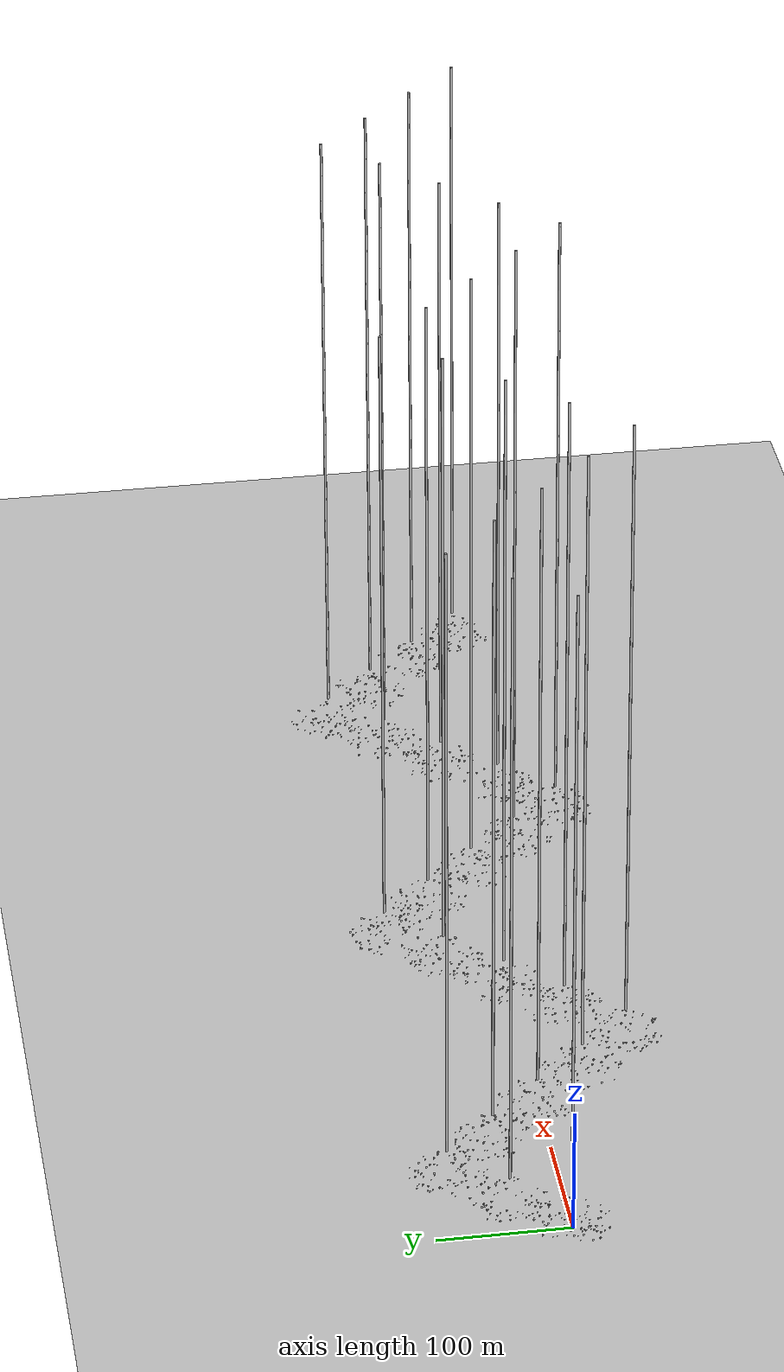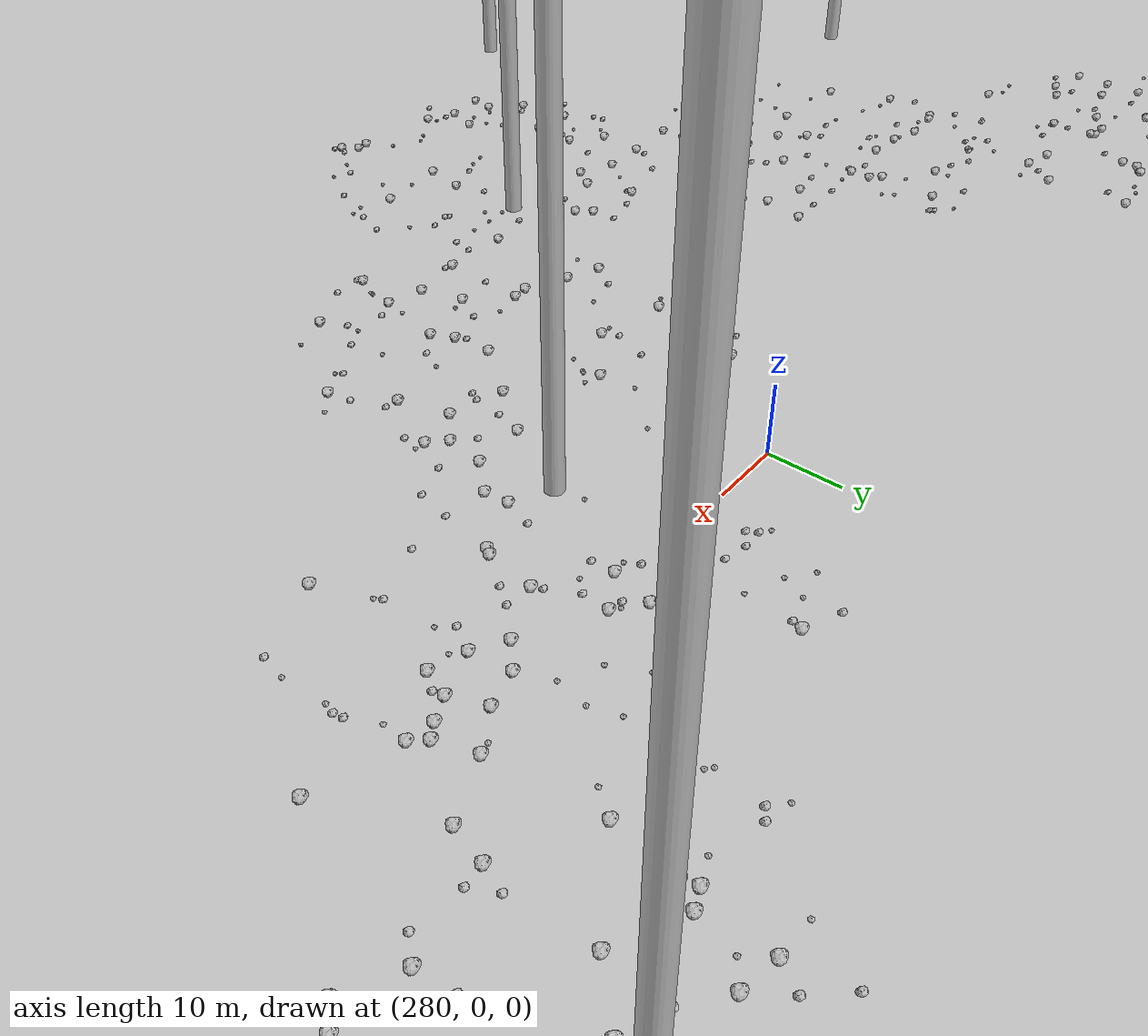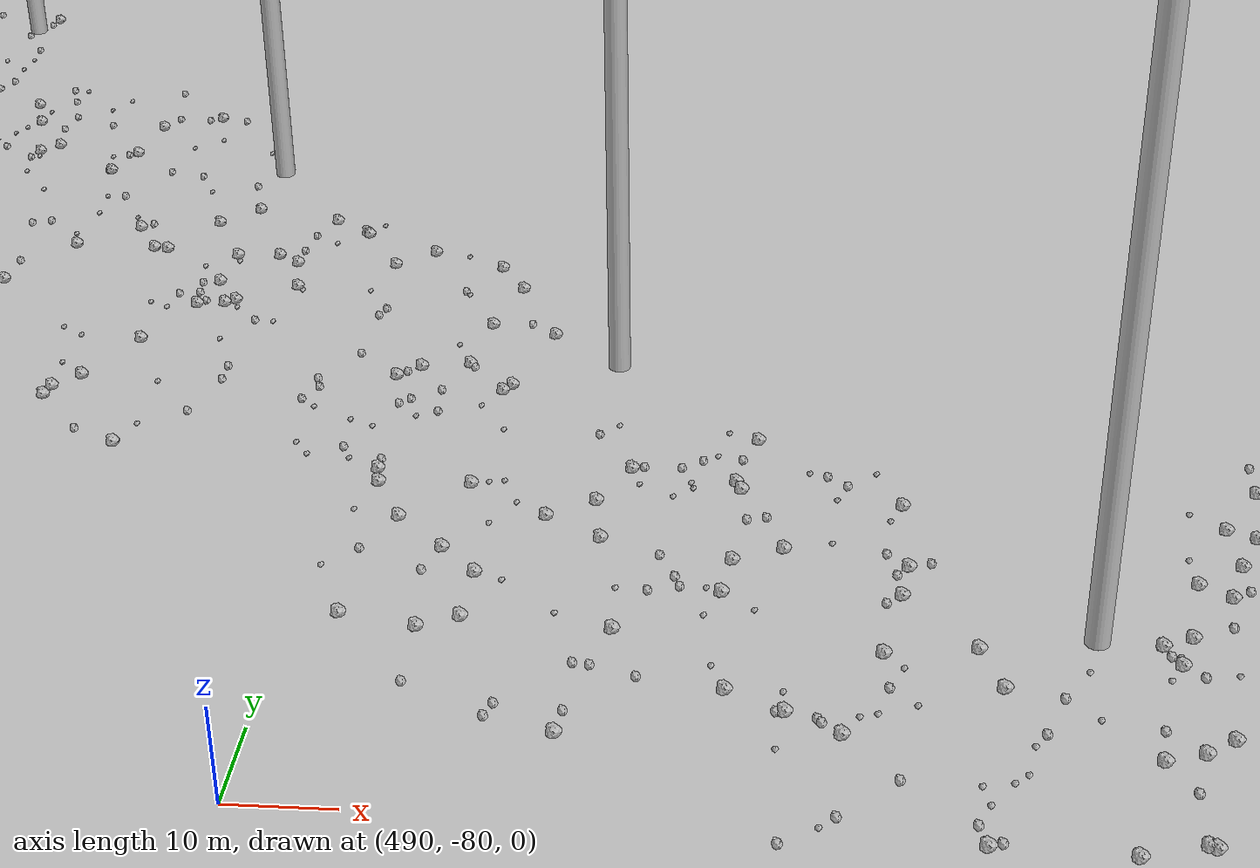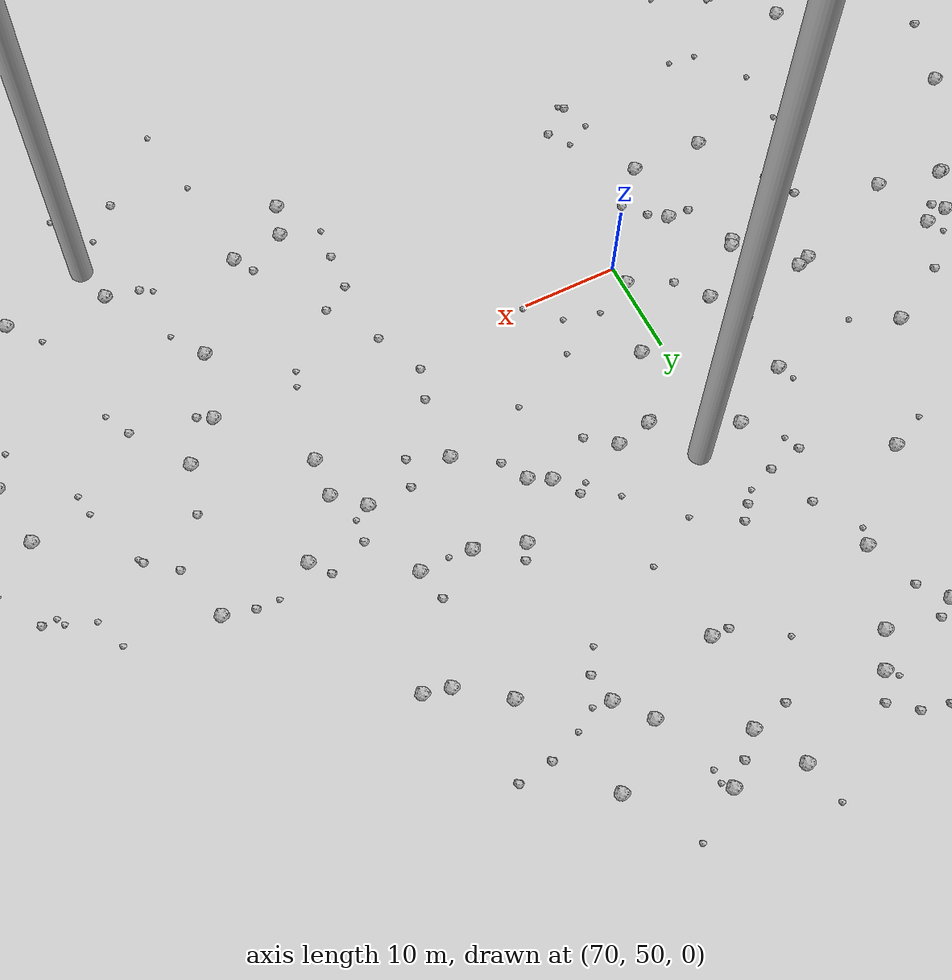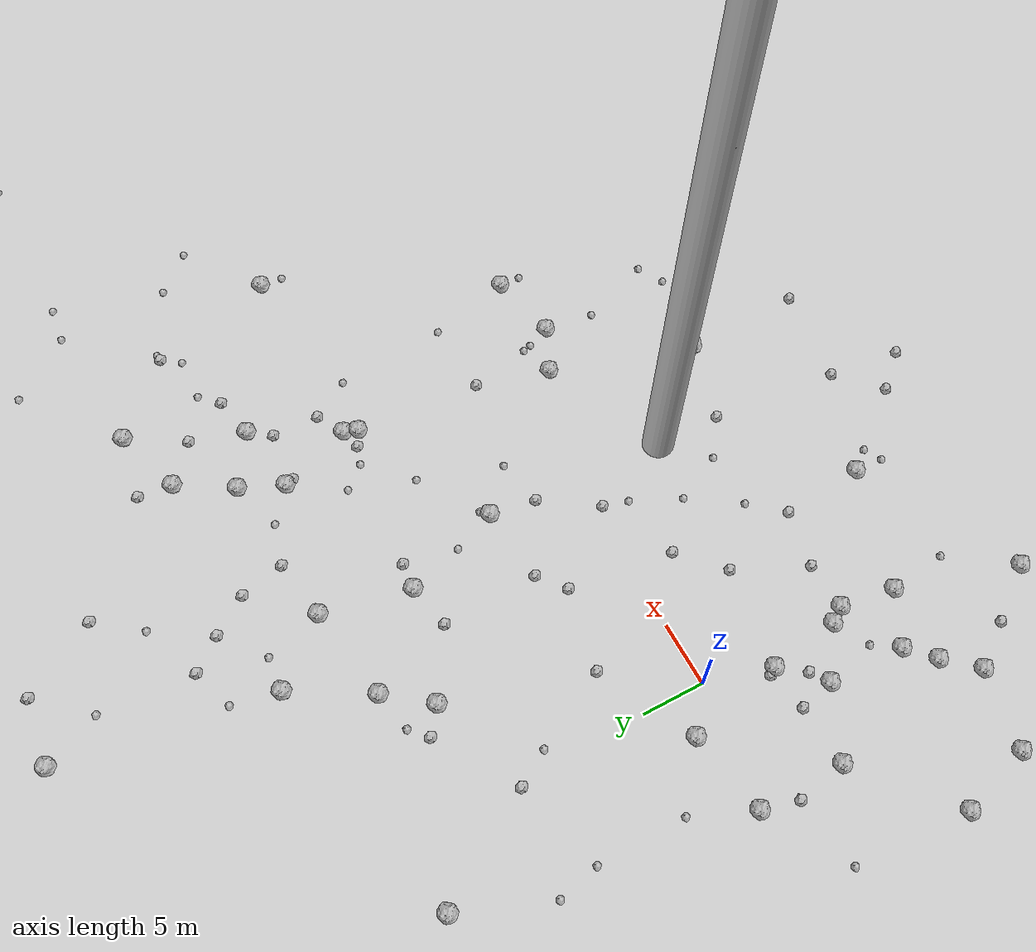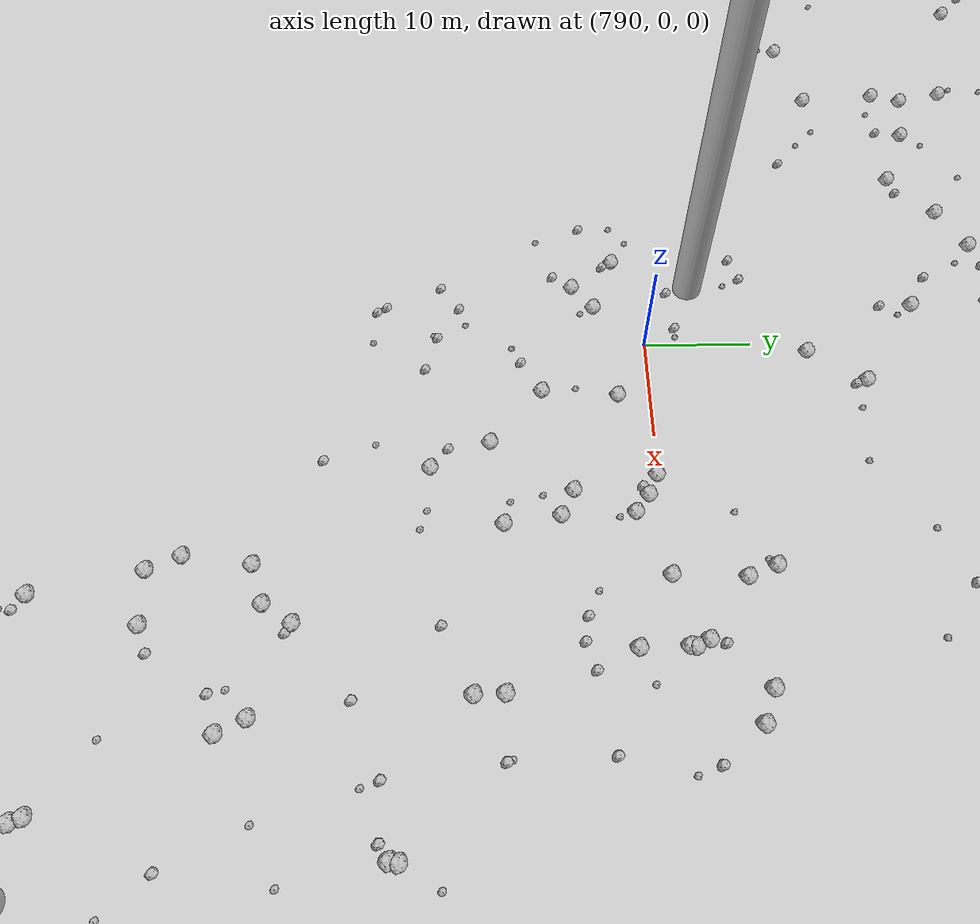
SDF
<sdf version="1.6">
 <world name="default">
  <include><uri>model://custom_ground</uri></include>
  <include><uri>model://sun</uri></include>
  <spherical_coordinates>
   <surface_model>EARTH_WGS84</surface_model>
   <latitude_deg>38.161479</latitude_deg>
   <longitude_deg>-122.454630</longitude_deg>
   <elevation>488.0</elevation>
   <heading_deg>90</heading_deg>
  </spherical_coordinates>
  <model name="rock1_0_0">
   <include><uri>model://rock1</uri><pose>10.308093503110921 20.846645113924552 0.5 0 0 0</pose></include>
  </model>
  <model name="rock1_0_1">
   <include><uri>model://rock1</uri><pose>8.833805726094432 -19.33073141889802 0.5 0 0 0</pose></include>
  </model>
  <model name="rock1_0_2">
   <include><uri>model://rock1</uri><pose>7.675220763039437 17.51723559488029 0.5 0 0 0</pose></include>
  </model>
  <model name="rock1_0_3">
   <include><uri>model://rock1</uri><pose>-14.815169350126993 -16.806266810537945 0.5 0 0 0</pose></include>
  </model>
  <model name="rock1_0_4">
   <include><uri>model://rock1</uri><pose>-9.627526794967379 -5.276134784586464 0.5 0 0 0</pose></include>
  </model>
  <model name="rock1_0_5">
   <include><uri>model://rock1</uri><pose>0.14350048495730405 -11.881437862271778 0.5 0 0 0</pose></include>
  </model>
  <model name="rock1_0_6">
   <include><uri>model://rock1</uri><pose>-16.51005586390668 -11.096822655782145 0.5 0 0 0</pose></include>
  </model>
  <model name="rock1_0_7">
   <include><uri>model://rock1</uri><pose>17.850193441742313 21.996792658042708 0.5 0 0 0</pose></include>
  </model>
  <model name="rock1_0_8">
   <include><uri>model://rock1</uri><pose>31.350161642384208 -4.706448587294485 0.5 0 0 0</pose></include>
  </model>
  <model name="rock1_0_9">
   <include><uri>model://rock1</uri><pose>16.329474908900508 14.978773140821836 0.5 0 0 0</pose></include>
  </model>
  <model name="rock1_0_10">
   <include><uri>model://rock1</uri><pose>36.83162018284337 -3.521574330771241 0.5 0 0 0</pose></include>
  </model>
  <model name="rock1_0_11">
   <include><uri>model://rock1</uri><pose>-3.4743051252785584 -25.518928062521944 0.5 0 0 0</pose></include>
  </model>
  <model name="rock1_0_12">
   <include><uri>model://rock1</uri><pose>-4.624492077895466 -13.942661119941754 0.5 0 0 0</pose></include>
  </model>
  <model name="rock1_0_13">
   <include><uri>model://rock1</uri><pose>-9.591353607719553 1.5476800889334967 0.5 0 0 0</pose></include>
  </model>
  <model name="rock1_0_14">
   <include><uri>model://rock1</uri><pose>24.333814955989972 -14.313478101322602 0.5 0 0 0</pose></include>
  </model>
  <model name="rock1_0_15">
   <include><uri>model://rock1</uri><pose>-4.317302781004811 -7.92902811894939 0.5 0 0 0</pose></include>
  </model>
  <model name="rock1_0_16">
   <include><uri>model://rock1</uri><pose>18.958581479578548 7.140094198507832 0.5 0 0 0</pose></include>
  </model>
  <model name="rock1_0_17">
   <include><uri>model://rock1</uri><pose>-8.718593291940799 -18.15909330203728 0.5 0 0 0</pose></include>
  </model>
  <model name="rock1_0_18">
   <include><uri>model://rock1</uri><pose>27.829667220051853 -3.022567563481587 0.5 0 0 0</pose></include>
  </model>
  <model name="rock1_0_19">
   <include><uri>model://rock1</uri><pose>-6.571041898843209 -15.758539917897746 0.5 0 0 0</pose></include>
  </model>
  <model name="rock1_0_20">
   <include><uri>model://rock1</uri><pose>-0.6818419119051597 -10.650925066535454 0.5 0 0 0</pose></include>
  </model>
  <model name="rock1_0_21">
   <include><uri>model://rock1</uri><pose>-5.489286542534973 23.559704599065363 0.5 0 0 0</pose></include>
  </model>
  <model name="rock1_0_22">
   <include><uri>model://rock1</uri><pose>-1.4662017126245992 -5.041043228103966 0.5 0 0 0</pose></include>
  </model>
  <model name="rock1_0_23">
   <include><uri>model://rock1</uri><pose>30.205027753007755 12.71567330010236 0.5 0 0 0</pose></include>
  </model>
  <model name="rock1_0_24">
   <include><uri>model://rock1</uri><pose>-3.1466381334157134 2.6419007982833307 0.5 0 0 0</pose></include>
  </model>
  <model name="rock1_0_25">
   <include><uri>model://rock1</uri><pose>30.624927037974302 13.80586450997398 0.5 0 0 0</pose></include>
  </model>
  <model name="rock1_0_26">
   <include><uri>model://rock1</uri><pose>-0.5845815208233027 -16.12360997560674 0.5 0 0 0</pose></include>
  </model>
  <model name="rock2_0_0">
   <include><uri>model://rock2</uri><pose>29.389943417925736 2.700648240450519 0.3 0 0 0</pose></include>
  </model>
  <model name="rock2_0_1">
   <include><uri>model://rock2</uri><pose>-2.97833081523169 -7.046550292103543 0.3 0 0 0</pose></include>
  </model>
  <model name="rock2_0_2">
   <include><uri>model://rock2</uri><pose>16.819238796077187 -22.585209690104943 0.3 0 0 0</pose></include>
  </model>
  <model name="rock2_0_3">
   <include><uri>model://rock2</uri><pose>-4.970915378720646 -5.177961687225157 0.3 0 0 0</pose></include>
  </model>
  <model name="rock2_0_4">
   <include><uri>model://rock2</uri><pose>18.42582986394212 14.766715410593314 0.3 0 0 0</pose></include>
  </model>
  <model name="rock2_0_5">
   <include><uri>model://rock2</uri><pose>9.697750903959133 -3.353988137764418 0.3 0 0 0</pose></include>
  </model>
  <model name="rock2_0_6">
   <include><uri>model://rock2</uri><pose>32.78182317745237 14.987776705843743 0.3 0 0 0</pose></include>
  </model>
  <model name="rock2_0_7">
   <include><uri>model://rock2</uri><pose>-0.43322149133977916 15.128798400059821 0.3 0 0 0</pose></include>
  </model>
  <model name="rock2_0_8">
   <include><uri>model://rock2</uri><pose>3.843271927718213 -11.854586118405724 0.3 0 0 0</pose></include>
  </model>
  <model name="rock2_0_9">
   <include><uri>model://rock2</uri><pose>13.670348708983113 -25.620359187521668 0.3 0 0 0</pose></include>
  </model>
  <model name="rock2_0_10">
   <include><uri>model://rock2</uri><pose>10.847322338386014 4.922099397847525 0.3 0 0 0</pose></include>
  </model>
  <model name="rock2_0_11">
   <include><uri>model://rock2</uri><pose>24.42032482344316 -23.670386814437343 0.3 0 0 0</pose></include>
  </model>
  <model name="rock2_0_12">
   <include><uri>model://rock2</uri><pose>15.472171147328659 -0.7111234026345805 0.3 0 0 0</pose></include>
  </model>
  <model name="rock2_0_13">
   <include><uri>model://rock2</uri><pose>32.91282382840692 18.7010484453997 0.3 0 0 0</pose></include>
  </model>
  <model name="rock2_0_14">
   <include><uri>model://rock2</uri><pose>-10.373534531003054 -1.3363828593185083 0.3 0 0 0</pose></include>
  </model>
  <model name="rock2_0_15">
   <include><uri>model://rock2</uri><pose>6.4534146444092855 -6.354133164803319 0.3 0 0 0</pose></include>
  </model>
  <model name="rock2_0_16">
   <include><uri>model://rock2</uri><pose>-1.8226353302189437 -4.502365354580785 0.3 0 0 0</pose></include>
  </model>
  <model name="rock2_0_17">
   <include><uri>model://rock2</uri><pose>12.935958921433517 6.581223633302841 0.3 0 0 0</pose></include>
  </model>
  <model name="rock2_0_18">
   <include><uri>model://rock2</uri><pose>28.934157979667056 13.380205187970667 0.3 0 0 0</pose></include>
  </model>
  <model name="rock2_0_19">
   <include><uri>model://rock2</uri><pose>5.714239045088043 19.025694543695096 0.3 0 0 0</pose></include>
  </model>
  <model name="rock2_0_20">
   <include><uri>model://rock2</uri><pose>4.327901831653161 6.320159947448069 0.3 0 0 0</pose></include>
  </model>
  <model name="rock2_0_21">
   <include><uri>model://rock2</uri><pose>16.07166598981322 -28.31161523471802 0.3 0 0 0</pose></include>
  </model>
  <model name="rock2_0_22">
   <include><uri>model://rock2</uri><pose>18.335020176544752 3.5103154856580545 0.3 0 0 0</pose></include>
  </model>
  <model name="rock2_0_23">
   <include><uri>model://rock2</uri><pose>-6.409661157281034 -21.536492449215572 0.3 0 0 0</pose></include>
  </model>
  <model name="rock2_0_24">
   <include><uri>model://rock2</uri><pose>17.914482950781114 -12.493829508151691 0.3 0 0 0</pose></include>
  </model>
  <model name="rock2_0_25">
   <include><uri>model://rock2</uri><pose>8.314373298620726 -12.843186448354459 0.3 0 0 0</pose></include>
  </model>
  <model name="rock2_0_26">
   <include><uri>model://rock2</uri><pose>12.734925102303635 14.242977952127966 0.3 0 0 0</pose></include>
  </model>
  <model name="rock3_0_0">
   <include><uri>model://rock3</uri><pose>30.4076273804924 -2.2323843435476824 0.2 0 0 0</pose></include>
  </model>
  <model name="rock3_0_1">
   <include><uri>model://rock3</uri><pose>-0.09730075121256121 -20.852241411978955 0.2 0 0 0</pose></include>
  </model>
  <model name="rock3_0_2">
   <include><uri>model://rock3</uri><pose>-8.311590570176723 16.49805685211374 0.2 0 0 0</pose></include>
  </model>
  <model name="rock3_0_3">
   <include><uri>model://rock3</uri><pose>36.764077011187894 -5.2839021176838905 0.2 0 0 0</pose></include>
  </model>
  <model name="rock3_0_4">
   <include><uri>model://rock3</uri><pose>-15.910173923021189 -2.07913007172489 0.2 0 0 0</pose></include>
  </model>
  <model name="rock3_0_5">
   <include><uri>model://rock3</uri><pose>16.50845883983672 26.53916027110491 0.2 0 0 0</pose></include>
  </model>
  <model name="rock3_0_6">
   <include><uri>model://rock3</uri><pose>34.65254353378364 11.848444795205417 0.2 0 0 0</pose></include>
  </model>
  <model name="rock3_0_7">
   <include><uri>model://rock3</uri><pose>13.111949235450687 -6.514958593905391 0.2 0 0 0</pose></include>
  </model>
  <model name="rock3_0_8">
   <include><uri>model://rock3</uri><pose>14.985381995954064 -10.389292431553294 0.2 0 0 0</pose></include>
  </model>
  <model name="rock3_0_9">
   <include><uri>model://rock3</uri><pose>-7.567825594403805 13.211613144623215 0.2 0 0 0</pose></include>
  </model>
  <model name="rock3_0_10">
   <include><uri>model://rock3</uri><pose>8.68141185604959 -21.727915502424644 0.2 0 0 0</pose></include>
  </model>
  <model name="rock3_0_11">
   <include><uri>model://rock3</uri><pose>30.811709933671523 -15.512065518911447 0.2 0 0 0</pose></include>
  </model>
  <model name="rock3_0_12">
   <include><uri>model://rock3</uri><pose>19.477015347759966 7.654397307839389 0.2 0 0 0</pose></include>
  </model>
  <model name="rock3_0_13">
   <include><uri>model://rock3</uri><pose>-3.3497108199021426 -12.137848857498454 0.2 0 0 0</pose></include>
  </model>
  <model name="rock3_0_14">
   <include><uri>model://rock3</uri><pose>30.594040624294266 -2.9235485761655724 0.2 0 0 0</pose></include>
  </model>
  <model name="rock3_0_15">
   <include><uri>model://rock3</uri><pose>17.55665693536406 10.550255572514516 0.2 0 0 0</pose></include>
  </model>
  <model name="rock3_0_16">
   <include><uri>model://rock3</uri><pose>30.775291353603137 -8.710189506213666 0.2 0 0 0</pose></include>
  </model>
  <model name="rock3_0_17">
   <include><uri>model://rock3</uri><pose>10.018497661447348 -21.01649282693747 0.2 0 0 0</pose></include>
  </model>
  <model name="rock3_0_18">
   <include><uri>model://rock3</uri><pose>32.84043480902511 -14.406536456329317 0.2 0 0 0</pose></include>
  </model>
  <model name="rock3_0_19">
   <include><uri>model://rock3</uri><pose>24.19135059098371 10.641511203039244 0.2 0 0 0</pose></include>
  </model>
  <model name="rock3_0_20">
   <include><uri>model://rock3</uri><pose>-7.605401878819469 6.195669007631572 0.2 0 0 0</pose></include>
  </model>
  <model name="rock3_0_21">
   <include><uri>model://rock3</uri><pose>7.0003639825501125 20.20052294257637 0.2 0 0 0</pose></include>
  </model>
  <model name="rock3_0_22">
   <include><uri>model://rock3</uri><pose>35.25450666233921 3.0210959234106767 0.2 0 0 0</pose></include>
  </model>
  <model name="rock3_0_23">
   <include><uri>model://rock3</uri><pose>14.90254275995602 -2.7271017800193604 0.2 0 0 0</pose></include>
  </model>
  <model name="rock3_0_24">
   <include><uri>model://rock3</uri><pose>1.15744816897109 12.422620141891663 0.2 0 0 0</pose></include>
  </model>
  <model name="rock3_0_25">
   <include><uri>model://rock3</uri><pose>22.073478621132026 4.171224923424084 0.2 0 0 0</pose></include>
  </model>
  <model name="rock3_0_26">
   <include><uri>model://rock3</uri><pose>10.499208725665568 -10.390239007725793 0.2 0 0 0</pose></include>
  </model>
  <model name="rock1_1_0">
   <include><uri>model://rock1</uri><pose>61.98717375226187 47.16373612466019 0.5 0 0 0</pose></include>
  </model>
  <model name="rock1_1_1">
   <include><uri>model://rock1</uri><pose>30.633897444608614 57.803698181435756 0.5 0 0 0</pose></include>
  </model>
  <model name="rock1_1_2">
   <include><uri>model://rock1</uri><pose>33.58694662265966 54.82183648227805 0.5 0 0 0</pose></include>
  </model>
  <model name="rock1_1_3">
   <include><uri>model://rock1</uri><pose>32.67515685425006 27.280575274209998 0.5 0 0 0</pose></include>
  </model>
  <model name="rock1_1_4">
   <include><uri>model://rock1</uri><pose>28.548853172166517 19.652927750352045 0.5 0 0 0</pose></include>
  </model>
  <model name="rock1_1_5">
   <include><uri>model://rock1</uri><pose>13.787912067817075 26.802790138850995 0.5 0 0 0</pose></include>
  </model>
  <model name="rock1_1_6">
   <include><uri>model://rock1</uri><pose>54.592580242239656 40.414275851924046 0.5 0 0 0</pose></include>
  </model>
  <model name="rock1_1_7">
   <include><uri>model://rock1</uri><pose>38.22451499624336 29.085137145706987 0.5 0 0 0</pose></include>
  </model>
  <model name="rock1_1_8">
   <include><uri>model://rock1</uri><pose>62.17600042493387 40.367671449802906 0.5 0 0 0</pose></include>
  </model>
  <model name="rock1_1_9">
   <include><uri>model://rock1</uri><pose>34.85775711349633 61.585655975436666 0.5 0 0 0</pose></include>
  </model>
  <model name="rock1_1_10">
   <include><uri>model://rock1</uri><pose>16.052126770070302 51.030262162690065 0.5 0 0 0</pose></include>
  </model>
  <model name="rock1_1_11">
   <include><uri>model://rock1</uri><pose>27.593119956209947 44.379989147846 0.5 0 0 0</pose></include>
  </model>
  <model name="rock1_1_12">
   <include><uri>model://rock1</uri><pose>35.80916352914313 58.98065677319521 0.5 0 0 0</pose></include>
  </model>
  <model name="rock1_1_13">
   <include><uri>model://rock1</uri><pose>63.00414977187014 57.44810008631391 0.5 0 0 0</pose></include>
  </model>
  <model name="rock1_1_14">
   <include><uri>model://rock1</uri><pose>38.38263614360024 59.52029366892748 0.5 0 0 0</pose></include>
  </model>
  <model name="rock1_1_15">
   <include><uri>model://rock1</uri><pose>40.431438564489945 53.34758766616328 0.5 0 0 0</pose></include>
  </model>
  <model name="rock1_1_16">
   <include><uri>model://rock1</uri><pose>57.57689030641884 52.524450308835014 0.5 0 0 0</pose></include>
  </model>
  <model name="rock1_1_17">
   <include><uri>model://rock1</uri><pose>30.07248212825656 23.030930359675736 0.5 0 0 0</pose></include>
  </model>
  <model name="rock1_1_18">
   <include><uri>model://rock1</uri><pose>46.16966381248035 13.775307163182966 0.5 0 0 0</pose></include>
  </model>
  <model name="rock1_1_19">
   <include><uri>model://rock1</uri><pose>51.68857932516113 57.76090599101797 0.5 0 0 0</pose></include>
  </model>
  <model name="rock1_1_20">
   <include><uri>model://rock1</uri><pose>53.02425849550794 58.1885291610372 0.5 0 0 0</pose></include>
  </model>
  <model name="rock1_1_21">
   <include><uri>model://rock1</uri><pose>23.117848244862312 51.958520391864376 0.5 0 0 0</pose></include>
  </model>
  <model name="rock1_1_22">
   <include><uri>model://rock1</uri><pose>57.94859007805599 53.08468540594972 0.5 0 0 0</pose></include>
  </model>
  <model name="rock1_1_23">
   <include><uri>model://rock1</uri><pose>33.858023326245416 54.84781925213926 0.5 0 0 0</pose></include>
  </model>
  <model name="rock1_1_24">
   <include><uri>model://rock1</uri><pose>47.16063451297885 68.13335847125364 0.5 0 0 0</pose></include>
  </model>
  <model name="rock1_1_25">
   <include><uri>model://rock1</uri><pose>16.5750592768196 43.507206936499834 0.5 0 0 0</pose></include>
  </model>
  <model name="rock1_1_26">
   <include><uri>model://rock1</uri><pose>34.185512996175945 20.414429854656788 0.5 0 0 0</pose></include>
  </model>
  <model name="rock2_1_0">
   <include><uri>model://rock2</uri><pose>68.11619578628427 32.29539153240441 0.3 0 0 0</pose></include>
  </model>
  <model name="rock2_1_1">
   <include><uri>model://rock2</uri><pose>25.23556907558092 36.94452334497285 0.3 0 0 0</pose></include>
  </model>
  <model name="rock2_1_2">
   <include><uri>model://rock2</uri><pose>26.751557296783567 56.59923923711911 0.3 0 0 0</pose></include>
  </model>
  <model name="rock2_1_3">
   <include><uri>model://rock2</uri><pose>31.556328247222545 58.40809658595625 0.3 0 0 0</pose></include>
  </model>
  <model name="rock2_1_4">
   <include><uri>model://rock2</uri><pose>21.873526538389374 42.90641056511652 0.3 0 0 0</pose></include>
  </model>
  <model name="rock2_1_5">
   <include><uri>model://rock2</uri><pose>25.5994675689959 49.30737016826226 0.3 0 0 0</pose></include>
  </model>
  <model name="rock2_1_6">
   <include><uri>model://rock2</uri><pose>63.67376900557831 45.882380942117344 0.3 0 0 0</pose></include>
  </model>
  <model name="rock2_1_7">
   <include><uri>model://rock2</uri><pose>48.65929679901415 50.29163935497569 0.3 0 0 0</pose></include>
  </model>
  <model name="rock2_1_8">
   <include><uri>model://rock2</uri><pose>28.7377030199424 18.993207224759303 0.3 0 0 0</pose></include>
  </model>
  <model name="rock2_1_9">
   <include><uri>model://rock2</uri><pose>32.97786029965124 30.008332941385675 0.3 0 0 0</pose></include>
  </model>
  <model name="rock2_1_10">
   <include><uri>model://rock2</uri><pose>65.04279935743706 30.033982560166415 0.3 0 0 0</pose></include>
  </model>
  <model name="rock2_1_11">
   <include><uri>model://rock2</uri><pose>20.08783080977048 60.04576164334327 0.3 0 0 0</pose></include>
  </model>
  <model name="rock2_1_12">
   <include><uri>model://rock2</uri><pose>21.81265552277923 26.28781764993238 0.3 0 0 0</pose></include>
  </model>
  <model name="rock2_1_13">
   <include><uri>model://rock2</uri><pose>35.542767681183875 24.71732507136832 0.3 0 0 0</pose></include>
  </model>
  <model name="rock2_1_14">
   <include><uri>model://rock2</uri><pose>43.43931971090729 23.783084799621186 0.3 0 0 0</pose></include>
  </model>
  <model name="rock2_1_15">
   <include><uri>model://rock2</uri><pose>60.67009328010746 61.169004130024895 0.3 0 0 0</pose></include>
  </model>
  <model name="rock2_1_16">
   <include><uri>model://rock2</uri><pose>36.6671148943132 57.85748849042427 0.3 0 0 0</pose></include>
  </model>
  <model name="rock2_1_17">
   <include><uri>model://rock2</uri><pose>59.63149985203442 47.243966011258976 0.3 0 0 0</pose></include>
  </model>
  <model name="rock2_1_18">
   <include><uri>model://rock2</uri><pose>20.56064103316597 59.613466224002266 0.3 0 0 0</pose></include>
  </model>
  <model name="rock2_1_19">
   <include><uri>model://rock2</uri><pose>65.57535588606973 43.798871976731185 0.3 0 0 0</pose></include>
  </model>
  <model name="rock2_1_20">
   <include><uri>model://rock2</uri><pose>38.41775277723619 66.6904343061472 0.3 0 0 0</pose></include>
  </model>
  <model name="rock2_1_21">
   <include><uri>model://rock2</uri><pose>22.61969098844817 22.746430184871222 0.3 0 0 0</pose></include>
  </model>
  <model name="rock2_1_22">
   <include><uri>model://rock2</uri><pose>40.67492090927712 64.57005694861463 0.3 0 0 0</pose></include>
  </model>
  <model name="rock2_1_23">
   <include><uri>model://rock2</uri><pose>50.41293889629208 47.25481311929103 0.3 0 0 0</pose></include>
  </model>
  <model name="rock2_1_24">
   <include><uri>model://rock2</uri><pose>37.50577411358714 21.112607603266596 0.3 0 0 0</pose></include>
  </model>
  <model name="rock2_1_25">
   <include><uri>model://rock2</uri><pose>19.822035517135276 29.197138679969445 0.3 0 0 0</pose></include>
  </model>
  <model name="rock2_1_26">
   <include><uri>model://rock2</uri><pose>17.89720854464355 31.632978053404976 0.3 0 0 0</pose></include>
  </model>
  <model name="rock3_1_0">
   <include><uri>model://rock3</uri><pose>46.02369858732601 11.941620722270263 0.2 0 0 0</pose></include>
  </model>
  <model name="rock3_1_1">
   <include><uri>model://rock3</uri><pose>65.49333833824193 29.502249660083997 0.2 0 0 0</pose></include>
  </model>
  <model name="rock3_1_2">
   <include><uri>model://rock3</uri><pose>64.00503850744035 33.007141386926286 0.2 0 0 0</pose></include>
  </model>
  <model name="rock3_1_3">
   <include><uri>model://rock3</uri><pose>22.574274724819933 33.54429285137602 0.2 0 0 0</pose></include>
  </model>
  <model name="rock3_1_4">
   <include><uri>model://rock3</uri><pose>38.915181476128154 22.47623221134664 0.2 0 0 0</pose></include>
  </model>
  <model name="rock3_1_5">
   <include><uri>model://rock3</uri><pose>49.37975057033028 21.06299137580732 0.2 0 0 0</pose></include>
  </model>
  <model name="rock3_1_6">
   <include><uri>model://rock3</uri><pose>51.70850411935552 65.82010150529386 0.2 0 0 0</pose></include>
  </model>
  <model name="rock3_1_7">
   <include><uri>model://rock3</uri><pose>18.41454506032086 39.079135922259965 0.2 0 0 0</pose></include>
  </model>
  <model name="rock3_1_8">
   <include><uri>model://rock3</uri><pose>52.02666981343713 18.131361435063134 0.2 0 0 0</pose></include>
  </model>
  <model name="rock3_1_9">
   <include><uri>model://rock3</uri><pose>49.04601875517859 30.03668397498394 0.2 0 0 0</pose></include>
  </model>
  <model name="rock3_1_10">
   <include><uri>model://rock3</uri><pose>18.931664690421748 59.05734960019084 0.2 0 0 0</pose></include>
  </model>
  <model name="rock3_1_11">
   <include><uri>model://rock3</uri><pose>25.891308679237603 15.633061379998317 0.2 0 0 0</pose></include>
  </model>
  <model name="rock3_1_12">
   <include><uri>model://rock3</uri><pose>37.29835892450015 61.05245943427872 0.2 0 0 0</pose></include>
  </model>
  <model name="rock3_1_13">
   <include><uri>model://rock3</uri><pose>18.528741383692832 53.50568118736214 0.2 0 0 0</pose></include>
  </model>
  <model name="rock3_1_14">
   <include><uri>model://rock3</uri><pose>45.53886031291759 40.84269429134234 0.2 0 0 0</pose></include>
  </model>
  <model name="rock3_1_15">
   <include><uri>model://rock3</uri><pose>31.11038703755861 57.619958258292286 0.2 0 0 0</pose></include>
  </model>
  <model name="rock3_1_16">
   <include><uri>model://rock3</uri><pose>25.92350223466099 21.739270660151995 0.2 0 0 0</pose></include>
  </model>
  <model name="rock3_1_17">
   <include><uri>model://rock3</uri><pose>14.540105577954293 30.51426249617375 0.2 0 0 0</pose></include>
  </model>
  <model name="rock3_1_18">
   <include><uri>model://rock3</uri><pose>66.64073871244747 34.40401514012497 0.2 0 0 0</pose></include>
  </model>
  <model name="rock3_1_19">
   <include><uri>model://rock3</uri><pose>25.24733947329173 57.01198921946335 0.2 0 0 0</pose></include>
  </model>
  <model name="rock3_1_20">
   <include><uri>model://rock3</uri><pose>45.40515078968956 34.98156919934917 0.2 0 0 0</pose></include>
  </model>
  <model name="rock3_1_21">
   <include><uri>model://rock3</uri><pose>34.49705222046478 60.85463777692132 0.2 0 0 0</pose></include>
  </model>
  <model name="rock3_1_22">
   <include><uri>model://rock3</uri><pose>57.66070289483169 53.10514091568992 0.2 0 0 0</pose></include>
  </model>
  <model name="rock3_1_23">
   <include><uri>model://rock3</uri><pose>27.441891296097324 13.83168306528701 0.2 0 0 0</pose></include>
  </model>
  <model name="rock3_1_24">
   <include><uri>model://rock3</uri><pose>43.959257246347505 23.84386527125868 0.2 0 0 0</pose></include>
  </model>
  <model name="rock3_1_25">
   <include><uri>model://rock3</uri><pose>42.424502023733965 22.341813923997194 0.2 0 0 0</pose></include>
  </model>
  <model name="rock3_1_26">
   <include><uri>model://rock3</uri><pose>51.94082848781475 29.681556632956713 0.2 0 0 0</pose></include>
  </model>
  <model name="rock1_2_0">
   <include><uri>model://rock1</uri><pose>66.53922450001838 95.75907108683231 0.5 0 0 0</pose></include>
  </model>
  <model name="rock1_2_1">
   <include><uri>model://rock1</uri><pose>59.36987647059958 95.79087319849629 0.5 0 0 0</pose></include>
  </model>
  <model name="rock1_2_2">
   <include><uri>model://rock1</uri><pose>82.27490782775278 98.61809892769568 0.5 0 0 0</pose></include>
  </model>
  <model name="rock1_2_3">
   <include><uri>model://rock1</uri><pose>75.56550554563553 67.25336029755233 0.5 0 0 0</pose></include>
  </model>
  <model name="rock1_2_4">
   <include><uri>model://rock1</uri><pose>61.045785993428254 67.53492289987014 0.5 0 0 0</pose></include>
  </model>
  <model name="rock1_2_5">
   <include><uri>model://rock1</uri><pose>107.41842446600414 82.44852041751302 0.5 0 0 0</pose></include>
  </model>
  <model name="rock1_2_6">
   <include><uri>model://rock1</uri><pose>88.88727728953333 67.38252602651829 0.5 0 0 0</pose></include>
  </model>
  <model name="rock1_2_7">
   <include><uri>model://rock1</uri><pose>86.60518816492578 102.52085295184571 0.5 0 0 0</pose></include>
  </model>
  <model name="rock1_2_8">
   <include><uri>model://rock1</uri><pose>79.23680962684821 68.03739158679628 0.5 0 0 0</pose></include>
  </model>
  <model name="rock1_2_9">
   <include><uri>model://rock1</uri><pose>92.01886006679607 73.37397043088863 0.5 0 0 0</pose></include>
  </model>
  <model name="rock1_2_10">
   <include><uri>model://rock1</uri><pose>100.15352927368919 86.60671263787731 0.5 0 0 0</pose></include>
  </model>
  <model name="rock1_2_11">
   <include><uri>model://rock1</uri><pose>63.45763598975623 87.80761771634423 0.5 0 0 0</pose></include>
  </model>
  <model name="rock1_2_12">
   <include><uri>model://rock1</uri><pose>68.72268694838046 99.13391949376823 0.5 0 0 0</pose></include>
  </model>
  <model name="rock1_2_13">
   <include><uri>model://rock1</uri><pose>92.38752218617782 90.63438842116474 0.5 0 0 0</pose></include>
  </model>
  <model name="rock1_2_14">
   <include><uri>model://rock1</uri><pose>67.50805519003876 71.20183370413287 0.5 0 0 0</pose></include>
  </model>
  <model name="rock1_2_15">
   <include><uri>model://rock1</uri><pose>79.64830143776294 103.4777793988624 0.5 0 0 0</pose></include>
  </model>
  <model name="rock1_2_16">
   <include><uri>model://rock1</uri><pose>104.76962753214434 83.10426138196785 0.5 0 0 0</pose></include>
  </model>
  <model name="rock1_2_17">
   <include><uri>model://rock1</uri><pose>86.77901199489966 68.52886463397904 0.5 0 0 0</pose></include>
  </model>
  <model name="rock1_2_18">
   <include><uri>model://rock1</uri><pose>69.7418014190883 52.255296518031614 0.5 0 0 0</pose></include>
  </model>
  <model name="rock1_2_19">
   <include><uri>model://rock1</uri><pose>96.94267976249517 71.69430441017828 0.5 0 0 0</pose></include>
  </model>
  <model name="rock1_2_20">
   <include><uri>model://rock1</uri><pose>95.73592884684342 98.59105324375132 0.5 0 0 0</pose></include>
  </model>
  <model name="rock1_2_21">
   <include><uri>model://rock1</uri><pose>81.18838337822967 89.24207486703412 0.5 0 0 0</pose></include>
  </model>
  <model name="rock1_2_22">
   <include><uri>model://rock1</uri><pose>89.74325047752872 93.86983093425386 0.5 0 0 0</pose></include>
  </model>
  <model name="rock1_2_23">
   <include><uri>model://rock1</uri><pose>94.48894015392358 62.04651490925766 0.5 0 0 0</pose></include>
  </model>
  <model name="rock1_2_24">
   <include><uri>model://rock1</uri><pose>72.31556253770009 60.03547728579018 0.5 0 0 0</pose></include>
  </model>
  <model name="rock1_2_25">
   <include><uri>model://rock1</uri><pose>102.32652728228831 71.55186627256947 0.5 0 0 0</pose></include>
  </model>
  <model name="rock1_2_26">
   <include><uri>model://rock1</uri><pose>55.275795210580235 80.01769849093641 0.5 0 0 0</pose></include>
  </model>
  <model name="rock2_2_0">
   <include><uri>model://rock2</uri><pose>81.96210732984568 65.84433667187535 0.3 0 0 0</pose></include>
  </model>
  <model name="rock2_2_1">
   <include><uri>model://rock2</uri><pose>67.79515300899288 103.78487850460999 0.3 0 0 0</pose></include>
  </model>
  <model name="rock2_2_2">
   <include><uri>model://rock2</uri><pose>84.38280500697826 100.74211112553002 0.3 0 0 0</pose></include>
  </model>
  <model name="rock2_2_3">
   <include><uri>model://rock2</uri><pose>92.85301976577242 87.60022414816194 0.3 0 0 0</pose></include>
  </model>
  <model name="rock2_2_4">
   <include><uri>model://rock2</uri><pose>64.90941053540976 104.47261298249865 0.3 0 0 0</pose></include>
  </model>
  <model name="rock2_2_5">
   <include><uri>model://rock2</uri><pose>92.93557283152833 74.8929477309503 0.3 0 0 0</pose></include>
  </model>
  <model name="rock2_2_6">
   <include><uri>model://rock2</uri><pose>90.31367329951718 64.73965262561387 0.3 0 0 0</pose></include>
  </model>
  <model name="rock2_2_7">
   <include><uri>model://rock2</uri><pose>99.79400404023224 93.21571388246637 0.3 0 0 0</pose></include>
  </model>
  <model name="rock2_2_8">
   <include><uri>model://rock2</uri><pose>93.82811999869827 55.227537644345794 0.3 0 0 0</pose></include>
  </model>
  <model name="rock2_2_9">
   <include><uri>model://rock2</uri><pose>99.22607662988622 63.22729445750185 0.3 0 0 0</pose></include>
  </model>
  <model name="rock2_2_10">
   <include><uri>model://rock2</uri><pose>61.12201694478269 96.99647752326868 0.3 0 0 0</pose></include>
  </model>
  <model name="rock2_2_11">
   <include><uri>model://rock2</uri><pose>79.29544993962605 89.24091264150978 0.3 0 0 0</pose></include>
  </model>
  <model name="rock2_2_12">
   <include><uri>model://rock2</uri><pose>103.41953785317301 93.74666186424922 0.3 0 0 0</pose></include>
  </model>
  <model name="rock2_2_13">
   <include><uri>model://rock2</uri><pose>74.9889115143537 66.91083062542066 0.3 0 0 0</pose></include>
  </model>
  <model name="rock2_2_14">
   <include><uri>model://rock2</uri><pose>65.59208926539225 81.57391113315809 0.3 0 0 0</pose></include>
  </model>
  <model name="rock2_2_15">
   <include><uri>model://rock2</uri><pose>61.449641380403875 93.15730160795516 0.3 0 0 0</pose></include>
  </model>
  <model name="rock2_2_16">
   <include><uri>model://rock2</uri><pose>85.01048605688652 71.00417806642531 0.3 0 0 0</pose></include>
  </model>
  <model name="rock2_2_17">
   <include><uri>model://rock2</uri><pose>101.60214770637776 74.85880952163693 0.3 0 0 0</pose></include>
  </model>
  <model name="rock2_2_18">
   <include><uri>model://rock2</uri><pose>69.20595006037948 67.65657645157503 0.3 0 0 0</pose></include>
  </model>
  <model name="rock2_2_19">
   <include><uri>model://rock2</uri><pose>71.23977861381347 79.05536005331622 0.3 0 0 0</pose></include>
  </model>
  <model name="rock2_2_20">
   <include><uri>model://rock2</uri><pose>70.25743021386192 101.77913361823877 0.3 0 0 0</pose></include>
  </model>
  <model name="rock2_2_21">
   <include><uri>model://rock2</uri><pose>65.29913243602121 54.28057559230052 0.3 0 0 0</pose></include>
  </model>
  <model name="rock2_2_22">
   <include><uri>model://rock2</uri><pose>67.34406741239061 76.85100154162735 0.3 0 0 0</pose></include>
  </model>
  <model name="rock2_2_23">
   <include><uri>model://rock2</uri><pose>63.788631434427664 76.10643405775397 0.3 0 0 0</pose></include>
  </model>
  <model name="rock2_2_24">
   <include><uri>model://rock2</uri><pose>72.42822886176599 80.49336115680424 0.3 0 0 0</pose></include>
  </model>
  <model name="rock2_2_25">
   <include><uri>model://rock2</uri><pose>105.67995814530195 66.40886849466598 0.3 0 0 0</pose></include>
  </model>
  <model name="rock2_2_26">
   <include><uri>model://rock2</uri><pose>78.32936004724569 97.73451913863312 0.3 0 0 0</pose></include>
  </model>
  <model name="rock3_2_0">
   <include><uri>model://rock3</uri><pose>91.29707133948281 85.22040896242784 0.2 0 0 0</pose></include>
  </model>
  <model name="rock3_2_1">
   <include><uri>model://rock3</uri><pose>85.95767066120618 59.99261649278199 0.2 0 0 0</pose></include>
  </model>
  <model name="rock3_2_2">
   <include><uri>model://rock3</uri><pose>91.45740030454385 105.57682199828693 0.2 0 0 0</pose></include>
  </model>
  <model name="rock3_2_3">
   <include><uri>model://rock3</uri><pose>80.4265473096714 50.19260828704062 0.2 0 0 0</pose></include>
  </model>
  <model name="rock3_2_4">
   <include><uri>model://rock3</uri><pose>96.26507339393262 71.37028922098392 0.2 0 0 0</pose></include>
  </model>
  <model name="rock3_2_5">
   <include><uri>model://rock3</uri><pose>87.28141794470523 100.26403052724785 0.2 0 0 0</pose></include>
  </model>
  <model name="rock3_2_6">
   <include><uri>model://rock3</uri><pose>78.9168903782907 56.782856241131185 0.2 0 0 0</pose></include>
  </model>
  <model name="rock3_2_7">
   <include><uri>model://rock3</uri><pose>70.15454558281161 77.85557904567654 0.2 0 0 0</pose></include>
  </model>
  <model name="rock3_2_8">
   <include><uri>model://rock3</uri><pose>62.721717737449005 85.99936205625039 0.2 0 0 0</pose></include>
  </model>
  <model name="rock3_2_9">
   <include><uri>model://rock3</uri><pose>67.67625452833028 100.05507822624068 0.2 0 0 0</pose></include>
  </model>
  <model name="rock3_2_10">
   <include><uri>model://rock3</uri><pose>73.66042497608095 54.069326078313715 0.2 0 0 0</pose></include>
  </model>
  <model name="rock3_2_11">
   <include><uri>model://rock3</uri><pose>94.183990908657 90.35140341741382 0.2 0 0 0</pose></include>
  </model>
  <model name="rock3_2_12">
   <include><uri>model://rock3</uri><pose>81.59682356476182 72.9291750787946 0.2 0 0 0</pose></include>
  </model>
  <model name="rock3_2_13">
   <include><uri>model://rock3</uri><pose>78.59291239218015 107.83077963117367 0.2 0 0 0</pose></include>
  </model>
  <model name="rock3_2_14">
   <include><uri>model://rock3</uri><pose>82.44671080674489 80.7112475092063 0.2 0 0 0</pose></include>
  </model>
  <model name="rock3_2_15">
   <include><uri>model://rock3</uri><pose>69.54601528940407 52.38220287481126 0.2 0 0 0</pose></include>
  </model>
  <model name="rock3_2_16">
   <include><uri>model://rock3</uri><pose>77.39576704584276 53.11215714161034 0.2 0 0 0</pose></include>
  </model>
  <model name="rock3_2_17">
   <include><uri>model://rock3</uri><pose>60.20485329561275 69.12180569003361 0.2 0 0 0</pose></include>
  </model>
  <model name="rock3_2_18">
   <include><uri>model://rock3</uri><pose>96.38915086682312 91.80842250759493 0.2 0 0 0</pose></include>
  </model>
  <model name="rock3_2_19">
   <include><uri>model://rock3</uri><pose>99.22681261484368 71.3269526121999 0.2 0 0 0</pose></include>
  </model>
  <model name="rock3_2_20">
   <include><uri>model://rock3</uri><pose>74.48907977380205 92.42076270633521 0.2 0 0 0</pose></include>
  </model>
  <model name="rock3_2_21">
   <include><uri>model://rock3</uri><pose>51.45478881519475 78.27455415681078 0.2 0 0 0</pose></include>
  </model>
  <model name="rock3_2_22">
   <include><uri>model://rock3</uri><pose>86.1502608423763 68.33552194610272 0.2 0 0 0</pose></include>
  </model>
  <model name="rock3_2_23">
   <include><uri>model://rock3</uri><pose>87.27817277261175 101.61612356676316 0.2 0 0 0</pose></include>
  </model>
  <model name="rock3_2_24">
   <include><uri>model://rock3</uri><pose>64.37790713948348 74.46833201815119 0.2 0 0 0</pose></include>
  </model>
  <model name="rock3_2_25">
   <include><uri>model://rock3</uri><pose>76.92982264603148 77.74180859258556 0.2 0 0 0</pose></include>
  </model>
  <model name="rock3_2_26">
   <include><uri>model://rock3</uri><pose>83.98631977582332 70.13755004802695 0.2 0 0 0</pose></include>
  </model>
  <model name="rock1_3_0">
   <include><uri>model://rock1</uri><pose>141.20317514117755 43.56855084264186 0.5 0 0 0</pose></include>
  </model>
  <model name="rock1_3_1">
   <include><uri>model://rock1</uri><pose>133.80778435562348 52.591660884042035 0.5 0 0 0</pose></include>
  </model>
  <model name="rock1_3_2">
   <include><uri>model://rock1</uri><pose>106.28338789652123 56.53476256678677 0.5 0 0 0</pose></include>
  </model>
  <model name="rock1_3_3">
   <include><uri>model://rock1</uri><pose>148.06480611291835 43.947212258496414 0.5 0 0 0</pose></include>
  </model>
  <model name="rock1_3_4">
   <include><uri>model://rock1</uri><pose>133.44956508772844 32.1921774182223 0.5 0 0 0</pose></include>
  </model>
  <model name="rock1_3_5">
   <include><uri>model://rock1</uri><pose>146.29923824012792 26.817395875416587 0.5 0 0 0</pose></include>
  </model>
  <model name="rock1_3_6">
   <include><uri>model://rock1</uri><pose>117.57903077670622 30.37974631347432 0.5 0 0 0</pose></include>
  </model>
  <model name="rock1_3_7">
   <include><uri>model://rock1</uri><pose>138.64827096838087 40.421741041411515 0.5 0 0 0</pose></include>
  </model>
  <model name="rock1_3_8">
   <include><uri>model://rock1</uri><pose>111.30601321422202 66.07316134423391 0.5 0 0 0</pose></include>
  </model>
  <model name="rock1_3_9">
   <include><uri>model://rock1</uri><pose>98.78848729455497 31.3816986869323 0.5 0 0 0</pose></include>
  </model>
  <model name="rock1_3_10">
   <include><uri>model://rock1</uri><pose>113.23743249074386 48.00186498600955 0.5 0 0 0</pose></include>
  </model>
  <model name="rock1_3_11">
   <include><uri>model://rock1</uri><pose>97.66975464969278 28.05897979823389 0.5 0 0 0</pose></include>
  </model>
  <model name="rock1_3_12">
   <include><uri>model://rock1</uri><pose>117.18988425573556 51.68776203552183 0.5 0 0 0</pose></include>
  </model>
  <model name="rock1_3_13">
   <include><uri>model://rock1</uri><pose>138.4052984263048 31.47624724272652 0.5 0 0 0</pose></include>
  </model>
  <model name="rock1_3_14">
   <include><uri>model://rock1</uri><pose>135.10446529641223 16.08123461514142 0.5 0 0 0</pose></include>
  </model>
  <model name="rock1_3_15">
   <include><uri>model://rock1</uri><pose>127.42333613426018 13.588117849023018 0.5 0 0 0</pose></include>
  </model>
  <model name="rock1_3_16">
   <include><uri>model://rock1</uri><pose>147.014888612851 41.85343387609342 0.5 0 0 0</pose></include>
  </model>
  <model name="rock1_3_17">
   <include><uri>model://rock1</uri><pose>127.71095783738005 29.217052698394603 0.5 0 0 0</pose></include>
  </model>
  <model name="rock1_3_18">
   <include><uri>model://rock1</uri><pose>138.05010060172933 21.693600808240078 0.5 0 0 0</pose></include>
  </model>
  <model name="rock1_3_19">
   <include><uri>model://rock1</uri><pose>104.20516244479902 32.06851808234127 0.5 0 0 0</pose></include>
  </model>
  <model name="rock1_3_20">
   <include><uri>model://rock1</uri><pose>106.60069240476722 60.62574535829891 0.5 0 0 0</pose></include>
  </model>
  <model name="rock1_3_21">
   <include><uri>model://rock1</uri><pose>111.17878887178135 40.96017479415837 0.5 0 0 0</pose></include>
  </model>
  <model name="rock1_3_22">
   <include><uri>model://rock1</uri><pose>144.3077374808325 33.958421152969834 0.5 0 0 0</pose></include>
  </model>
  <model name="rock1_3_23">
   <include><uri>model://rock1</uri><pose>134.73994564076426 45.88615874176376 0.5 0 0 0</pose></include>
  </model>
  <model name="rock1_3_24">
   <include><uri>model://rock1</uri><pose>120.68224083559235 67.38153887196302 0.5 0 0 0</pose></include>
  </model>
  <model name="rock1_3_25">
   <include><uri>model://rock1</uri><pose>103.78069764498026 63.16495206134089 0.5 0 0 0</pose></include>
  </model>
  <model name="rock1_3_26">
   <include><uri>model://rock1</uri><pose>141.3009097578179 34.81523548758051 0.5 0 0 0</pose></include>
  </model>
  <model name="rock2_3_0">
   <include><uri>model://rock2</uri><pose>92.74537920896417 51.9494952343045 0.3 0 0 0</pose></include>
  </model>
  <model name="rock2_3_1">
   <include><uri>model://rock2</uri><pose>98.39008246403998 60.3147723254003 0.3 0 0 0</pose></include>
  </model>
  <model name="rock2_3_2">
   <include><uri>model://rock2</uri><pose>95.16529157976723 36.02511079148876 0.3 0 0 0</pose></include>
  </model>
  <model name="rock2_3_3">
   <include><uri>model://rock2</uri><pose>137.2110852176415 44.799802223036345 0.3 0 0 0</pose></include>
  </model>
  <model name="rock2_3_4">
   <include><uri>model://rock2</uri><pose>138.0446079371938 23.879188312766466 0.3 0 0 0</pose></include>
  </model>
  <model name="rock2_3_5">
   <include><uri>model://rock2</uri><pose>109.7601499826378 68.02016238606986 0.3 0 0 0</pose></include>
  </model>
  <model name="rock2_3_6">
   <include><uri>model://rock2</uri><pose>94.94353760628134 46.931236602556325 0.3 0 0 0</pose></include>
  </model>
  <model name="rock2_3_7">
   <include><uri>model://rock2</uri><pose>118.67988194068242 56.79211960675369 0.3 0 0 0</pose></include>
  </model>
  <model name="rock2_3_8">
   <include><uri>model://rock2</uri><pose>127.09185843579871 11.85024053128895 0.3 0 0 0</pose></include>
  </model>
  <model name="rock2_3_9">
   <include><uri>model://rock2</uri><pose>114.20308703576225 31.097717977453424 0.3 0 0 0</pose></include>
  </model>
  <model name="rock2_3_10">
   <include><uri>model://rock2</uri><pose>98.25773082066017 41.647743079322 0.3 0 0 0</pose></include>
  </model>
  <model name="rock2_3_11">
   <include><uri>model://rock2</uri><pose>125.14619275745048 59.17062795756181 0.3 0 0 0</pose></include>
  </model>
  <model name="rock2_3_12">
   <include><uri>model://rock2</uri><pose>102.93868760163626 34.06483091110866 0.3 0 0 0</pose></include>
  </model>
  <model name="rock2_3_13">
   <include><uri>model://rock2</uri><pose>139.81591452797824 41.32662891393049 0.3 0 0 0</pose></include>
  </model>
  <model name="rock2_3_14">
   <include><uri>model://rock2</uri><pose>136.2822764008158 14.806584343225424 0.3 0 0 0</pose></include>
  </model>
  <model name="rock2_3_15">
   <include><uri>model://rock2</uri><pose>95.39608308612658 39.93360310828164 0.3 0 0 0</pose></include>
  </model>
  <model name="rock2_3_16">
   <include><uri>model://rock2</uri><pose>117.53036244016697 68.14739217876792 0.3 0 0 0</pose></include>
  </model>
  <model name="rock2_3_17">
   <include><uri>model://rock2</uri><pose>122.33816068114385 61.4108889856736 0.3 0 0 0</pose></include>
  </model>
  <model name="rock2_3_18">
   <include><uri>model://rock2</uri><pose>135.47636799749148 44.4013660897343 0.3 0 0 0</pose></include>
  </model>
  <model name="rock2_3_19">
   <include><uri>model://rock2</uri><pose>103.49756068839875 63.33123546913905 0.3 0 0 0</pose></include>
  </model>
  <model name="rock2_3_20">
   <include><uri>model://rock2</uri><pose>121.24163395608588 45.79433910656197 0.3 0 0 0</pose></include>
  </model>
  <model name="rock2_3_21">
   <include><uri>model://rock2</uri><pose>135.95188994906675 60.89756105690485 0.3 0 0 0</pose></include>
  </model>
  <model name="rock2_3_22">
   <include><uri>model://rock2</uri><pose>113.00269473178798 20.17429392953828 0.3 0 0 0</pose></include>
  </model>
  <model name="rock2_3_23">
   <include><uri>model://rock2</uri><pose>114.69262986695024 47.12554273441845 0.3 0 0 0</pose></include>
  </model>
  <model name="rock2_3_24">
   <include><uri>model://rock2</uri><pose>141.04246492015605 18.784834820467154 0.3 0 0 0</pose></include>
  </model>
  <model name="rock2_3_25">
   <include><uri>model://rock2</uri><pose>146.6638253777262 34.08019318447019 0.3 0 0 0</pose></include>
  </model>
  <model name="rock2_3_26">
   <include><uri>model://rock2</uri><pose>138.74221075661652 56.34630885598511 0.3 0 0 0</pose></include>
  </model>
  <model name="rock3_3_0">
   <include><uri>model://rock3</uri><pose>133.99807909298391 61.65585062128167 0.2 0 0 0</pose></include>
  </model>
  <model name="rock3_3_1">
   <include><uri>model://rock3</uri><pose>128.13619498689457 49.9483712511828 0.2 0 0 0</pose></include>
  </model>
  <model name="rock3_3_2">
   <include><uri>model://rock3</uri><pose>127.79208102422913 52.18612414415 0.2 0 0 0</pose></include>
  </model>
  <model name="rock3_3_3">
   <include><uri>model://rock3</uri><pose>112.96868402980539 31.72419252781706 0.2 0 0 0</pose></include>
  </model>
  <model name="rock3_3_4">
   <include><uri>model://rock3</uri><pose>129.9551234001889 66.01836077162005 0.2 0 0 0</pose></include>
  </model>
  <model name="rock3_3_5">
   <include><uri>model://rock3</uri><pose>122.56818708328922 43.05157553781936 0.2 0 0 0</pose></include>
  </model>
  <model name="rock3_3_6">
   <include><uri>model://rock3</uri><pose>134.42989064552032 60.82425853317896 0.2 0 0 0</pose></include>
  </model>
  <model name="rock3_3_7">
   <include><uri>model://rock3</uri><pose>113.42274511588082 37.46464544951307 0.2 0 0 0</pose></include>
  </model>
  <model name="rock3_3_8">
   <include><uri>model://rock3</uri><pose>125.74423365941256 16.421599602521304 0.2 0 0 0</pose></include>
  </model>
  <model name="rock3_3_9">
   <include><uri>model://rock3</uri><pose>106.3048975920975 13.843945085745005 0.2 0 0 0</pose></include>
  </model>
  <model name="rock3_3_10">
   <include><uri>model://rock3</uri><pose>116.21620190449667 23.476883797001918 0.2 0 0 0</pose></include>
  </model>
  <model name="rock3_3_11">
   <include><uri>model://rock3</uri><pose>119.33187727247469 19.312451754299815 0.2 0 0 0</pose></include>
  </model>
  <model name="rock3_3_12">
   <include><uri>model://rock3</uri><pose>104.47200179776908 48.28246343936584 0.2 0 0 0</pose></include>
  </model>
  <model name="rock3_3_13">
   <include><uri>model://rock3</uri><pose>115.19575344030542 68.18716620694158 0.2 0 0 0</pose></include>
  </model>
  <model name="rock3_3_14">
   <include><uri>model://rock3</uri><pose>131.1599995429169 62.75450001982171 0.2 0 0 0</pose></include>
  </model>
  <model name="rock3_3_15">
   <include><uri>model://rock3</uri><pose>125.4427392171476 58.582896676683916 0.2 0 0 0</pose></include>
  </model>
  <model name="rock3_3_16">
   <include><uri>model://rock3</uri><pose>94.74349978453982 32.662060216047365 0.2 0 0 0</pose></include>
  </model>
  <model name="rock3_3_17">
   <include><uri>model://rock3</uri><pose>105.38159678648422 63.981836644849054 0.2 0 0 0</pose></include>
  </model>
  <model name="rock3_3_18">
   <include><uri>model://rock3</uri><pose>147.72810119902712 42.58831726485583 0.2 0 0 0</pose></include>
  </model>
  <model name="rock3_3_19">
   <include><uri>model://rock3</uri><pose>146.3771766120771 34.36781145651059 0.2 0 0 0</pose></include>
  </model>
  <model name="rock3_3_20">
   <include><uri>model://rock3</uri><pose>125.56108338236301 14.294700807792157 0.2 0 0 0</pose></include>
  </model>
  <model name="rock3_3_21">
   <include><uri>model://rock3</uri><pose>138.32888827321776 54.993926617868254 0.2 0 0 0</pose></include>
  </model>
  <model name="rock3_3_22">
   <include><uri>model://rock3</uri><pose>132.7657318476281 42.56099253446017 0.2 0 0 0</pose></include>
  </model>
  <model name="rock3_3_23">
   <include><uri>model://rock3</uri><pose>103.82816282748917 46.65290281765694 0.2 0 0 0</pose></include>
  </model>
  <model name="rock3_3_24">
   <include><uri>model://rock3</uri><pose>125.09131121058661 32.30838167180164 0.2 0 0 0</pose></include>
  </model>
  <model name="rock3_3_25">
   <include><uri>model://rock3</uri><pose>137.21912276871296 27.995466183675287 0.2 0 0 0</pose></include>
  </model>
  <model name="rock3_3_26">
   <include><uri>model://rock3</uri><pose>104.96961741297392 21.596109039729143 0.2 0 0 0</pose></include>
  </model>
  <model name="rock1_4_0">
   <include><uri>model://rock1</uri><pose>150.97743214606862 -16.609027624384403 0.5 0 0 0</pose></include>
  </model>
  <model name="rock1_4_1">
   <include><uri>model://rock1</uri><pose>132.0649795997458 0.009262384443552207 0.5 0 0 0</pose></include>
  </model>
  <model name="rock1_4_2">
   <include><uri>model://rock1</uri><pose>139.98322655730263 -4.9391794960433835 0.5 0 0 0</pose></include>
  </model>
  <model name="rock1_4_3">
   <include><uri>model://rock1</uri><pose>146.6829092603969 -18.51154529494071 0.5 0 0 0</pose></include>
  </model>
  <model name="rock1_4_4">
   <include><uri>model://rock1</uri><pose>141.50115227832333 5.5322805019118135 0.5 0 0 0</pose></include>
  </model>
  <model name="rock1_4_5">
   <include><uri>model://rock1</uri><pose>156.54032484201812 -6.746740473950506 0.5 0 0 0</pose></include>
  </model>
  <model name="rock1_4_6">
   <include><uri>model://rock1</uri><pose>173.13317273243348 26.76240483843972 0.5 0 0 0</pose></include>
  </model>
  <model name="rock1_4_7">
   <include><uri>model://rock1</uri><pose>187.7747009688663 9.903902033131722 0.5 0 0 0</pose></include>
  </model>
  <model name="rock1_4_8">
   <include><uri>model://rock1</uri><pose>164.5399935904218 -4.8092274558916195 0.5 0 0 0</pose></include>
  </model>
  <model name="rock1_4_9">
   <include><uri>model://rock1</uri><pose>131.13668664782364 -4.766689097549989 0.5 0 0 0</pose></include>
  </model>
  <model name="rock1_4_10">
   <include><uri>model://rock1</uri><pose>177.8880388827148 -7.362613293737663 0.5 0 0 0</pose></include>
  </model>
  <model name="rock1_4_11">
   <include><uri>model://rock1</uri><pose>187.33705126843302 -3.214945462565396 0.5 0 0 0</pose></include>
  </model>
  <model name="rock1_4_12">
   <include><uri>model://rock1</uri><pose>145.2265720160533 12.962065052158614 0.5 0 0 0</pose></include>
  </model>
  <model name="rock1_4_13">
   <include><uri>model://rock1</uri><pose>138.99488661994974 19.40030157969874 0.5 0 0 0</pose></include>
  </model>
  <model name="rock1_4_14">
   <include><uri>model://rock1</uri><pose>172.67673752829654 6.366246679455678 0.5 0 0 0</pose></include>
  </model>
  <model name="rock1_4_15">
   <include><uri>model://rock1</uri><pose>172.5883245059369 3.921640936934992 0.5 0 0 0</pose></include>
  </model>
  <model name="rock1_4_16">
   <include><uri>model://rock1</uri><pose>164.07481888295106 -11.77114898170299 0.5 0 0 0</pose></include>
  </model>
  <model name="rock1_4_17">
   <include><uri>model://rock1</uri><pose>145.52401125802854 -9.945594207063365 0.5 0 0 0</pose></include>
  </model>
  <model name="rock1_4_18">
   <include><uri>model://rock1</uri><pose>138.86175886567014 -16.930379601042915 0.5 0 0 0</pose></include>
  </model>
  <model name="rock1_4_19">
   <include><uri>model://rock1</uri><pose>158.6945756073856 -26.828574528778383 0.5 0 0 0</pose></include>
  </model>
  <model name="rock1_4_20">
   <include><uri>model://rock1</uri><pose>174.69322289370163 7.707764404608163 0.5 0 0 0</pose></include>
  </model>
  <model name="rock1_4_21">
   <include><uri>model://rock1</uri><pose>161.09106545353396 -4.055856849384696 0.5 0 0 0</pose></include>
  </model>
  <model name="rock1_4_22">
   <include><uri>model://rock1</uri><pose>151.17888538414357 0.5036489442901555 0.5 0 0 0</pose></include>
  </model>
  <model name="rock1_4_23">
   <include><uri>model://rock1</uri><pose>183.17537605905753 -8.446394894321159 0.5 0 0 0</pose></include>
  </model>
  <model name="rock1_4_24">
   <include><uri>model://rock1</uri><pose>139.58498180401375 -11.00700763470173 0.5 0 0 0</pose></include>
  </model>
  <model name="rock1_4_25">
   <include><uri>model://rock1</uri><pose>164.14632373489687 -4.134782612445548 0.5 0 0 0</pose></include>
  </model>
  <model name="rock1_4_26">
   <include><uri>model://rock1</uri><pose>146.09643735205785 10.943532728056866 0.5 0 0 0</pose></include>
  </model>
  <model name="rock2_4_0">
   <include><uri>model://rock2</uri><pose>160.8107942080791 19.73469211330285 0.3 0 0 0</pose></include>
  </model>
  <model name="rock2_4_1">
   <include><uri>model://rock2</uri><pose>171.16762547360722 -22.459086385753373 0.3 0 0 0</pose></include>
  </model>
  <model name="rock2_4_2">
   <include><uri>model://rock2</uri><pose>143.02310037742467 12.75552279222461 0.3 0 0 0</pose></include>
  </model>
  <model name="rock2_4_3">
   <include><uri>model://rock2</uri><pose>159.45477770778373 29.967337413647527 0.3 0 0 0</pose></include>
  </model>
  <model name="rock2_4_4">
   <include><uri>model://rock2</uri><pose>147.77424065760184 0.8664687863613594 0.3 0 0 0</pose></include>
  </model>
  <model name="rock2_4_5">
   <include><uri>model://rock2</uri><pose>147.39316222965326 20.32302541111168 0.3 0 0 0</pose></include>
  </model>
  <model name="rock2_4_6">
   <include><uri>model://rock2</uri><pose>171.15610506026326 -27.778739797867523 0.3 0 0 0</pose></include>
  </model>
  <model name="rock2_4_7">
   <include><uri>model://rock2</uri><pose>167.19803936725103 10.466614243856355 0.3 0 0 0</pose></include>
  </model>
  <model name="rock2_4_8">
   <include><uri>model://rock2</uri><pose>169.9621795194494 -11.383922348714236 0.3 0 0 0</pose></include>
  </model>
  <model name="rock2_4_9">
   <include><uri>model://rock2</uri><pose>149.59394983097712 -0.2285622877326965 0.3 0 0 0</pose></include>
  </model>
  <model name="rock2_4_10">
   <include><uri>model://rock2</uri><pose>170.64706248809298 0.1645981223311992 0.3 0 0 0</pose></include>
  </model>
  <model name="rock2_4_11">
   <include><uri>model://rock2</uri><pose>142.0897371813823 -20.32920742476874 0.3 0 0 0</pose></include>
  </model>
  <model name="rock2_4_12">
   <include><uri>model://rock2</uri><pose>161.96832455600466 17.817918868401193 0.3 0 0 0</pose></include>
  </model>
  <model name="rock2_4_13">
   <include><uri>model://rock2</uri><pose>172.42524355031455 20.225455248701437 0.3 0 0 0</pose></include>
  </model>
  <model name="rock2_4_14">
   <include><uri>model://rock2</uri><pose>153.4305260013198 23.366511276113997 0.3 0 0 0</pose></include>
  </model>
  <model name="rock2_4_15">
   <include><uri>model://rock2</uri><pose>146.9157499258153 -15.140916466931495 0.3 0 0 0</pose></include>
  </model>
  <model name="rock2_4_16">
   <include><uri>model://rock2</uri><pose>185.18970145684398 6.098815928842882 0.3 0 0 0</pose></include>
  </model>
  <model name="rock2_4_17">
   <include><uri>model://rock2</uri><pose>152.5556379157435 -8.518406867659845 0.3 0 0 0</pose></include>
  </model>
  <model name="rock2_4_18">
   <include><uri>model://rock2</uri><pose>187.2586773788891 9.989629752530242 0.3 0 0 0</pose></include>
  </model>
  <model name="rock2_4_19">
   <include><uri>model://rock2</uri><pose>164.30279105968287 -11.994272346676354 0.3 0 0 0</pose></include>
  </model>
  <model name="rock2_4_20">
   <include><uri>model://rock2</uri><pose>145.40469273941164 -4.247884957167624 0.3 0 0 0</pose></include>
  </model>
  <model name="rock2_4_21">
   <include><uri>model://rock2</uri><pose>178.47869874562872 -18.040058311371464 0.3 0 0 0</pose></include>
  </model>
  <model name="rock2_4_22">
   <include><uri>model://rock2</uri><pose>163.976263715248 -9.170876790576404 0.3 0 0 0</pose></include>
  </model>
  <model name="rock2_4_23">
   <include><uri>model://rock2</uri><pose>174.25552789283557 7.199885762822106 0.3 0 0 0</pose></include>
  </model>
  <model name="rock2_4_24">
   <include><uri>model://rock2</uri><pose>184.51623707898202 -6.123821970238254 0.3 0 0 0</pose></include>
  </model>
  <model name="rock2_4_25">
   <include><uri>model://rock2</uri><pose>165.07686152316225 16.913340099193405 0.3 0 0 0</pose></include>
  </model>
  <model name="rock2_4_26">
   <include><uri>model://rock2</uri><pose>147.4404160338276 10.816026596584003 0.3 0 0 0</pose></include>
  </model>
  <model name="rock3_4_0">
   <include><uri>model://rock3</uri><pose>143.1124372567395 -10.480098717523447 0.2 0 0 0</pose></include>
  </model>
  <model name="rock3_4_1">
   <include><uri>model://rock3</uri><pose>155.2284681575948 -25.446165935485922 0.2 0 0 0</pose></include>
  </model>
  <model name="rock3_4_2">
   <include><uri>model://rock3</uri><pose>169.7516898792399 -22.987637056584006 0.2 0 0 0</pose></include>
  </model>
  <model name="rock3_4_3">
   <include><uri>model://rock3</uri><pose>151.3266590755743 -25.83862939733295 0.2 0 0 0</pose></include>
  </model>
  <model name="rock3_4_4">
   <include><uri>model://rock3</uri><pose>181.46649628148822 -15.437436542897256 0.2 0 0 0</pose></include>
  </model>
  <model name="rock3_4_5">
   <include><uri>model://rock3</uri><pose>143.42262880751653 -0.6502110918916024 0.2 0 0 0</pose></include>
  </model>
  <model name="rock3_4_6">
   <include><uri>model://rock3</uri><pose>171.27203871770823 5.743423688144489 0.2 0 0 0</pose></include>
  </model>
  <model name="rock3_4_7">
   <include><uri>model://rock3</uri><pose>169.9081105619497 25.086421610944114 0.2 0 0 0</pose></include>
  </model>
  <model name="rock3_4_8">
   <include><uri>model://rock3</uri><pose>158.3428924301597 3.4456287144311304 0.2 0 0 0</pose></include>
  </model>
  <model name="rock3_4_9">
   <include><uri>model://rock3</uri><pose>154.65725005769795 -10.835631683050114 0.2 0 0 0</pose></include>
  </model>
  <model name="rock3_4_10">
   <include><uri>model://rock3</uri><pose>146.74790407265044 25.780958977368265 0.2 0 0 0</pose></include>
  </model>
  <model name="rock3_4_11">
   <include><uri>model://rock3</uri><pose>130.962991832776 -6.869868634386382 0.2 0 0 0</pose></include>
  </model>
  <model name="rock3_4_12">
   <include><uri>model://rock3</uri><pose>144.2067163127842 6.1475293501871136 0.2 0 0 0</pose></include>
  </model>
  <model name="rock3_4_13">
   <include><uri>model://rock3</uri><pose>166.69065556742225 -13.729763323660265 0.2 0 0 0</pose></include>
  </model>
  <model name="rock3_4_14">
   <include><uri>model://rock3</uri><pose>134.47930809646414 -4.52218520878958 0.2 0 0 0</pose></include>
  </model>
  <model name="rock3_4_15">
   <include><uri>model://rock3</uri><pose>176.64481359241537 18.722063781426392 0.2 0 0 0</pose></include>
  </model>
  <model name="rock3_4_16">
   <include><uri>model://rock3</uri><pose>131.34079584683334 8.71733336293535 0.2 0 0 0</pose></include>
  </model>
  <model name="rock3_4_17">
   <include><uri>model://rock3</uri><pose>183.12961852843932 -18.96031824928926 0.2 0 0 0</pose></include>
  </model>
  <model name="rock3_4_18">
   <include><uri>model://rock3</uri><pose>141.291809217369 18.478754704697984 0.2 0 0 0</pose></include>
  </model>
  <model name="rock3_4_19">
   <include><uri>model://rock3</uri><pose>162.6699451922647 13.10910066385928 0.2 0 0 0</pose></include>
  </model>
  <model name="rock3_4_20">
   <include><uri>model://rock3</uri><pose>153.30578235524314 -4.334639837636331 0.2 0 0 0</pose></include>
  </model>
  <model name="rock3_4_21">
   <include><uri>model://rock3</uri><pose>182.31616325274558 9.702231621758685 0.2 0 0 0</pose></include>
  </model>
  <model name="rock3_4_22">
   <include><uri>model://rock3</uri><pose>175.010942240086 19.933627301538934 0.2 0 0 0</pose></include>
  </model>
  <model name="rock3_4_23">
   <include><uri>model://rock3</uri><pose>187.69867779935603 -7.906432093933727 0.2 0 0 0</pose></include>
  </model>
  <model name="rock3_4_24">
   <include><uri>model://rock3</uri><pose>180.1073456453799 8.6875517715037 0.2 0 0 0</pose></include>
  </model>
  <model name="rock3_4_25">
   <include><uri>model://rock3</uri><pose>173.42214015048594 17.013573162448985 0.2 0 0 0</pose></include>
  </model>
  <model name="rock3_4_26">
   <include><uri>model://rock3</uri><pose>152.46176841994279 14.58835028308625 0.2 0 0 0</pose></include>
  </model>
  <model name="rock1_5_0">
   <include><uri>model://rock1</uri><pose>191.78028133200397 -51.33566468435589 0.5 0 0 0</pose></include>
  </model>
  <model name="rock1_5_1">
   <include><uri>model://rock1</uri><pose>216.5171434922372 -33.71924949132132 0.5 0 0 0</pose></include>
  </model>
  <model name="rock1_5_2">
   <include><uri>model://rock1</uri><pose>223.3005388245774 -46.07207913938348 0.5 0 0 0</pose></include>
  </model>
  <model name="rock1_5_3">
   <include><uri>model://rock1</uri><pose>205.17591630992482 -27.100177972961298 0.5 0 0 0</pose></include>
  </model>
  <model name="rock1_5_4">
   <include><uri>model://rock1</uri><pose>208.5801086498293 -41.754734162845835 0.5 0 0 0</pose></include>
  </model>
  <model name="rock1_5_5">
   <include><uri>model://rock1</uri><pose>176.3924867142288 -50.9698972063795 0.5 0 0 0</pose></include>
  </model>
  <model name="rock1_5_6">
   <include><uri>model://rock1</uri><pose>211.44836143333995 -65.1279677424852 0.5 0 0 0</pose></include>
  </model>
  <model name="rock1_5_7">
   <include><uri>model://rock1</uri><pose>203.66509650379254 -25.48453195109341 0.5 0 0 0</pose></include>
  </model>
  <model name="rock1_5_8">
   <include><uri>model://rock1</uri><pose>197.0160149150303 -44.00355729391231 0.5 0 0 0</pose></include>
  </model>
  <model name="rock1_5_9">
   <include><uri>model://rock1</uri><pose>194.80629132746714 -58.763233944599406 0.5 0 0 0</pose></include>
  </model>
  <model name="rock1_5_10">
   <include><uri>model://rock1</uri><pose>194.84898662917047 -31.343233147599094 0.5 0 0 0</pose></include>
  </model>
  <model name="rock1_5_11">
   <include><uri>model://rock1</uri><pose>175.04464152369658 -30.968182898608063 0.5 0 0 0</pose></include>
  </model>
  <model name="rock1_5_12">
   <include><uri>model://rock1</uri><pose>188.72627843094153 -31.078187597133557 0.5 0 0 0</pose></include>
  </model>
  <model name="rock1_5_13">
   <include><uri>model://rock1</uri><pose>183.3502545344863 -29.82208773570236 0.5 0 0 0</pose></include>
  </model>
  <model name="rock1_5_14">
   <include><uri>model://rock1</uri><pose>196.12722109944215 -19.51670549149418 0.5 0 0 0</pose></include>
  </model>
  <model name="rock1_5_15">
   <include><uri>model://rock1</uri><pose>206.74448083887677 -50.074301415287636 0.5 0 0 0</pose></include>
  </model>
  <model name="rock1_5_16">
   <include><uri>model://rock1</uri><pose>200.27504311961025 -47.98885113256849 0.5 0 0 0</pose></include>
  </model>
  <model name="rock1_5_17">
   <include><uri>model://rock1</uri><pose>225.10245538121063 -28.84807762601597 0.5 0 0 0</pose></include>
  </model>
  <model name="rock1_5_18">
   <include><uri>model://rock1</uri><pose>198.48984858444453 -69.04377657049902 0.5 0 0 0</pose></include>
  </model>
  <model name="rock1_5_19">
   <include><uri>model://rock1</uri><pose>176.6250449226871 -30.4174668342038 0.5 0 0 0</pose></include>
  </model>
  <model name="rock1_5_20">
   <include><uri>model://rock1</uri><pose>223.43187948587268 -35.633792911486985 0.5 0 0 0</pose></include>
  </model>
  <model name="rock1_5_21">
   <include><uri>model://rock1</uri><pose>205.11331671919797 -15.6014792606327 0.5 0 0 0</pose></include>
  </model>
  <model name="rock1_5_22">
   <include><uri>model://rock1</uri><pose>209.15885162661854 -59.62546398820763 0.5 0 0 0</pose></include>
  </model>
  <model name="rock1_5_23">
   <include><uri>model://rock1</uri><pose>172.61664632025193 -40.351304064861395 0.5 0 0 0</pose></include>
  </model>
  <model name="rock1_5_24">
   <include><uri>model://rock1</uri><pose>202.72954917377717 -55.19886576187295 0.5 0 0 0</pose></include>
  </model>
  <model name="rock1_5_25">
   <include><uri>model://rock1</uri><pose>198.25345549523456 -67.72287445959641 0.5 0 0 0</pose></include>
  </model>
  <model name="rock1_5_26">
   <include><uri>model://rock1</uri><pose>205.1392518261742 -30.497947506331045 0.5 0 0 0</pose></include>
  </model>
  <model name="rock2_5_0">
   <include><uri>model://rock2</uri><pose>199.79563554824438 -12.509299339024892 0.3 0 0 0</pose></include>
  </model>
  <model name="rock2_5_1">
   <include><uri>model://rock2</uri><pose>209.1623055362507 -13.276462704163748 0.3 0 0 0</pose></include>
  </model>
  <model name="rock2_5_2">
   <include><uri>model://rock2</uri><pose>191.9108724911564 -18.57567752848351 0.3 0 0 0</pose></include>
  </model>
  <model name="rock2_5_3">
   <include><uri>model://rock2</uri><pose>224.86845150447704 -39.157968268298525 0.3 0 0 0</pose></include>
  </model>
  <model name="rock2_5_4">
   <include><uri>model://rock2</uri><pose>210.83832327993076 -43.72757034258295 0.3 0 0 0</pose></include>
  </model>
  <model name="rock2_5_5">
   <include><uri>model://rock2</uri><pose>182.09391235344302 -33.90834232075475 0.3 0 0 0</pose></include>
  </model>
  <model name="rock2_5_6">
   <include><uri>model://rock2</uri><pose>183.71835232559965 -19.35946976773363 0.3 0 0 0</pose></include>
  </model>
  <model name="rock2_5_7">
   <include><uri>model://rock2</uri><pose>184.50595079349927 -18.774419074759706 0.3 0 0 0</pose></include>
  </model>
  <model name="rock2_5_8">
   <include><uri>model://rock2</uri><pose>212.22214252205742 -45.86926933938584 0.3 0 0 0</pose></include>
  </model>
  <model name="rock2_5_9">
   <include><uri>model://rock2</uri><pose>170.4862711617505 -36.21447975776676 0.3 0 0 0</pose></include>
  </model>
  <model name="rock2_5_10">
   <include><uri>model://rock2</uri><pose>188.47219296542596 -16.94760512574198 0.3 0 0 0</pose></include>
  </model>
  <model name="rock2_5_11">
   <include><uri>model://rock2</uri><pose>195.27233876149342 -42.06347470307344 0.3 0 0 0</pose></include>
  </model>
  <model name="rock2_5_12">
   <include><uri>model://rock2</uri><pose>181.20723531620914 -20.954500486335753 0.3 0 0 0</pose></include>
  </model>
  <model name="rock2_5_13">
   <include><uri>model://rock2</uri><pose>219.528676097529 -29.327933098575357 0.3 0 0 0</pose></include>
  </model>
  <model name="rock2_5_14">
   <include><uri>model://rock2</uri><pose>213.27070672256284 -29.523312874290305 0.3 0 0 0</pose></include>
  </model>
  <model name="rock2_5_15">
   <include><uri>model://rock2</uri><pose>201.3126562838694 -65.78699612616187 0.3 0 0 0</pose></include>
  </model>
  <model name="rock2_5_16">
   <include><uri>model://rock2</uri><pose>175.92413316482558 -30.908396574049505 0.3 0 0 0</pose></include>
  </model>
  <model name="rock2_5_17">
   <include><uri>model://rock2</uri><pose>209.6176975802948 -13.803385895754637 0.3 0 0 0</pose></include>
  </model>
  <model name="rock2_5_18">
   <include><uri>model://rock2</uri><pose>211.0369060144917 -34.69531252428311 0.3 0 0 0</pose></include>
  </model>
  <model name="rock2_5_19">
   <include><uri>model://rock2</uri><pose>208.44590990528735 -59.41923753289731 0.3 0 0 0</pose></include>
  </model>
  <model name="rock2_5_20">
   <include><uri>model://rock2</uri><pose>181.87305244731405 -30.264508253148023 0.3 0 0 0</pose></include>
  </model>
  <model name="rock2_5_21">
   <include><uri>model://rock2</uri><pose>210.7535418147114 -61.56125263211311 0.3 0 0 0</pose></include>
  </model>
  <model name="rock2_5_22">
   <include><uri>model://rock2</uri><pose>201.25369307075823 -29.971979629473957 0.3 0 0 0</pose></include>
  </model>
  <model name="rock2_5_23">
   <include><uri>model://rock2</uri><pose>190.4723031019502 -35.01344461989372 0.3 0 0 0</pose></include>
  </model>
  <model name="rock2_5_24">
   <include><uri>model://rock2</uri><pose>203.78166307236614 -39.80376441372037 0.3 0 0 0</pose></include>
  </model>
  <model name="rock2_5_25">
   <include><uri>model://rock2</uri><pose>203.98107733658657 -31.585723840995392 0.3 0 0 0</pose></include>
  </model>
  <model name="rock2_5_26">
   <include><uri>model://rock2</uri><pose>190.53343677216614 -43.72878528010084 0.3 0 0 0</pose></include>
  </model>
  <model name="rock3_5_0">
   <include><uri>model://rock3</uri><pose>208.12419665551408 -30.460740992848528 0.2 0 0 0</pose></include>
  </model>
  <model name="rock3_5_1">
   <include><uri>model://rock3</uri><pose>201.54285252127443 -69.42167343764224 0.2 0 0 0</pose></include>
  </model>
  <model name="rock3_5_2">
   <include><uri>model://rock3</uri><pose>189.14653269042586 -55.31352023254652 0.2 0 0 0</pose></include>
  </model>
  <model name="rock3_5_3">
   <include><uri>model://rock3</uri><pose>203.76066175532407 -55.18649307842477 0.2 0 0 0</pose></include>
  </model>
  <model name="rock3_5_4">
   <include><uri>model://rock3</uri><pose>187.81185339484335 -67.17843147372581 0.2 0 0 0</pose></include>
  </model>
  <model name="rock3_5_5">
   <include><uri>model://rock3</uri><pose>188.74342337904292 -34.54160238918004 0.2 0 0 0</pose></include>
  </model>
  <model name="rock3_5_6">
   <include><uri>model://rock3</uri><pose>178.27549157616963 -31.51472326009943 0.2 0 0 0</pose></include>
  </model>
  <model name="rock3_5_7">
   <include><uri>model://rock3</uri><pose>181.12981851310064 -52.509620419218734 0.2 0 0 0</pose></include>
  </model>
  <model name="rock3_5_8">
   <include><uri>model://rock3</uri><pose>178.90100610704815 -60.90310373705147 0.2 0 0 0</pose></include>
  </model>
  <model name="rock3_5_9">
   <include><uri>model://rock3</uri><pose>186.91492797705754 -43.73866307561196 0.2 0 0 0</pose></include>
  </model>
  <model name="rock3_5_10">
   <include><uri>model://rock3</uri><pose>197.96263514014416 -55.04184729457377 0.2 0 0 0</pose></include>
  </model>
  <model name="rock3_5_11">
   <include><uri>model://rock3</uri><pose>194.93301580583585 -34.280723338919834 0.2 0 0 0</pose></include>
  </model>
  <model name="rock3_5_12">
   <include><uri>model://rock3</uri><pose>175.98394432005273 -25.47472978515418 0.2 0 0 0</pose></include>
  </model>
  <model name="rock3_5_13">
   <include><uri>model://rock3</uri><pose>175.8531011081498 -40.596615757713224 0.2 0 0 0</pose></include>
  </model>
  <model name="rock3_5_14">
   <include><uri>model://rock3</uri><pose>208.94234752537704 -22.678406530660254 0.2 0 0 0</pose></include>
  </model>
  <model name="rock3_5_15">
   <include><uri>model://rock3</uri><pose>178.4798288263202 -20.492842791041497 0.2 0 0 0</pose></include>
  </model>
  <model name="rock3_5_16">
   <include><uri>model://rock3</uri><pose>207.82372564539912 -20.967775624698696 0.2 0 0 0</pose></include>
  </model>
  <model name="rock3_5_17">
   <include><uri>model://rock3</uri><pose>180.0999073262289 -41.94689724190758 0.2 0 0 0</pose></include>
  </model>
  <model name="rock3_5_18">
   <include><uri>model://rock3</uri><pose>187.51024271363767 -59.5706082343256 0.2 0 0 0</pose></include>
  </model>
  <model name="rock3_5_19">
   <include><uri>model://rock3</uri><pose>195.61057791137523 -17.311988236423815 0.2 0 0 0</pose></include>
  </model>
  <model name="rock3_5_20">
   <include><uri>model://rock3</uri><pose>194.0329555000123 -67.12415573277765 0.2 0 0 0</pose></include>
  </model>
  <model name="rock3_5_21">
   <include><uri>model://rock3</uri><pose>228.3341488367585 -49.13136013690537 0.2 0 0 0</pose></include>
  </model>
  <model name="rock3_5_22">
   <include><uri>model://rock3</uri><pose>204.74966580607224 -35.479457357103314 0.2 0 0 0</pose></include>
  </model>
  <model name="rock3_5_23">
   <include><uri>model://rock3</uri><pose>186.61564802546684 -30.984183827662484 0.2 0 0 0</pose></include>
  </model>
  <model name="rock3_5_24">
   <include><uri>model://rock3</uri><pose>197.64181002222617 -44.92428814139042 0.2 0 0 0</pose></include>
  </model>
  <model name="rock3_5_25">
   <include><uri>model://rock3</uri><pose>206.3199442791 -11.176571310068113 0.2 0 0 0</pose></include>
  </model>
  <model name="rock3_5_26">
   <include><uri>model://rock3</uri><pose>201.30762690117672 -22.229339341876255 0.2 0 0 0</pose></include>
  </model>
  <model name="rock1_6_0">
   <include><uri>model://rock1</uri><pose>261.39081521797544 -83.83003684801717 0.5 0 0 0</pose></include>
  </model>
  <model name="rock1_6_1">
   <include><uri>model://rock1</uri><pose>245.78790830417265 -57.72518138838615 0.5 0 0 0</pose></include>
  </model>
  <model name="rock1_6_2">
   <include><uri>model://rock1</uri><pose>220.0551643571685 -71.92114745838768 0.5 0 0 0</pose></include>
  </model>
  <model name="rock1_6_3">
   <include><uri>model://rock1</uri><pose>234.25975161540399 -101.78643651025422 0.5 0 0 0</pose></include>
  </model>
  <model name="rock1_6_4">
   <include><uri>model://rock1</uri><pose>215.72519407178538 -88.66021742281373 0.5 0 0 0</pose></include>
  </model>
  <model name="rock1_6_5">
   <include><uri>model://rock1</uri><pose>224.56232337029797 -83.46379484702337 0.5 0 0 0</pose></include>
  </model>
  <model name="rock1_6_6">
   <include><uri>model://rock1</uri><pose>229.33618942951242 -99.74501533316261 0.5 0 0 0</pose></include>
  </model>
  <model name="rock1_6_7">
   <include><uri>model://rock1</uri><pose>250.9091628461726 -102.40330075686748 0.5 0 0 0</pose></include>
  </model>
  <model name="rock1_6_8">
   <include><uri>model://rock1</uri><pose>218.4825677779148 -92.33581167099555 0.5 0 0 0</pose></include>
  </model>
  <model name="rock1_6_9">
   <include><uri>model://rock1</uri><pose>222.37464210529222 -100.88831787868993 0.5 0 0 0</pose></include>
  </model>
  <model name="rock1_6_10">
   <include><uri>model://rock1</uri><pose>223.13394816072287 -96.85708709840584 0.5 0 0 0</pose></include>
  </model>
  <model name="rock1_6_11">
   <include><uri>model://rock1</uri><pose>241.40680985070307 -67.82268738565378 0.5 0 0 0</pose></include>
  </model>
  <model name="rock1_6_12">
   <include><uri>model://rock1</uri><pose>228.34804088209512 -63.759080994021296 0.5 0 0 0</pose></include>
  </model>
  <model name="rock1_6_13">
   <include><uri>model://rock1</uri><pose>220.8294089633636 -64.18692254949164 0.5 0 0 0</pose></include>
  </model>
  <model name="rock1_6_14">
   <include><uri>model://rock1</uri><pose>251.0187820882356 -78.86813923147345 0.5 0 0 0</pose></include>
  </model>
  <model name="rock1_6_15">
   <include><uri>model://rock1</uri><pose>244.51054322483728 -61.910256111839196 0.5 0 0 0</pose></include>
  </model>
  <model name="rock1_6_16">
   <include><uri>model://rock1</uri><pose>224.739689765855 -78.10867034992035 0.5 0 0 0</pose></include>
  </model>
  <model name="rock1_6_17">
   <include><uri>model://rock1</uri><pose>244.0346599075192 -55.43653848757682 0.5 0 0 0</pose></include>
  </model>
  <model name="rock1_6_18">
   <include><uri>model://rock1</uri><pose>252.74115621035463 -104.74861648218717 0.5 0 0 0</pose></include>
  </model>
  <model name="rock1_6_19">
   <include><uri>model://rock1</uri><pose>231.22234087651526 -94.30368943736484 0.5 0 0 0</pose></include>
  </model>
  <model name="rock1_6_20">
   <include><uri>model://rock1</uri><pose>249.5793213868307 -85.65200686451016 0.5 0 0 0</pose></include>
  </model>
  <model name="rock1_6_21">
   <include><uri>model://rock1</uri><pose>225.13679773691936 -75.78362161968124 0.5 0 0 0</pose></include>
  </model>
  <model name="rock1_6_22">
   <include><uri>model://rock1</uri><pose>217.3934899066284 -83.32554263966064 0.5 0 0 0</pose></include>
  </model>
  <model name="rock1_6_23">
   <include><uri>model://rock1</uri><pose>236.77050473593948 -62.43597467928197 0.5 0 0 0</pose></include>
  </model>
  <model name="rock1_6_24">
   <include><uri>model://rock1</uri><pose>248.8285935551399 -102.74844129214458 0.5 0 0 0</pose></include>
  </model>
  <model name="rock1_6_25">
   <include><uri>model://rock1</uri><pose>234.62738800199912 -54.821690546958735 0.5 0 0 0</pose></include>
  </model>
  <model name="rock1_6_26">
   <include><uri>model://rock1</uri><pose>234.19032318179532 -65.93819469407083 0.5 0 0 0</pose></include>
  </model>
  <model name="rock2_6_0">
   <include><uri>model://rock2</uri><pose>226.8782754333492 -70.13214018864986 0.3 0 0 0</pose></include>
  </model>
  <model name="rock2_6_1">
   <include><uri>model://rock2</uri><pose>230.14182679814652 -105.439310983123 0.3 0 0 0</pose></include>
  </model>
  <model name="rock2_6_2">
   <include><uri>model://rock2</uri><pose>231.14519591953544 -100.14683376664136 0.3 0 0 0</pose></include>
  </model>
  <model name="rock2_6_3">
   <include><uri>model://rock2</uri><pose>260.10489262206715 -72.7832473393199 0.3 0 0 0</pose></include>
  </model>
  <model name="rock2_6_4">
   <include><uri>model://rock2</uri><pose>253.54760404641348 -105.66043044752209 0.3 0 0 0</pose></include>
  </model>
  <model name="rock2_6_5">
   <include><uri>model://rock2</uri><pose>253.60243779723532 -62.75404787794202 0.3 0 0 0</pose></include>
  </model>
  <model name="rock2_6_6">
   <include><uri>model://rock2</uri><pose>238.3260016014536 -53.00212328512901 0.3 0 0 0</pose></include>
  </model>
  <model name="rock2_6_7">
   <include><uri>model://rock2</uri><pose>245.28492230392465 -81.25635504064336 0.3 0 0 0</pose></include>
  </model>
  <model name="rock2_6_8">
   <include><uri>model://rock2</uri><pose>259.52962815680223 -72.36256613382211 0.3 0 0 0</pose></include>
  </model>
  <model name="rock2_6_9">
   <include><uri>model://rock2</uri><pose>243.39037127033404 -61.85407456759476 0.3 0 0 0</pose></include>
  </model>
  <model name="rock2_6_10">
   <include><uri>model://rock2</uri><pose>265.00133173936877 -90.87324642072936 0.3 0 0 0</pose></include>
  </model>
  <model name="rock2_6_11">
   <include><uri>model://rock2</uri><pose>214.14458978674855 -78.9467048047207 0.3 0 0 0</pose></include>
  </model>
  <model name="rock2_6_12">
   <include><uri>model://rock2</uri><pose>249.45757959356547 -74.00278630041053 0.3 0 0 0</pose></include>
  </model>
  <model name="rock2_6_13">
   <include><uri>model://rock2</uri><pose>212.87803957782296 -86.94141579346649 0.3 0 0 0</pose></include>
  </model>
  <model name="rock2_6_14">
   <include><uri>model://rock2</uri><pose>218.39666982285374 -84.81929293921971 0.3 0 0 0</pose></include>
  </model>
  <model name="rock2_6_15">
   <include><uri>model://rock2</uri><pose>269.93617757928695 -78.08536080581699 0.3 0 0 0</pose></include>
  </model>
  <model name="rock2_6_16">
   <include><uri>model://rock2</uri><pose>263.2125923773399 -71.99641268662207 0.3 0 0 0</pose></include>
  </model>
  <model name="rock2_6_17">
   <include><uri>model://rock2</uri><pose>213.82138156227623 -77.09807663159847 0.3 0 0 0</pose></include>
  </model>
  <model name="rock2_6_18">
   <include><uri>model://rock2</uri><pose>227.23259671786457 -89.59872769431519 0.3 0 0 0</pose></include>
  </model>
  <model name="rock2_6_19">
   <include><uri>model://rock2</uri><pose>234.5064015927479 -55.81874773636622 0.3 0 0 0</pose></include>
  </model>
  <model name="rock2_6_20">
   <include><uri>model://rock2</uri><pose>225.06960189847075 -57.59496539902292 0.3 0 0 0</pose></include>
  </model>
  <model name="rock2_6_21">
   <include><uri>model://rock2</uri><pose>221.04369118427945 -62.270427155870486 0.3 0 0 0</pose></include>
  </model>
  <model name="rock2_6_22">
   <include><uri>model://rock2</uri><pose>220.31321298872575 -91.03795044083138 0.3 0 0 0</pose></include>
  </model>
  <model name="rock2_6_23">
   <include><uri>model://rock2</uri><pose>258.45406674242946 -96.3710533974914 0.3 0 0 0</pose></include>
  </model>
  <model name="rock2_6_24">
   <include><uri>model://rock2</uri><pose>268.2791522116306 -82.82423295277418 0.3 0 0 0</pose></include>
  </model>
  <model name="rock2_6_25">
   <include><uri>model://rock2</uri><pose>243.59684138515397 -51.579121165124214 0.3 0 0 0</pose></include>
  </model>
  <model name="rock2_6_26">
   <include><uri>model://rock2</uri><pose>253.4832354506091 -103.28000238867631 0.3 0 0 0</pose></include>
  </model>
  <model name="rock3_6_0">
   <include><uri>model://rock3</uri><pose>246.04326624831037 -98.82522523929761 0.2 0 0 0</pose></include>
  </model>
  <model name="rock3_6_1">
   <include><uri>model://rock3</uri><pose>261.09997497742756 -97.55437213877758 0.2 0 0 0</pose></include>
  </model>
  <model name="rock3_6_2">
   <include><uri>model://rock3</uri><pose>219.50003144905185 -72.49025882818043 0.2 0 0 0</pose></include>
  </model>
  <model name="rock3_6_3">
   <include><uri>model://rock3</uri><pose>224.34158367744092 -95.44032092525887 0.2 0 0 0</pose></include>
  </model>
  <model name="rock3_6_4">
   <include><uri>model://rock3</uri><pose>254.75937025187952 -69.09112833970107 0.2 0 0 0</pose></include>
  </model>
  <model name="rock3_6_5">
   <include><uri>model://rock3</uri><pose>253.50724647505174 -56.54397424783857 0.2 0 0 0</pose></include>
  </model>
  <model name="rock3_6_6">
   <include><uri>model://rock3</uri><pose>266.1341109223014 -85.7424577256775 0.2 0 0 0</pose></include>
  </model>
  <model name="rock3_6_7">
   <include><uri>model://rock3</uri><pose>228.40340547715897 -92.57252868994681 0.2 0 0 0</pose></include>
  </model>
  <model name="rock3_6_8">
   <include><uri>model://rock3</uri><pose>268.3156696197327 -85.10650468325335 0.2 0 0 0</pose></include>
  </model>
  <model name="rock3_6_9">
   <include><uri>model://rock3</uri><pose>256.4532800049674 -99.41788199586432 0.2 0 0 0</pose></include>
  </model>
  <model name="rock3_6_10">
   <include><uri>model://rock3</uri><pose>230.89721863412385 -60.08811040833885 0.2 0 0 0</pose></include>
  </model>
  <model name="rock3_6_11">
   <include><uri>model://rock3</uri><pose>241.37540366602653 -96.63671215806866 0.2 0 0 0</pose></include>
  </model>
  <model name="rock3_6_12">
   <include><uri>model://rock3</uri><pose>220.51896420514777 -78.55088025676302 0.2 0 0 0</pose></include>
  </model>
  <model name="rock3_6_13">
   <include><uri>model://rock3</uri><pose>242.63186932677098 -82.76264184350035 0.2 0 0 0</pose></include>
  </model>
  <model name="rock3_6_14">
   <include><uri>model://rock3</uri><pose>233.19333053742128 -100.53758569912225 0.2 0 0 0</pose></include>
  </model>
  <model name="rock3_6_15">
   <include><uri>model://rock3</uri><pose>265.93799501826635 -74.834043296344 0.2 0 0 0</pose></include>
  </model>
  <model name="rock3_6_16">
   <include><uri>model://rock3</uri><pose>227.8581056911739 -96.18875892470925 0.2 0 0 0</pose></include>
  </model>
  <model name="rock3_6_17">
   <include><uri>model://rock3</uri><pose>239.06787537850022 -70.52932664601207 0.2 0 0 0</pose></include>
  </model>
  <model name="rock3_6_18">
   <include><uri>model://rock3</uri><pose>239.9757842599157 -83.56756789745566 0.2 0 0 0</pose></include>
  </model>
  <model name="rock3_6_19">
   <include><uri>model://rock3</uri><pose>260.2637559919093 -66.29307717443011 0.2 0 0 0</pose></include>
  </model>
  <model name="rock3_6_20">
   <include><uri>model://rock3</uri><pose>254.9550534211582 -85.25850317929562 0.2 0 0 0</pose></include>
  </model>
  <model name="rock3_6_21">
   <include><uri>model://rock3</uri><pose>217.48915873169972 -74.65540583182658 0.2 0 0 0</pose></include>
  </model>
  <model name="rock3_6_22">
   <include><uri>model://rock3</uri><pose>239.5137296618698 -97.7635921536994 0.2 0 0 0</pose></include>
  </model>
  <model name="rock3_6_23">
   <include><uri>model://rock3</uri><pose>258.01991172574395 -89.06000563878575 0.2 0 0 0</pose></include>
  </model>
  <model name="rock3_6_24">
   <include><uri>model://rock3</uri><pose>252.98366421788438 -66.96413850672647 0.2 0 0 0</pose></include>
  </model>
  <model name="rock3_6_25">
   <include><uri>model://rock3</uri><pose>244.56713337178718 -62.821303448966354 0.2 0 0 0</pose></include>
  </model>
  <model name="rock3_6_26">
   <include><uri>model://rock3</uri><pose>256.65991413257234 -66.42914281137189 0.2 0 0 0</pose></include>
  </model>
  <model name="rock1_7_0">
   <include><uri>model://rock1</uri><pose>269.34567517634093 -47.99919010038796 0.5 0 0 0</pose></include>
  </model>
  <model name="rock1_7_1">
   <include><uri>model://rock1</uri><pose>285.336493231814 -46.81422019706399 0.5 0 0 0</pose></include>
  </model>
  <model name="rock1_7_2">
   <include><uri>model://rock1</uri><pose>265.25247430764745 -15.0796474582976 0.5 0 0 0</pose></include>
  </model>
  <model name="rock1_7_3">
   <include><uri>model://rock1</uri><pose>277.2277901531409 -53.003244839189264 0.5 0 0 0</pose></include>
  </model>
  <model name="rock1_7_4">
   <include><uri>model://rock1</uri><pose>302.6414767434051 -31.304249315396497 0.5 0 0 0</pose></include>
  </model>
  <model name="rock1_7_5">
   <include><uri>model://rock1</uri><pose>295.93531548696967 -26.281381313173128 0.5 0 0 0</pose></include>
  </model>
  <model name="rock1_7_6">
   <include><uri>model://rock1</uri><pose>260.5715934827418 -61.05692262218263 0.5 0 0 0</pose></include>
  </model>
  <model name="rock1_7_7">
   <include><uri>model://rock1</uri><pose>282.4864687922421 -67.95690733367276 0.5 0 0 0</pose></include>
  </model>
  <model name="rock1_7_8">
   <include><uri>model://rock1</uri><pose>298.6475010264526 -35.14811257028079 0.5 0 0 0</pose></include>
  </model>
  <model name="rock1_7_9">
   <include><uri>model://rock1</uri><pose>271.8942760474537 -31.905213833967515 0.5 0 0 0</pose></include>
  </model>
  <model name="rock1_7_10">
   <include><uri>model://rock1</uri><pose>261.2743118429158 -29.96794060974674 0.5 0 0 0</pose></include>
  </model>
  <model name="rock1_7_11">
   <include><uri>model://rock1</uri><pose>263.01298166180146 -45.24218054729737 0.5 0 0 0</pose></include>
  </model>
  <model name="rock1_7_12">
   <include><uri>model://rock1</uri><pose>304.8729371382009 -33.446849729647326 0.5 0 0 0</pose></include>
  </model>
  <model name="rock1_7_13">
   <include><uri>model://rock1</uri><pose>270.8952376580351 -60.93335796688905 0.5 0 0 0</pose></include>
  </model>
  <model name="rock1_7_14">
   <include><uri>model://rock1</uri><pose>294.2173581197053 -64.17837157604444 0.5 0 0 0</pose></include>
  </model>
  <model name="rock1_7_15">
   <include><uri>model://rock1</uri><pose>300.6608542120664 -42.30702771371109 0.5 0 0 0</pose></include>
  </model>
  <model name="rock1_7_16">
   <include><uri>model://rock1</uri><pose>303.4476881454125 -25.72985681251059 0.5 0 0 0</pose></include>
  </model>
  <model name="rock1_7_17">
   <include><uri>model://rock1</uri><pose>305.08162002154864 -50.52896714151699 0.5 0 0 0</pose></include>
  </model>
  <model name="rock1_7_18">
   <include><uri>model://rock1</uri><pose>279.95474494093605 -25.82765914348395 0.5 0 0 0</pose></include>
  </model>
  <model name="rock1_7_19">
   <include><uri>model://rock1</uri><pose>290.7641886546447 -33.235893655852735 0.5 0 0 0</pose></include>
  </model>
  <model name="rock1_7_20">
   <include><uri>model://rock1</uri><pose>279.01813368082423 -59.348328917313395 0.5 0 0 0</pose></include>
  </model>
  <model name="rock1_7_21">
   <include><uri>model://rock1</uri><pose>286.8214915334954 -50.05263823938283 0.5 0 0 0</pose></include>
  </model>
  <model name="rock1_7_22">
   <include><uri>model://rock1</uri><pose>284.5374479064983 -60.52481656780209 0.5 0 0 0</pose></include>
  </model>
  <model name="rock1_7_23">
   <include><uri>model://rock1</uri><pose>272.9846176207196 -39.949333207964685 0.5 0 0 0</pose></include>
  </model>
  <model name="rock1_7_24">
   <include><uri>model://rock1</uri><pose>284.9037160864298 -41.09496284367361 0.5 0 0 0</pose></include>
  </model>
  <model name="rock1_7_25">
   <include><uri>model://rock1</uri><pose>271.84868482236857 -47.670659079406065 0.5 0 0 0</pose></include>
  </model>
  <model name="rock1_7_26">
   <include><uri>model://rock1</uri><pose>258.0155193588232 -43.34116901924766 0.5 0 0 0</pose></include>
  </model>
  <model name="rock2_7_0">
   <include><uri>model://rock2</uri><pose>293.35114709181545 -36.15355308394553 0.3 0 0 0</pose></include>
  </model>
  <model name="rock2_7_1">
   <include><uri>model://rock2</uri><pose>286.94715241792466 -68.46882279887562 0.3 0 0 0</pose></include>
  </model>
  <model name="rock2_7_2">
   <include><uri>model://rock2</uri><pose>300.6487213848666 -52.39169690370957 0.3 0 0 0</pose></include>
  </model>
  <model name="rock2_7_3">
   <include><uri>model://rock2</uri><pose>272.5490335310357 -24.640125226925967 0.3 0 0 0</pose></include>
  </model>
  <model name="rock2_7_4">
   <include><uri>model://rock2</uri><pose>265.72804047096633 -62.42847978901763 0.3 0 0 0</pose></include>
  </model>
  <model name="rock2_7_5">
   <include><uri>model://rock2</uri><pose>280.27879016059865 -10.412728022445236 0.3 0 0 0</pose></include>
  </model>
  <model name="rock2_7_6">
   <include><uri>model://rock2</uri><pose>271.9263347081459 -61.339465730057576 0.3 0 0 0</pose></include>
  </model>
  <model name="rock2_7_7">
   <include><uri>model://rock2</uri><pose>284.3112377194369 -45.55064716747687 0.3 0 0 0</pose></include>
  </model>
  <model name="rock2_7_8">
   <include><uri>model://rock2</uri><pose>295.2158309321908 -56.70319482784821 0.3 0 0 0</pose></include>
  </model>
  <model name="rock2_7_9">
   <include><uri>model://rock2</uri><pose>300.00632975329427 -29.10423231157656 0.3 0 0 0</pose></include>
  </model>
  <model name="rock2_7_10">
   <include><uri>model://rock2</uri><pose>294.07375134934614 -34.747818349377646 0.3 0 0 0</pose></include>
  </model>
  <model name="rock2_7_11">
   <include><uri>model://rock2</uri><pose>260.490136621812 -39.565694829537065 0.3 0 0 0</pose></include>
  </model>
  <model name="rock2_7_12">
   <include><uri>model://rock2</uri><pose>270.61603349482516 -29.812282235717213 0.3 0 0 0</pose></include>
  </model>
  <model name="rock2_7_13">
   <include><uri>model://rock2</uri><pose>282.7341810194414 -68.93806603140781 0.3 0 0 0</pose></include>
  </model>
  <model name="rock2_7_14">
   <include><uri>model://rock2</uri><pose>260.6506553753199 -17.362474108703616 0.3 0 0 0</pose></include>
  </model>
  <model name="rock2_7_15">
   <include><uri>model://rock2</uri><pose>290.3237372272804 -47.30887277575181 0.3 0 0 0</pose></include>
  </model>
  <model name="rock2_7_16">
   <include><uri>model://rock2</uri><pose>294.6835388794661 -30.387591628000287 0.3 0 0 0</pose></include>
  </model>
  <model name="rock2_7_17">
   <include><uri>model://rock2</uri><pose>287.3012685127202 -58.96985567112573 0.3 0 0 0</pose></include>
  </model>
  <model name="rock2_7_18">
   <include><uri>model://rock2</uri><pose>305.60654464347084 -36.141044873066384 0.3 0 0 0</pose></include>
  </model>
  <model name="rock2_7_19">
   <include><uri>model://rock2</uri><pose>279.4583891109394 -48.73929861018877 0.3 0 0 0</pose></include>
  </model>
  <model name="rock2_7_20">
   <include><uri>model://rock2</uri><pose>304.2892018731212 -47.18359892948414 0.3 0 0 0</pose></include>
  </model>
  <model name="rock2_7_21">
   <include><uri>model://rock2</uri><pose>271.2428193271697 -53.89695126551963 0.3 0 0 0</pose></include>
  </model>
  <model name="rock2_7_22">
   <include><uri>model://rock2</uri><pose>292.1737291638017 -60.719334982852565 0.3 0 0 0</pose></include>
  </model>
  <model name="rock2_7_23">
   <include><uri>model://rock2</uri><pose>307.21712228310105 -28.795165936094527 0.3 0 0 0</pose></include>
  </model>
  <model name="rock2_7_24">
   <include><uri>model://rock2</uri><pose>265.0769198990262 -65.54552987658904 0.3 0 0 0</pose></include>
  </model>
  <model name="rock2_7_25">
   <include><uri>model://rock2</uri><pose>264.8935514289451 -45.40508451115769 0.3 0 0 0</pose></include>
  </model>
  <model name="rock2_7_26">
   <include><uri>model://rock2</uri><pose>302.45109894640245 -42.60173577122808 0.3 0 0 0</pose></include>
  </model>
  <model name="rock3_7_0">
   <include><uri>model://rock3</uri><pose>280.3002240999763 -28.556053359776783 0.2 0 0 0</pose></include>
  </model>
  <model name="rock3_7_1">
   <include><uri>model://rock3</uri><pose>265.54634273263713 -38.31393854867271 0.2 0 0 0</pose></include>
  </model>
  <model name="rock3_7_2">
   <include><uri>model://rock3</uri><pose>292.0880154268209 -58.7184925888309 0.2 0 0 0</pose></include>
  </model>
  <model name="rock3_7_3">
   <include><uri>model://rock3</uri><pose>261.11347243806716 -24.31941081431829 0.2 0 0 0</pose></include>
  </model>
  <model name="rock3_7_4">
   <include><uri>model://rock3</uri><pose>272.52290830769516 -15.93668814456953 0.2 0 0 0</pose></include>
  </model>
  <model name="rock3_7_5">
   <include><uri>model://rock3</uri><pose>275.88060665928435 -46.96720415865684 0.2 0 0 0</pose></include>
  </model>
  <model name="rock3_7_6">
   <include><uri>model://rock3</uri><pose>258.88572334418984 -31.30805623081475 0.2 0 0 0</pose></include>
  </model>
  <model name="rock3_7_7">
   <include><uri>model://rock3</uri><pose>301.22913713930205 -53.36387509545065 0.2 0 0 0</pose></include>
  </model>
  <model name="rock3_7_8">
   <include><uri>model://rock3</uri><pose>269.69303856644353 -32.230359266158814 0.2 0 0 0</pose></include>
  </model>
  <model name="rock3_7_9">
   <include><uri>model://rock3</uri><pose>299.3813320602023 -62.19972956794472 0.2 0 0 0</pose></include>
  </model>
  <model name="rock3_7_10">
   <include><uri>model://rock3</uri><pose>285.1778911575466 -14.250152463265245 0.2 0 0 0</pose></include>
  </model>
  <model name="rock3_7_11">
   <include><uri>model://rock3</uri><pose>267.887949566345 -45.39899058254066 0.2 0 0 0</pose></include>
  </model>
  <model name="rock3_7_12">
   <include><uri>model://rock3</uri><pose>283.8138358555773 -64.81745042932472 0.2 0 0 0</pose></include>
  </model>
  <model name="rock3_7_13">
   <include><uri>model://rock3</uri><pose>291.66547407073506 -44.20577243977253 0.2 0 0 0</pose></include>
  </model>
  <model name="rock3_7_14">
   <include><uri>model://rock3</uri><pose>257.48979286810817 -47.762172270957194 0.2 0 0 0</pose></include>
  </model>
  <model name="rock3_7_15">
   <include><uri>model://rock3</uri><pose>306.1273640126253 -33.71147292718389 0.2 0 0 0</pose></include>
  </model>
  <model name="rock3_7_16">
   <include><uri>model://rock3</uri><pose>294.1011905367014 -51.8587109431616 0.2 0 0 0</pose></include>
  </model>
  <model name="rock3_7_17">
   <include><uri>model://rock3</uri><pose>282.200671893272 -26.58498059993596 0.2 0 0 0</pose></include>
  </model>
  <model name="rock3_7_18">
   <include><uri>model://rock3</uri><pose>279.15672064747173 -20.764233512102678 0.2 0 0 0</pose></include>
  </model>
  <model name="rock3_7_19">
   <include><uri>model://rock3</uri><pose>307.9441216220983 -47.951228717863614 0.2 0 0 0</pose></include>
  </model>
  <model name="rock3_7_20">
   <include><uri>model://rock3</uri><pose>284.8827592338089 -57.38420784737331 0.2 0 0 0</pose></include>
  </model>
  <model name="rock3_7_21">
   <include><uri>model://rock3</uri><pose>291.5181030864783 -24.342936820433586 0.2 0 0 0</pose></include>
  </model>
  <model name="rock3_7_22">
   <include><uri>model://rock3</uri><pose>280.568775060393 -28.125485543266166 0.2 0 0 0</pose></include>
  </model>
  <model name="rock3_7_23">
   <include><uri>model://rock3</uri><pose>278.84726757552875 -31.172073414980623 0.2 0 0 0</pose></include>
  </model>
  <model name="rock3_7_24">
   <include><uri>model://rock3</uri><pose>283.91833768491426 -64.3310559317902 0.2 0 0 0</pose></include>
  </model>
  <model name="rock3_7_25">
   <include><uri>model://rock3</uri><pose>279.2031898539532 -52.47333568196193 0.2 0 0 0</pose></include>
  </model>
  <model name="rock3_7_26">
   <include><uri>model://rock3</uri><pose>290.16584072071305 -25.976433735903782 0.2 0 0 0</pose></include>
  </model>
  <model name="rock1_8_0">
   <include><uri>model://rock1</uri><pose>314.31296907507414 -14.705174762248777 0.5 0 0 0</pose></include>
  </model>
  <model name="rock1_8_1">
   <include><uri>model://rock1</uri><pose>343.92243524777473 11.660962497230848 0.5 0 0 0</pose></include>
  </model>
  <model name="rock1_8_2">
   <include><uri>model://rock1</uri><pose>315.86829829199587 -7.051096379701956 0.5 0 0 0</pose></include>
  </model>
  <model name="rock1_8_3">
   <include><uri>model://rock1</uri><pose>309.89149268017627 4.179843957692398 0.5 0 0 0</pose></include>
  </model>
  <model name="rock1_8_4">
   <include><uri>model://rock1</uri><pose>330.68090282087246 0.6535890226558791 0.5 0 0 0</pose></include>
  </model>
  <model name="rock1_8_5">
   <include><uri>model://rock1</uri><pose>303.21249763778593 18.447658948759873 0.5 0 0 0</pose></include>
  </model>
  <model name="rock1_8_6">
   <include><uri>model://rock1</uri><pose>335.4481497525935 -2.2245560157304247 0.5 0 0 0</pose></include>
  </model>
  <model name="rock1_8_7">
   <include><uri>model://rock1</uri><pose>331.24237830993246 -7.239496983260395 0.5 0 0 0</pose></include>
  </model>
  <model name="rock1_8_8">
   <include><uri>model://rock1</uri><pose>349.09106383088056 -5.4869468115577575 0.5 0 0 0</pose></include>
  </model>
  <model name="rock1_8_9">
   <include><uri>model://rock1</uri><pose>342.7063889421229 7.112022961439912 0.5 0 0 0</pose></include>
  </model>
  <model name="rock1_8_10">
   <include><uri>model://rock1</uri><pose>326.0276281870605 -0.6639333001946746 0.5 0 0 0</pose></include>
  </model>
  <model name="rock1_8_11">
   <include><uri>model://rock1</uri><pose>326.82014186657614 -5.885684439454877 0.5 0 0 0</pose></include>
  </model>
  <model name="rock1_8_12">
   <include><uri>model://rock1</uri><pose>330.28642625589214 -25.575535387583116 0.5 0 0 0</pose></include>
  </model>
  <model name="rock1_8_13">
   <include><uri>model://rock1</uri><pose>314.3170918273378 9.789875446717922 0.5 0 0 0</pose></include>
  </model>
  <model name="rock1_8_14">
   <include><uri>model://rock1</uri><pose>309.5007057069837 10.194520309502138 0.5 0 0 0</pose></include>
  </model>
  <model name="rock1_8_15">
   <include><uri>model://rock1</uri><pose>298.5794318109222 -17.5180232591865 0.5 0 0 0</pose></include>
  </model>
  <model name="rock1_8_16">
   <include><uri>model://rock1</uri><pose>322.9628678513942 -3.590937741351979 0.5 0 0 0</pose></include>
  </model>
  <model name="rock1_8_17">
   <include><uri>model://rock1</uri><pose>335.5141592707138 3.7807416472478224 0.5 0 0 0</pose></include>
  </model>
  <model name="rock1_8_18">
   <include><uri>model://rock1</uri><pose>314.8830061022348 -13.796809870540383 0.5 0 0 0</pose></include>
  </model>
  <model name="rock1_8_19">
   <include><uri>model://rock1</uri><pose>332.47991868935134 -3.70646541292399 0.5 0 0 0</pose></include>
  </model>
  <model name="rock1_8_20">
   <include><uri>model://rock1</uri><pose>313.4069698032788 1.486090273326223 0.5 0 0 0</pose></include>
  </model>
  <model name="rock1_8_21">
   <include><uri>model://rock1</uri><pose>307.29350285608484 -21.427956712149633 0.5 0 0 0</pose></include>
  </model>
  <model name="rock1_8_22">
   <include><uri>model://rock1</uri><pose>306.9950097048289 -18.050907070098777 0.5 0 0 0</pose></include>
  </model>
  <model name="rock1_8_23">
   <include><uri>model://rock1</uri><pose>338.7398562268312 -2.670020286648846 0.5 0 0 0</pose></include>
  </model>
  <model name="rock1_8_24">
   <include><uri>model://rock1</uri><pose>333.6855113976641 17.348805668486627 0.5 0 0 0</pose></include>
  </model>
  <model name="rock1_8_25">
   <include><uri>model://rock1</uri><pose>308.52823203987964 -1.5003515458232073 0.5 0 0 0</pose></include>
  </model>
  <model name="rock1_8_26">
   <include><uri>model://rock1</uri><pose>337.18644462709926 -0.9883074922797448 0.5 0 0 0</pose></include>
  </model>
  <model name="rock2_8_0">
   <include><uri>model://rock2</uri><pose>332.7192888944328 -5.120243215428214 0.3 0 0 0</pose></include>
  </model>
  <model name="rock2_8_1">
   <include><uri>model://rock2</uri><pose>296.0110335150669 7.108301070602835 0.3 0 0 0</pose></include>
  </model>
  <model name="rock2_8_2">
   <include><uri>model://rock2</uri><pose>326.8230128959903 -17.90073994913234 0.3 0 0 0</pose></include>
  </model>
  <model name="rock2_8_3">
   <include><uri>model://rock2</uri><pose>323.8131336731162 27.101182212575885 0.3 0 0 0</pose></include>
  </model>
  <model name="rock2_8_4">
   <include><uri>model://rock2</uri><pose>312.0350939072531 -26.82596566278853 0.3 0 0 0</pose></include>
  </model>
  <model name="rock2_8_5">
   <include><uri>model://rock2</uri><pose>315.11911217105734 -5.8690660675783946 0.3 0 0 0</pose></include>
  </model>
  <model name="rock2_8_6">
   <include><uri>model://rock2</uri><pose>340.0272598415272 -21.20890070362536 0.3 0 0 0</pose></include>
  </model>
  <model name="rock2_8_7">
   <include><uri>model://rock2</uri><pose>319.35949157826536 -7.30908845902206 0.3 0 0 0</pose></include>
  </model>
  <model name="rock2_8_8">
   <include><uri>model://rock2</uri><pose>340.3764042278867 -9.351083431220395 0.3 0 0 0</pose></include>
  </model>
  <model name="rock2_8_9">
   <include><uri>model://rock2</uri><pose>313.09387884190465 -2.188746801334151 0.3 0 0 0</pose></include>
  </model>
  <model name="rock2_8_10">
   <include><uri>model://rock2</uri><pose>325.17842454317025 27.972831277248623 0.3 0 0 0</pose></include>
  </model>
  <model name="rock2_8_11">
   <include><uri>model://rock2</uri><pose>299.15577570124134 6.468047083064228 0.3 0 0 0</pose></include>
  </model>
  <model name="rock2_8_12">
   <include><uri>model://rock2</uri><pose>311.42404524572163 1.7459769421277613 0.3 0 0 0</pose></include>
  </model>
  <model name="rock2_8_13">
   <include><uri>model://rock2</uri><pose>302.6565367963559 17.08734248544402 0.3 0 0 0</pose></include>
  </model>
  <model name="rock2_8_14">
   <include><uri>model://rock2</uri><pose>301.19146031613013 4.422615022958432 0.3 0 0 0</pose></include>
  </model>
  <model name="rock2_8_15">
   <include><uri>model://rock2</uri><pose>308.53053875930783 -4.6206406535144815 0.3 0 0 0</pose></include>
  </model>
  <model name="rock2_8_16">
   <include><uri>model://rock2</uri><pose>340.6174161144077 -10.539792753895586 0.3 0 0 0</pose></include>
  </model>
  <model name="rock2_8_17">
   <include><uri>model://rock2</uri><pose>319.39987346756027 -21.1344763481748 0.3 0 0 0</pose></include>
  </model>
  <model name="rock2_8_18">
   <include><uri>model://rock2</uri><pose>305.55149069385385 -0.12037605972513177 0.3 0 0 0</pose></include>
  </model>
  <model name="rock2_8_19">
   <include><uri>model://rock2</uri><pose>293.15614021046326 6.979522312373568 0.3 0 0 0</pose></include>
  </model>
  <model name="rock2_8_20">
   <include><uri>model://rock2</uri><pose>293.9429290570776 5.723327100284649 0.3 0 0 0</pose></include>
  </model>
  <model name="rock2_8_21">
   <include><uri>model://rock2</uri><pose>346.46180804753226 11.938029500261777 0.3 0 0 0</pose></include>
  </model>
  <model name="rock2_8_22">
   <include><uri>model://rock2</uri><pose>317.7074998760391 -9.736602601149308 0.3 0 0 0</pose></include>
  </model>
  <model name="rock2_8_23">
   <include><uri>model://rock2</uri><pose>313.01717550025836 -22.0804570853185 0.3 0 0 0</pose></include>
  </model>
  <model name="rock2_8_24">
   <include><uri>model://rock2</uri><pose>308.1929749632317 -14.026926429176207 0.3 0 0 0</pose></include>
  </model>
  <model name="rock2_8_25">
   <include><uri>model://rock2</uri><pose>324.87982955050444 -9.23008224960084 0.3 0 0 0</pose></include>
  </model>
  <model name="rock2_8_26">
   <include><uri>model://rock2</uri><pose>298.33220273256956 20.46644068664078 0.3 0 0 0</pose></include>
  </model>
  <model name="rock3_8_0">
   <include><uri>model://rock3</uri><pose>298.8898965936778 16.04736071642592 0.2 0 0 0</pose></include>
  </model>
  <model name="rock3_8_1">
   <include><uri>model://rock3</uri><pose>331.10036397137395 25.968183140648065 0.2 0 0 0</pose></include>
  </model>
  <model name="rock3_8_2">
   <include><uri>model://rock3</uri><pose>300.7627901552302 -11.82435342376974 0.2 0 0 0</pose></include>
  </model>
  <model name="rock3_8_3">
   <include><uri>model://rock3</uri><pose>297.5399165331807 12.970058996511632 0.2 0 0 0</pose></include>
  </model>
  <model name="rock3_8_4">
   <include><uri>model://rock3</uri><pose>312.1411801537391 2.150492367044727 0.2 0 0 0</pose></include>
  </model>
  <model name="rock3_8_5">
   <include><uri>model://rock3</uri><pose>324.02110315055677 3.3863264237216413 0.2 0 0 0</pose></include>
  </model>
  <model name="rock3_8_6">
   <include><uri>model://rock3</uri><pose>323.0580678317836 21.177551252204537 0.2 0 0 0</pose></include>
  </model>
  <model name="rock3_8_7">
   <include><uri>model://rock3</uri><pose>328.09613570572134 -7.323230705665637 0.2 0 0 0</pose></include>
  </model>
  <model name="rock3_8_8">
   <include><uri>model://rock3</uri><pose>317.2835379494431 10.005275396661986 0.2 0 0 0</pose></include>
  </model>
  <model name="rock3_8_9">
   <include><uri>model://rock3</uri><pose>338.46955251903427 -5.926115555590243 0.2 0 0 0</pose></include>
  </model>
  <model name="rock3_8_10">
   <include><uri>model://rock3</uri><pose>294.66682560812256 1.0157577969604645 0.2 0 0 0</pose></include>
  </model>
  <model name="rock3_8_11">
   <include><uri>model://rock3</uri><pose>340.192137266745 -12.024631193828206 0.2 0 0 0</pose></include>
  </model>
  <model name="rock3_8_12">
   <include><uri>model://rock3</uri><pose>333.91326972027196 3.2474525211855294 0.2 0 0 0</pose></include>
  </model>
  <model name="rock3_8_13">
   <include><uri>model://rock3</uri><pose>326.31279931830034 -11.022669128596508 0.2 0 0 0</pose></include>
  </model>
  <model name="rock3_8_14">
   <include><uri>model://rock3</uri><pose>324.71173391446507 7.520521554211271 0.2 0 0 0</pose></include>
  </model>
  <model name="rock3_8_15">
   <include><uri>model://rock3</uri><pose>302.2714464925551 10.957970303782346 0.2 0 0 0</pose></include>
  </model>
  <model name="rock3_8_16">
   <include><uri>model://rock3</uri><pose>323.50844987768204 11.102460879437537 0.2 0 0 0</pose></include>
  </model>
  <model name="rock3_8_17">
   <include><uri>model://rock3</uri><pose>294.62719695121905 15.28587708339564 0.2 0 0 0</pose></include>
  </model>
  <model name="rock3_8_18">
   <include><uri>model://rock3</uri><pose>319.4656097404082 5.676316791146434 0.2 0 0 0</pose></include>
  </model>
  <model name="rock3_8_19">
   <include><uri>model://rock3</uri><pose>311.39019500969266 -3.969006089625978 0.2 0 0 0</pose></include>
  </model>
  <model name="rock3_8_20">
   <include><uri>model://rock3</uri><pose>331.3837708177859 14.268452188502295 0.2 0 0 0</pose></include>
  </model>
  <model name="rock3_8_21">
   <include><uri>model://rock3</uri><pose>306.42207506052 -1.8515048073810192 0.2 0 0 0</pose></include>
  </model>
  <model name="rock3_8_22">
   <include><uri>model://rock3</uri><pose>327.31155347496906 -18.92329991316826 0.2 0 0 0</pose></include>
  </model>
  <model name="rock3_8_23">
   <include><uri>model://rock3</uri><pose>291.87339333686486 7.815796737244561 0.2 0 0 0</pose></include>
  </model>
  <model name="rock3_8_24">
   <include><uri>model://rock3</uri><pose>323.78195968786423 20.534987031712006 0.2 0 0 0</pose></include>
  </model>
  <model name="rock3_8_25">
   <include><uri>model://rock3</uri><pose>340.61475849716345 -17.89867266523497 0.2 0 0 0</pose></include>
  </model>
  <model name="rock3_8_26">
   <include><uri>model://rock3</uri><pose>321.99343344727765 28.655230713595806 0.2 0 0 0</pose></include>
  </model>
  <model name="rock1_9_0">
   <include><uri>model://rock1</uri><pose>370.227057203214 17.45055046931391 0.5 0 0 0</pose></include>
  </model>
  <model name="rock1_9_1">
   <include><uri>model://rock1</uri><pose>356.0924554005228 65.95080468729883 0.5 0 0 0</pose></include>
  </model>
  <model name="rock1_9_2">
   <include><uri>model://rock1</uri><pose>384.4398813889375 26.606884127292545 0.5 0 0 0</pose></include>
  </model>
  <model name="rock1_9_3">
   <include><uri>model://rock1</uri><pose>386.1148855541665 27.212002575830304 0.5 0 0 0</pose></include>
  </model>
  <model name="rock1_9_4">
   <include><uri>model://rock1</uri><pose>377.5853245276463 42.86081268087866 0.5 0 0 0</pose></include>
  </model>
  <model name="rock1_9_5">
   <include><uri>model://rock1</uri><pose>335.5038248628553 35.673213740073756 0.5 0 0 0</pose></include>
  </model>
  <model name="rock1_9_6">
   <include><uri>model://rock1</uri><pose>343.93488173249256 24.35779985747193 0.5 0 0 0</pose></include>
  </model>
  <model name="rock1_9_7">
   <include><uri>model://rock1</uri><pose>362.08735432266246 12.595851189060483 0.5 0 0 0</pose></include>
  </model>
  <model name="rock1_9_8">
   <include><uri>model://rock1</uri><pose>358.2063587511685 62.2837061651598 0.5 0 0 0</pose></include>
  </model>
  <model name="rock1_9_9">
   <include><uri>model://rock1</uri><pose>358.21289707687697 43.0450591047977 0.5 0 0 0</pose></include>
  </model>
  <model name="rock1_9_10">
   <include><uri>model://rock1</uri><pose>360.1968392906511 10.483217170687047 0.5 0 0 0</pose></include>
  </model>
  <model name="rock1_9_11">
   <include><uri>model://rock1</uri><pose>354.31099961329994 13.625105328329132 0.5 0 0 0</pose></include>
  </model>
  <model name="rock1_9_12">
   <include><uri>model://rock1</uri><pose>334.71960298729795 25.42744048832293 0.5 0 0 0</pose></include>
  </model>
  <model name="rock1_9_13">
   <include><uri>model://rock1</uri><pose>341.0193802719485 52.30819031093478 0.5 0 0 0</pose></include>
  </model>
  <model name="rock1_9_14">
   <include><uri>model://rock1</uri><pose>383.40070642416913 31.21903712418848 0.5 0 0 0</pose></include>
  </model>
  <model name="rock1_9_15">
   <include><uri>model://rock1</uri><pose>359.4869926987171 58.34030870034671 0.5 0 0 0</pose></include>
  </model>
  <model name="rock1_9_16">
   <include><uri>model://rock1</uri><pose>349.01114570988955 29.554319316957486 0.5 0 0 0</pose></include>
  </model>
  <model name="rock1_9_17">
   <include><uri>model://rock1</uri><pose>339.9200809266618 34.80906983773051 0.5 0 0 0</pose></include>
  </model>
  <model name="rock1_9_18">
   <include><uri>model://rock1</uri><pose>359.07036635867814 43.97642266433985 0.5 0 0 0</pose></include>
  </model>
  <model name="rock1_9_19">
   <include><uri>model://rock1</uri><pose>373.8949468839262 62.52844865481726 0.5 0 0 0</pose></include>
  </model>
  <model name="rock1_9_20">
   <include><uri>model://rock1</uri><pose>366.1379852363241 44.81738784458396 0.5 0 0 0</pose></include>
  </model>
  <model name="rock1_9_21">
   <include><uri>model://rock1</uri><pose>353.4744271824537 48.96129082236078 0.5 0 0 0</pose></include>
  </model>
  <model name="rock1_9_22">
   <include><uri>model://rock1</uri><pose>359.16215490934906 21.900242820844 0.5 0 0 0</pose></include>
  </model>
  <model name="rock1_9_23">
   <include><uri>model://rock1</uri><pose>336.4081501380174 28.125431591858828 0.5 0 0 0</pose></include>
  </model>
  <model name="rock1_9_24">
   <include><uri>model://rock1</uri><pose>378.98630732648695 50.02804634743913 0.5 0 0 0</pose></include>
  </model>
  <model name="rock1_9_25">
   <include><uri>model://rock1</uri><pose>334.18182215880273 27.196582177536598 0.5 0 0 0</pose></include>
  </model>
  <model name="rock1_9_26">
   <include><uri>model://rock1</uri><pose>352.51121148132626 26.843749030279085 0.5 0 0 0</pose></include>
  </model>
  <model name="rock2_9_0">
   <include><uri>model://rock2</uri><pose>362.4796704865111 14.06993647955666 0.3 0 0 0</pose></include>
  </model>
  <model name="rock2_9_1">
   <include><uri>model://rock2</uri><pose>353.8794484940817 62.19094621244904 0.3 0 0 0</pose></include>
  </model>
  <model name="rock2_9_2">
   <include><uri>model://rock2</uri><pose>388.2933150213525 39.888820970426806 0.3 0 0 0</pose></include>
  </model>
  <model name="rock2_9_3">
   <include><uri>model://rock2</uri><pose>377.8147801494357 29.721208167056407 0.3 0 0 0</pose></include>
  </model>
  <model name="rock2_9_4">
   <include><uri>model://rock2</uri><pose>353.614930769146 17.890476024057257 0.3 0 0 0</pose></include>
  </model>
  <model name="rock2_9_5">
   <include><uri>model://rock2</uri><pose>366.4447717864523 26.858095497279205 0.3 0 0 0</pose></include>
  </model>
  <model name="rock2_9_6">
   <include><uri>model://rock2</uri><pose>375.27584053028295 42.32295989237943 0.3 0 0 0</pose></include>
  </model>
  <model name="rock2_9_7">
   <include><uri>model://rock2</uri><pose>333.7909780332159 42.15070917885553 0.3 0 0 0</pose></include>
  </model>
  <model name="rock2_9_8">
   <include><uri>model://rock2</uri><pose>364.07122499148085 49.763603562364466 0.3 0 0 0</pose></include>
  </model>
  <model name="rock2_9_9">
   <include><uri>model://rock2</uri><pose>351.59399513938894 63.433293446391154 0.3 0 0 0</pose></include>
  </model>
  <model name="rock2_9_10">
   <include><uri>model://rock2</uri><pose>371.948146292098 59.19748696590281 0.3 0 0 0</pose></include>
  </model>
  <model name="rock2_9_11">
   <include><uri>model://rock2</uri><pose>363.2270690480026 24.32942722154602 0.3 0 0 0</pose></include>
  </model>
  <model name="rock2_9_12">
   <include><uri>model://rock2</uri><pose>344.8912793484031 14.804537446568279 0.3 0 0 0</pose></include>
  </model>
  <model name="rock2_9_13">
   <include><uri>model://rock2</uri><pose>337.1223249654172 38.55044949475173 0.3 0 0 0</pose></include>
  </model>
  <model name="rock2_9_14">
   <include><uri>model://rock2</uri><pose>364.9230086794365 52.853544479686946 0.3 0 0 0</pose></include>
  </model>
  <model name="rock2_9_15">
   <include><uri>model://rock2</uri><pose>344.03335054499496 31.482428541186383 0.3 0 0 0</pose></include>
  </model>
  <model name="rock2_9_16">
   <include><uri>model://rock2</uri><pose>353.39142330376876 59.45902182099601 0.3 0 0 0</pose></include>
  </model>
  <model name="rock2_9_17">
   <include><uri>model://rock2</uri><pose>359.01174419369494 64.55186299730262 0.3 0 0 0</pose></include>
  </model>
  <model name="rock2_9_18">
   <include><uri>model://rock2</uri><pose>389.5131123866092 37.74970787006748 0.3 0 0 0</pose></include>
  </model>
  <model name="rock2_9_19">
   <include><uri>model://rock2</uri><pose>375.63089912339257 53.04692393107899 0.3 0 0 0</pose></include>
  </model>
  <model name="rock2_9_20">
   <include><uri>model://rock2</uri><pose>368.04799373513123 65.51909890595485 0.3 0 0 0</pose></include>
  </model>
  <model name="rock2_9_21">
   <include><uri>model://rock2</uri><pose>350.76165335796856 35.29371458447029 0.3 0 0 0</pose></include>
  </model>
  <model name="rock2_9_22">
   <include><uri>model://rock2</uri><pose>356.6230482655389 58.27239180446406 0.3 0 0 0</pose></include>
  </model>
  <model name="rock2_9_23">
   <include><uri>model://rock2</uri><pose>337.21387311593435 55.16053026518998 0.3 0 0 0</pose></include>
  </model>
  <model name="rock2_9_24">
   <include><uri>model://rock2</uri><pose>371.89207905600904 47.05843871854152 0.3 0 0 0</pose></include>
  </model>
  <model name="rock2_9_25">
   <include><uri>model://rock2</uri><pose>352.218513944415 11.233387953236374 0.3 0 0 0</pose></include>
  </model>
  <model name="rock2_9_26">
   <include><uri>model://rock2</uri><pose>364.2217183312901 44.27601425796684 0.3 0 0 0</pose></include>
  </model>
  <model name="rock3_9_0">
   <include><uri>model://rock3</uri><pose>377.49514892578617 52.01147016301129 0.2 0 0 0</pose></include>
  </model>
  <model name="rock3_9_1">
   <include><uri>model://rock3</uri><pose>352.02372322029186 55.286833921328764 0.2 0 0 0</pose></include>
  </model>
  <model name="rock3_9_2">
   <include><uri>model://rock3</uri><pose>343.7830961468532 54.86790359351255 0.2 0 0 0</pose></include>
  </model>
  <model name="rock3_9_3">
   <include><uri>model://rock3</uri><pose>370.81923519444155 64.59232229373133 0.2 0 0 0</pose></include>
  </model>
  <model name="rock3_9_4">
   <include><uri>model://rock3</uri><pose>362.44548092437 16.86447207369273 0.2 0 0 0</pose></include>
  </model>
  <model name="rock3_9_5">
   <include><uri>model://rock3</uri><pose>344.9750196048331 61.086007300126305 0.2 0 0 0</pose></include>
  </model>
  <model name="rock3_9_6">
   <include><uri>model://rock3</uri><pose>371.06919913588473 59.93203197337413 0.2 0 0 0</pose></include>
  </model>
  <model name="rock3_9_7">
   <include><uri>model://rock3</uri><pose>337.31001978910194 32.92212946458413 0.2 0 0 0</pose></include>
  </model>
  <model name="rock3_9_8">
   <include><uri>model://rock3</uri><pose>361.1484334630324 17.78776836159053 0.2 0 0 0</pose></include>
  </model>
  <model name="rock3_9_9">
   <include><uri>model://rock3</uri><pose>376.1476326072826 64.56084038598024 0.2 0 0 0</pose></include>
  </model>
  <model name="rock3_9_10">
   <include><uri>model://rock3</uri><pose>369.9873915301318 20.917531872176784 0.2 0 0 0</pose></include>
  </model>
  <model name="rock3_9_11">
   <include><uri>model://rock3</uri><pose>342.35093746557015 44.23488093481921 0.2 0 0 0</pose></include>
  </model>
  <model name="rock3_9_12">
   <include><uri>model://rock3</uri><pose>349.5572122881647 29.80680314680988 0.2 0 0 0</pose></include>
  </model>
  <model name="rock3_9_13">
   <include><uri>model://rock3</uri><pose>373.97571854696616 52.777952065315404 0.2 0 0 0</pose></include>
  </model>
  <model name="rock3_9_14">
   <include><uri>model://rock3</uri><pose>384.9777691870596 26.11145073945188 0.2 0 0 0</pose></include>
  </model>
  <model name="rock3_9_15">
   <include><uri>model://rock3</uri><pose>366.33324320828496 39.32411464042 0.2 0 0 0</pose></include>
  </model>
  <model name="rock3_9_16">
   <include><uri>model://rock3</uri><pose>338.39060959094735 45.99856910278732 0.2 0 0 0</pose></include>
  </model>
  <model name="rock3_9_17">
   <include><uri>model://rock3</uri><pose>386.36794331789577 45.42245832073097 0.2 0 0 0</pose></include>
  </model>
  <model name="rock3_9_18">
   <include><uri>model://rock3</uri><pose>344.6552241721962 59.926483439396115 0.2 0 0 0</pose></include>
  </model>
  <model name="rock3_9_19">
   <include><uri>model://rock3</uri><pose>330.7982324983385 35.86399653615261 0.2 0 0 0</pose></include>
  </model>
  <model name="rock3_9_20">
   <include><uri>model://rock3</uri><pose>350.3317872413008 38.72207665113207 0.2 0 0 0</pose></include>
  </model>
  <model name="rock3_9_21">
   <include><uri>model://rock3</uri><pose>353.6574053282773 39.412435289369434 0.2 0 0 0</pose></include>
  </model>
  <model name="rock3_9_22">
   <include><uri>model://rock3</uri><pose>358.43208730290485 58.29222660722879 0.2 0 0 0</pose></include>
  </model>
  <model name="rock3_9_23">
   <include><uri>model://rock3</uri><pose>364.19025011167776 68.92082097313605 0.2 0 0 0</pose></include>
  </model>
  <model name="rock3_9_24">
   <include><uri>model://rock3</uri><pose>366.57485020663387 58.690031159304155 0.2 0 0 0</pose></include>
  </model>
  <model name="rock3_9_25">
   <include><uri>model://rock3</uri><pose>353.1547501114822 35.76937942538012 0.2 0 0 0</pose></include>
  </model>
  <model name="rock3_9_26">
   <include><uri>model://rock3</uri><pose>371.26757777622964 55.30129581272357 0.2 0 0 0</pose></include>
  </model>
  <model name="rock1_10_0">
   <include><uri>model://rock1</uri><pose>415.2881210029256 64.6609677087265 0.5 0 0 0</pose></include>
  </model>
  <model name="rock1_10_1">
   <include><uri>model://rock1</uri><pose>389.6679274144071 55.500042298000366 0.5 0 0 0</pose></include>
  </model>
  <model name="rock1_10_2">
   <include><uri>model://rock1</uri><pose>382.5502301338181 101.18142202214017 0.5 0 0 0</pose></include>
  </model>
  <model name="rock1_10_3">
   <include><uri>model://rock1</uri><pose>423.3130203930543 94.44834625267319 0.5 0 0 0</pose></include>
  </model>
  <model name="rock1_10_4">
   <include><uri>model://rock1</uri><pose>411.1312556044692 87.08403293303189 0.5 0 0 0</pose></include>
  </model>
  <model name="rock1_10_5">
   <include><uri>model://rock1</uri><pose>406.07726788811334 59.684140950938435 0.5 0 0 0</pose></include>
  </model>
  <model name="rock1_10_6">
   <include><uri>model://rock1</uri><pose>406.99337216243237 90.94281431561811 0.5 0 0 0</pose></include>
  </model>
  <model name="rock1_10_7">
   <include><uri>model://rock1</uri><pose>392.0172200239627 102.9342921009152 0.5 0 0 0</pose></include>
  </model>
  <model name="rock1_10_8">
   <include><uri>model://rock1</uri><pose>401.14213981226465 104.52546901866575 0.5 0 0 0</pose></include>
  </model>
  <model name="rock1_10_9">
   <include><uri>model://rock1</uri><pose>399.2506740070953 63.514540501704964 0.5 0 0 0</pose></include>
  </model>
  <model name="rock1_10_10">
   <include><uri>model://rock1</uri><pose>410.5332076708861 83.34780414118194 0.5 0 0 0</pose></include>
  </model>
  <model name="rock1_10_11">
   <include><uri>model://rock1</uri><pose>381.7371474340374 86.64554658667119 0.5 0 0 0</pose></include>
  </model>
  <model name="rock1_10_12">
   <include><uri>model://rock1</uri><pose>412.8548236496046 88.68740987206085 0.5 0 0 0</pose></include>
  </model>
  <model name="rock1_10_13">
   <include><uri>model://rock1</uri><pose>416.5672121638825 60.809422021700456 0.5 0 0 0</pose></include>
  </model>
  <model name="rock1_10_14">
   <include><uri>model://rock1</uri><pose>381.26694401322584 69.06705913533887 0.5 0 0 0</pose></include>
  </model>
  <model name="rock1_10_15">
   <include><uri>model://rock1</uri><pose>400.12279880256295 63.31806185201309 0.5 0 0 0</pose></include>
  </model>
  <model name="rock1_10_16">
   <include><uri>model://rock1</uri><pose>405.9910699796634 64.37258192412028 0.5 0 0 0</pose></include>
  </model>
  <model name="rock1_10_17">
   <include><uri>model://rock1</uri><pose>379.44016375157696 94.5386278734614 0.5 0 0 0</pose></include>
  </model>
  <model name="rock1_10_18">
   <include><uri>model://rock1</uri><pose>389.79336781695736 100.55779536702454 0.5 0 0 0</pose></include>
  </model>
  <model name="rock1_10_19">
   <include><uri>model://rock1</uri><pose>420.8409443830904 64.96732690571729 0.5 0 0 0</pose></include>
  </model>
  <model name="rock1_10_20">
   <include><uri>model://rock1</uri><pose>405.5962923310962 105.73505772947473 0.5 0 0 0</pose></include>
  </model>
  <model name="rock1_10_21">
   <include><uri>model://rock1</uri><pose>415.1791593793 79.4121898411939 0.5 0 0 0</pose></include>
  </model>
  <model name="rock1_10_22">
   <include><uri>model://rock1</uri><pose>402.9582433989812 82.37773226822844 0.5 0 0 0</pose></include>
  </model>
  <model name="rock1_10_23">
   <include><uri>model://rock1</uri><pose>416.08787756228946 74.04892447511793 0.5 0 0 0</pose></include>
  </model>
  <model name="rock1_10_24">
   <include><uri>model://rock1</uri><pose>392.02580983699266 93.22350881071185 0.5 0 0 0</pose></include>
  </model>
  <model name="rock1_10_25">
   <include><uri>model://rock1</uri><pose>402.0496890017177 103.93658863709894 0.5 0 0 0</pose></include>
  </model>
  <model name="rock1_10_26">
   <include><uri>model://rock1</uri><pose>385.64497612059154 79.48948416422772 0.5 0 0 0</pose></include>
  </model>
  <model name="rock2_10_0">
   <include><uri>model://rock2</uri><pose>380.4191085051941 69.48913432206868 0.3 0 0 0</pose></include>
  </model>
  <model name="rock2_10_1">
   <include><uri>model://rock2</uri><pose>375.7727836192853 88.94683325993358 0.3 0 0 0</pose></include>
  </model>
  <model name="rock2_10_2">
   <include><uri>model://rock2</uri><pose>411.0301466969474 67.04792209437527 0.3 0 0 0</pose></include>
  </model>
  <model name="rock2_10_3">
   <include><uri>model://rock2</uri><pose>423.97906550296625 82.48199997725612 0.3 0 0 0</pose></include>
  </model>
  <model name="rock2_10_4">
   <include><uri>model://rock2</uri><pose>406.3578766316788 96.33006976127939 0.3 0 0 0</pose></include>
  </model>
  <model name="rock2_10_5">
   <include><uri>model://rock2</uri><pose>413.85950978748014 96.19312833078371 0.3 0 0 0</pose></include>
  </model>
  <model name="rock2_10_6">
   <include><uri>model://rock2</uri><pose>423.4602174370606 63.66126049507999 0.3 0 0 0</pose></include>
  </model>
  <model name="rock2_10_7">
   <include><uri>model://rock2</uri><pose>377.25451687470996 67.7176050678702 0.3 0 0 0</pose></include>
  </model>
  <model name="rock2_10_8">
   <include><uri>model://rock2</uri><pose>397.7115999335572 79.71618021931535 0.3 0 0 0</pose></include>
  </model>
  <model name="rock2_10_9">
   <include><uri>model://rock2</uri><pose>380.3710722239244 92.62534035578906 0.3 0 0 0</pose></include>
  </model>
  <model name="rock2_10_10">
   <include><uri>model://rock2</uri><pose>410.8996204299019 78.52623517721766 0.3 0 0 0</pose></include>
  </model>
  <model name="rock2_10_11">
   <include><uri>model://rock2</uri><pose>409.83228580167264 55.54845078412303 0.3 0 0 0</pose></include>
  </model>
  <model name="rock2_10_12">
   <include><uri>model://rock2</uri><pose>411.8232629857116 73.75608794668292 0.3 0 0 0</pose></include>
  </model>
  <model name="rock2_10_13">
   <include><uri>model://rock2</uri><pose>422.70880120229776 64.4496847257911 0.3 0 0 0</pose></include>
  </model>
  <model name="rock2_10_14">
   <include><uri>model://rock2</uri><pose>401.24486657294244 50.211027144853354 0.3 0 0 0</pose></include>
  </model>
  <model name="rock2_10_15">
   <include><uri>model://rock2</uri><pose>402.3498715262196 64.3457996554537 0.3 0 0 0</pose></include>
  </model>
  <model name="rock2_10_16">
   <include><uri>model://rock2</uri><pose>373.614140712599 91.60821488308031 0.3 0 0 0</pose></include>
  </model>
  <model name="rock2_10_17">
   <include><uri>model://rock2</uri><pose>371.95612051608924 86.38168219892556 0.3 0 0 0</pose></include>
  </model>
  <model name="rock2_10_18">
   <include><uri>model://rock2</uri><pose>390.1395460301178 81.31513616782095 0.3 0 0 0</pose></include>
  </model>
  <model name="rock2_10_19">
   <include><uri>model://rock2</uri><pose>422.8294174391879 92.45482801405606 0.3 0 0 0</pose></include>
  </model>
  <model name="rock2_10_20">
   <include><uri>model://rock2</uri><pose>424.03764169528483 70.58354915929698 0.3 0 0 0</pose></include>
  </model>
  <model name="rock2_10_21">
   <include><uri>model://rock2</uri><pose>391.6237636059326 55.368589521361976 0.3 0 0 0</pose></include>
  </model>
  <model name="rock2_10_22">
   <include><uri>model://rock2</uri><pose>420.7740798257028 88.04430725622002 0.3 0 0 0</pose></include>
  </model>
  <model name="rock2_10_23">
   <include><uri>model://rock2</uri><pose>401.34745957252414 52.319280791442786 0.3 0 0 0</pose></include>
  </model>
  <model name="rock2_10_24">
   <include><uri>model://rock2</uri><pose>422.9404896213019 67.90286849061772 0.3 0 0 0</pose></include>
  </model>
  <model name="rock2_10_25">
   <include><uri>model://rock2</uri><pose>381.86267702191134 100.12390398758824 0.3 0 0 0</pose></include>
  </model>
  <model name="rock2_10_26">
   <include><uri>model://rock2</uri><pose>409.8513795611224 102.99269899052678 0.3 0 0 0</pose></include>
  </model>
  <model name="rock3_10_0">
   <include><uri>model://rock3</uri><pose>398.7441361445486 86.54839484138202 0.2 0 0 0</pose></include>
  </model>
  <model name="rock3_10_1">
   <include><uri>model://rock3</uri><pose>391.0465285806722 77.32169448452524 0.2 0 0 0</pose></include>
  </model>
  <model name="rock3_10_2">
   <include><uri>model://rock3</uri><pose>403.7159586106673 105.34457996596441 0.2 0 0 0</pose></include>
  </model>
  <model name="rock3_10_3">
   <include><uri>model://rock3</uri><pose>400.43628741001504 90.47527075846281 0.2 0 0 0</pose></include>
  </model>
  <model name="rock3_10_4">
   <include><uri>model://rock3</uri><pose>397.63567402229125 51.11545376274067 0.2 0 0 0</pose></include>
  </model>
  <model name="rock3_10_5">
   <include><uri>model://rock3</uri><pose>421.80890638795586 63.10672453752591 0.2 0 0 0</pose></include>
  </model>
  <model name="rock3_10_6">
   <include><uri>model://rock3</uri><pose>397.05301784536607 66.5080838052943 0.2 0 0 0</pose></include>
  </model>
  <model name="rock3_10_7">
   <include><uri>model://rock3</uri><pose>389.97632059545305 91.07920761713174 0.2 0 0 0</pose></include>
  </model>
  <model name="rock3_10_8">
   <include><uri>model://rock3</uri><pose>378.83370027666365 87.34650752727254 0.2 0 0 0</pose></include>
  </model>
  <model name="rock3_10_9">
   <include><uri>model://rock3</uri><pose>402.2296851049975 61.97141261040365 0.2 0 0 0</pose></include>
  </model>
  <model name="rock3_10_10">
   <include><uri>model://rock3</uri><pose>387.1057570611481 81.39097313956933 0.2 0 0 0</pose></include>
  </model>
  <model name="rock3_10_11">
   <include><uri>model://rock3</uri><pose>416.91760988086776 83.841596429736 0.2 0 0 0</pose></include>
  </model>
  <model name="rock3_10_12">
   <include><uri>model://rock3</uri><pose>406.2471075070388 66.5516154644549 0.2 0 0 0</pose></include>
  </model>
  <model name="rock3_10_13">
   <include><uri>model://rock3</uri><pose>424.1561835773768 78.78599699063895 0.2 0 0 0</pose></include>
  </model>
  <model name="rock3_10_14">
   <include><uri>model://rock3</uri><pose>414.11213180566614 58.240746812686794 0.2 0 0 0</pose></include>
  </model>
  <model name="rock3_10_15">
   <include><uri>model://rock3</uri><pose>386.05056975190666 64.17877638195299 0.2 0 0 0</pose></include>
  </model>
  <model name="rock3_10_16">
   <include><uri>model://rock3</uri><pose>417.6736048023184 66.02498019160484 0.2 0 0 0</pose></include>
  </model>
  <model name="rock3_10_17">
   <include><uri>model://rock3</uri><pose>400.1092429656285 85.88959196974167 0.2 0 0 0</pose></include>
  </model>
  <model name="rock3_10_18">
   <include><uri>model://rock3</uri><pose>409.38714810764304 91.41172219330392 0.2 0 0 0</pose></include>
  </model>
  <model name="rock3_10_19">
   <include><uri>model://rock3</uri><pose>423.76970096472735 75.21888456066092 0.2 0 0 0</pose></include>
  </model>
  <model name="rock3_10_20">
   <include><uri>model://rock3</uri><pose>420.3153886386017 78.28705501511827 0.2 0 0 0</pose></include>
  </model>
  <model name="rock3_10_21">
   <include><uri>model://rock3</uri><pose>405.0571819980128 101.6042814112438 0.2 0 0 0</pose></include>
  </model>
  <model name="rock3_10_22">
   <include><uri>model://rock3</uri><pose>408.61919211858077 84.49553221867723 0.2 0 0 0</pose></include>
  </model>
  <model name="rock3_10_23">
   <include><uri>model://rock3</uri><pose>399.6279871461182 103.25736131725392 0.2 0 0 0</pose></include>
  </model>
  <model name="rock3_10_24">
   <include><uri>model://rock3</uri><pose>387.3499012223092 100.04717576149523 0.2 0 0 0</pose></include>
  </model>
  <model name="rock3_10_25">
   <include><uri>model://rock3</uri><pose>387.96079492130264 93.02007784605627 0.2 0 0 0</pose></include>
  </model>
  <model name="rock3_10_26">
   <include><uri>model://rock3</uri><pose>396.3507782638859 80.55508700145568 0.2 0 0 0</pose></include>
  </model>
  <model name="rock1_11_0">
   <include><uri>model://rock1</uri><pose>413.44779737494895 33.79739863136426 0.5 0 0 0</pose></include>
  </model>
  <model name="rock1_11_1">
   <include><uri>model://rock1</uri><pose>425.45183148721316 25.562908646371376 0.5 0 0 0</pose></include>
  </model>
  <model name="rock1_11_2">
   <include><uri>model://rock1</uri><pose>448.34521170726356 47.23347779911041 0.5 0 0 0</pose></include>
  </model>
  <model name="rock1_11_3">
   <include><uri>model://rock1</uri><pose>442.25436111561805 10.51914088648802 0.5 0 0 0</pose></include>
  </model>
  <model name="rock1_11_4">
   <include><uri>model://rock1</uri><pose>437.2345746164058 49.12203303019015 0.5 0 0 0</pose></include>
  </model>
  <model name="rock1_11_5">
   <include><uri>model://rock1</uri><pose>448.12189470131506 20.21749773518394 0.5 0 0 0</pose></include>
  </model>
  <model name="rock1_11_6">
   <include><uri>model://rock1</uri><pose>428.02652088114485 49.841854322318596 0.5 0 0 0</pose></include>
  </model>
  <model name="rock1_11_7">
   <include><uri>model://rock1</uri><pose>424.10008461329767 58.14958196238966 0.5 0 0 0</pose></include>
  </model>
  <model name="rock1_11_8">
   <include><uri>model://rock1</uri><pose>435.14544280144924 47.049970763201145 0.5 0 0 0</pose></include>
  </model>
  <model name="rock1_11_9">
   <include><uri>model://rock1</uri><pose>449.5339424557259 55.864387465382606 0.5 0 0 0</pose></include>
  </model>
  <model name="rock1_11_10">
   <include><uri>model://rock1</uri><pose>454.72807765549493 25.313424884090036 0.5 0 0 0</pose></include>
  </model>
  <model name="rock1_11_11">
   <include><uri>model://rock1</uri><pose>427.737254277649 14.030790226321315 0.5 0 0 0</pose></include>
  </model>
  <model name="rock1_11_12">
   <include><uri>model://rock1</uri><pose>457.8368871463936 19.949500733098354 0.5 0 0 0</pose></include>
  </model>
  <model name="rock1_11_13">
   <include><uri>model://rock1</uri><pose>464.1572186820357 27.26569067515858 0.5 0 0 0</pose></include>
  </model>
  <model name="rock1_11_14">
   <include><uri>model://rock1</uri><pose>468.4110580959697 31.252400696731584 0.5 0 0 0</pose></include>
  </model>
  <model name="rock1_11_15">
   <include><uri>model://rock1</uri><pose>430.29325022048994 62.2830005468652 0.5 0 0 0</pose></include>
  </model>
  <model name="rock1_11_16">
   <include><uri>model://rock1</uri><pose>422.47506532778095 29.74345304583238 0.5 0 0 0</pose></include>
  </model>
  <model name="rock1_11_17">
   <include><uri>model://rock1</uri><pose>456.79822598599907 59.28707139919478 0.5 0 0 0</pose></include>
  </model>
  <model name="rock1_11_18">
   <include><uri>model://rock1</uri><pose>459.5243035969784 19.736534236858333 0.5 0 0 0</pose></include>
  </model>
  <model name="rock1_11_19">
   <include><uri>model://rock1</uri><pose>446.3135031217101 41.68170390610235 0.5 0 0 0</pose></include>
  </model>
  <model name="rock1_11_20">
   <include><uri>model://rock1</uri><pose>432.3583578562321 56.54239979310551 0.5 0 0 0</pose></include>
  </model>
  <model name="rock1_11_21">
   <include><uri>model://rock1</uri><pose>416.2966361330459 42.434244708520126 0.5 0 0 0</pose></include>
  </model>
  <model name="rock1_11_22">
   <include><uri>model://rock1</uri><pose>412.55297096196057 50.6316809607781 0.5 0 0 0</pose></include>
  </model>
  <model name="rock1_11_23">
   <include><uri>model://rock1</uri><pose>424.2592364368134 61.055001150649545 0.5 0 0 0</pose></include>
  </model>
  <model name="rock1_11_24">
   <include><uri>model://rock1</uri><pose>421.0316958986789 29.207575729892888 0.5 0 0 0</pose></include>
  </model>
  <model name="rock1_11_25">
   <include><uri>model://rock1</uri><pose>431.08114461120886 15.221383297862854 0.5 0 0 0</pose></include>
  </model>
  <model name="rock1_11_26">
   <include><uri>model://rock1</uri><pose>430.76822388282733 26.128423649819336 0.5 0 0 0</pose></include>
  </model>
  <model name="rock2_11_0">
   <include><uri>model://rock2</uri><pose>435.0098611029955 63.836810066952076 0.3 0 0 0</pose></include>
  </model>
  <model name="rock2_11_1">
   <include><uri>model://rock2</uri><pose>433.5776446052125 19.633004140629904 0.3 0 0 0</pose></include>
  </model>
  <model name="rock2_11_2">
   <include><uri>model://rock2</uri><pose>425.6884278648981 32.93345293268313 0.3 0 0 0</pose></include>
  </model>
  <model name="rock2_11_3">
   <include><uri>model://rock2</uri><pose>450.2126855143317 34.24472359116559 0.3 0 0 0</pose></include>
  </model>
  <model name="rock2_11_4">
   <include><uri>model://rock2</uri><pose>436.1314656090266 54.567407471866346 0.3 0 0 0</pose></include>
  </model>
  <model name="rock2_11_5">
   <include><uri>model://rock2</uri><pose>466.4413829989768 38.19495468152586 0.3 0 0 0</pose></include>
  </model>
  <model name="rock2_11_6">
   <include><uri>model://rock2</uri><pose>445.85235488042457 41.79636394411021 0.3 0 0 0</pose></include>
  </model>
  <model name="rock2_11_7">
   <include><uri>model://rock2</uri><pose>458.67869263138016 40.77150394264585 0.3 0 0 0</pose></include>
  </model>
  <model name="rock2_11_8">
   <include><uri>model://rock2</uri><pose>415.3233746585765 44.56332634837103 0.3 0 0 0</pose></include>
  </model>
  <model name="rock2_11_9">
   <include><uri>model://rock2</uri><pose>454.2561349189083 41.78855633420645 0.3 0 0 0</pose></include>
  </model>
  <model name="rock2_11_10">
   <include><uri>model://rock2</uri><pose>449.3233156769876 67.65816289984585 0.3 0 0 0</pose></include>
  </model>
  <model name="rock2_11_11">
   <include><uri>model://rock2</uri><pose>455.1960077854552 58.73847491847871 0.3 0 0 0</pose></include>
  </model>
  <model name="rock2_11_12">
   <include><uri>model://rock2</uri><pose>451.05923916074164 58.84227216305028 0.3 0 0 0</pose></include>
  </model>
  <model name="rock2_11_13">
   <include><uri>model://rock2</uri><pose>433.6447587932056 67.74519664605955 0.3 0 0 0</pose></include>
  </model>
  <model name="rock2_11_14">
   <include><uri>model://rock2</uri><pose>440.755119902956 25.894594169227986 0.3 0 0 0</pose></include>
  </model>
  <model name="rock2_11_15">
   <include><uri>model://rock2</uri><pose>433.2579814271404 22.970903968548434 0.3 0 0 0</pose></include>
  </model>
  <model name="rock2_11_16">
   <include><uri>model://rock2</uri><pose>442.97308157689923 26.593562578646132 0.3 0 0 0</pose></include>
  </model>
  <model name="rock2_11_17">
   <include><uri>model://rock2</uri><pose>442.3658346034309 56.15696504112291 0.3 0 0 0</pose></include>
  </model>
  <model name="rock2_11_18">
   <include><uri>model://rock2</uri><pose>460.1908604021509 58.77407549435161 0.3 0 0 0</pose></include>
  </model>
  <model name="rock2_11_19">
   <include><uri>model://rock2</uri><pose>447.2381665431838 46.73630225261354 0.3 0 0 0</pose></include>
  </model>
  <model name="rock2_11_20">
   <include><uri>model://rock2</uri><pose>442.55168978690557 15.590174698514637 0.3 0 0 0</pose></include>
  </model>
  <model name="rock2_11_21">
   <include><uri>model://rock2</uri><pose>424.5357353681043 19.217669204158973 0.3 0 0 0</pose></include>
  </model>
  <model name="rock2_11_22">
   <include><uri>model://rock2</uri><pose>430.11697957274595 48.43803015911551 0.3 0 0 0</pose></include>
  </model>
  <model name="rock2_11_23">
   <include><uri>model://rock2</uri><pose>455.966975842762 26.473767044781184 0.3 0 0 0</pose></include>
  </model>
  <model name="rock2_11_24">
   <include><uri>model://rock2</uri><pose>436.7775902272813 58.573828497645245 0.3 0 0 0</pose></include>
  </model>
  <model name="rock2_11_25">
   <include><uri>model://rock2</uri><pose>469.6431268923071 43.6549955419579 0.3 0 0 0</pose></include>
  </model>
  <model name="rock2_11_26">
   <include><uri>model://rock2</uri><pose>434.424109854412 45.263893977847445 0.3 0 0 0</pose></include>
  </model>
  <model name="rock3_11_0">
   <include><uri>model://rock3</uri><pose>435.45773745573456 67.78030001875695 0.2 0 0 0</pose></include>
  </model>
  <model name="rock3_11_1">
   <include><uri>model://rock3</uri><pose>422.6130475611506 59.47151022514297 0.2 0 0 0</pose></include>
  </model>
  <model name="rock3_11_2">
   <include><uri>model://rock3</uri><pose>465.89403501766105 48.630035518155466 0.2 0 0 0</pose></include>
  </model>
  <model name="rock3_11_3">
   <include><uri>model://rock3</uri><pose>453.3765387611889 28.274955671887806 0.2 0 0 0</pose></include>
  </model>
  <model name="rock3_11_4">
   <include><uri>model://rock3</uri><pose>421.43169397706953 53.2930992701529 0.2 0 0 0</pose></include>
  </model>
  <model name="rock3_11_5">
   <include><uri>model://rock3</uri><pose>435.1437008875729 41.014248992470314 0.2 0 0 0</pose></include>
  </model>
  <model name="rock3_11_6">
   <include><uri>model://rock3</uri><pose>422.6643228560635 29.602860443720587 0.2 0 0 0</pose></include>
  </model>
  <model name="rock3_11_7">
   <include><uri>model://rock3</uri><pose>460.83864144203847 36.323979645647796 0.2 0 0 0</pose></include>
  </model>
  <model name="rock3_11_8">
   <include><uri>model://rock3</uri><pose>448.1899866276119 29.283174715800282 0.2 0 0 0</pose></include>
  </model>
  <model name="rock3_11_9">
   <include><uri>model://rock3</uri><pose>442.5697748260441 64.77637549952155 0.2 0 0 0</pose></include>
  </model>
  <model name="rock3_11_10">
   <include><uri>model://rock3</uri><pose>420.08273111816857 40.85430719894836 0.2 0 0 0</pose></include>
  </model>
  <model name="rock3_11_11">
   <include><uri>model://rock3</uri><pose>430.7067057722768 20.729304383767136 0.2 0 0 0</pose></include>
  </model>
  <model name="rock3_11_12">
   <include><uri>model://rock3</uri><pose>440.7097281801036 61.45793167443633 0.2 0 0 0</pose></include>
  </model>
  <model name="rock3_11_13">
   <include><uri>model://rock3</uri><pose>424.5717334015887 38.967730935180136 0.2 0 0 0</pose></include>
  </model>
  <model name="rock3_11_14">
   <include><uri>model://rock3</uri><pose>455.2334283766779 49.60274235645062 0.2 0 0 0</pose></include>
  </model>
  <model name="rock3_11_15">
   <include><uri>model://rock3</uri><pose>429.35079718925107 45.98555836747111 0.2 0 0 0</pose></include>
  </model>
  <model name="rock3_11_16">
   <include><uri>model://rock3</uri><pose>424.2890288996901 19.284009586131273 0.2 0 0 0</pose></include>
  </model>
  <model name="rock3_11_17">
   <include><uri>model://rock3</uri><pose>458.4798287044801 52.45118672986159 0.2 0 0 0</pose></include>
  </model>
  <model name="rock3_11_18">
   <include><uri>model://rock3</uri><pose>447.85769689708394 34.191640700596366 0.2 0 0 0</pose></include>
  </model>
  <model name="rock3_11_19">
   <include><uri>model://rock3</uri><pose>447.0414864304276 23.321038803902198 0.2 0 0 0</pose></include>
  </model>
  <model name="rock3_11_20">
   <include><uri>model://rock3</uri><pose>439.0488971640027 35.71281754040685 0.2 0 0 0</pose></include>
  </model>
  <model name="rock3_11_21">
   <include><uri>model://rock3</uri><pose>429.8137941103237 52.96455287231838 0.2 0 0 0</pose></include>
  </model>
  <model name="rock3_11_22">
   <include><uri>model://rock3</uri><pose>445.14761156805497 46.18113647645276 0.2 0 0 0</pose></include>
  </model>
  <model name="rock3_11_23">
   <include><uri>model://rock3</uri><pose>435.32571523126876 45.79283608021526 0.2 0 0 0</pose></include>
  </model>
  <model name="rock3_11_24">
   <include><uri>model://rock3</uri><pose>430.8185276781933 54.906014597889765 0.2 0 0 0</pose></include>
  </model>
  <model name="rock3_11_25">
   <include><uri>model://rock3</uri><pose>420.3001455309712 55.33353512818717 0.2 0 0 0</pose></include>
  </model>
  <model name="rock3_11_26">
   <include><uri>model://rock3</uri><pose>432.4781175207091 60.26485751451181 0.2 0 0 0</pose></include>
  </model>
  <model name="rock1_12_0">
   <include><uri>model://rock1</uri><pose>476.11669185378304 17.051157010097512 0.5 0 0 0</pose></include>
  </model>
  <model name="rock1_12_1">
   <include><uri>model://rock1</uri><pose>504.6661400659387 -11.599405512719258 0.5 0 0 0</pose></include>
  </model>
  <model name="rock1_12_2">
   <include><uri>model://rock1</uri><pose>467.9364228958943 11.680521688204927 0.5 0 0 0</pose></include>
  </model>
  <model name="rock1_12_3">
   <include><uri>model://rock1</uri><pose>458.03438378155073 -11.221705368390012 0.5 0 0 0</pose></include>
  </model>
  <model name="rock1_12_4">
   <include><uri>model://rock1</uri><pose>465.39005064881434 -24.91400863564424 0.5 0 0 0</pose></include>
  </model>
  <model name="rock1_12_5">
   <include><uri>model://rock1</uri><pose>500.32196572125946 -5.971432866384333 0.5 0 0 0</pose></include>
  </model>
  <model name="rock1_12_6">
   <include><uri>model://rock1</uri><pose>469.7355809230424 6.437794906529895 0.5 0 0 0</pose></include>
  </model>
  <model name="rock1_12_7">
   <include><uri>model://rock1</uri><pose>505.5566504367778 -10.33551859489367 0.5 0 0 0</pose></include>
  </model>
  <model name="rock1_12_8">
   <include><uri>model://rock1</uri><pose>501.65503491478376 3.14255687469101 0.5 0 0 0</pose></include>
  </model>
  <model name="rock1_12_9">
   <include><uri>model://rock1</uri><pose>492.6133944364408 -9.092541157212008 0.5 0 0 0</pose></include>
  </model>
  <model name="rock1_12_10">
   <include><uri>model://rock1</uri><pose>473.5317154614458 18.877522044222744 0.5 0 0 0</pose></include>
  </model>
  <model name="rock1_12_11">
   <include><uri>model://rock1</uri><pose>478.7100867439904 28.725824435597822 0.5 0 0 0</pose></include>
  </model>
  <model name="rock1_12_12">
   <include><uri>model://rock1</uri><pose>504.0541378883622 12.145733449326023 0.5 0 0 0</pose></include>
  </model>
  <model name="rock1_12_13">
   <include><uri>model://rock1</uri><pose>487.9604842812119 17.38948625177302 0.5 0 0 0</pose></include>
  </model>
  <model name="rock1_12_14">
   <include><uri>model://rock1</uri><pose>466.57899835476525 5.952800431481997 0.5 0 0 0</pose></include>
  </model>
  <model name="rock1_12_15">
   <include><uri>model://rock1</uri><pose>462.3207113604159 -2.7040408422485314 0.5 0 0 0</pose></include>
  </model>
  <model name="rock1_12_16">
   <include><uri>model://rock1</uri><pose>455.0977722997147 -15.75371450095272 0.5 0 0 0</pose></include>
  </model>
  <model name="rock1_12_17">
   <include><uri>model://rock1</uri><pose>495.0586354459539 -6.912692567417366 0.5 0 0 0</pose></include>
  </model>
  <model name="rock1_12_18">
   <include><uri>model://rock1</uri><pose>492.30231657022216 20.891558995048285 0.5 0 0 0</pose></include>
  </model>
  <model name="rock1_12_19">
   <include><uri>model://rock1</uri><pose>470.8628917938308 7.196738291338782 0.5 0 0 0</pose></include>
  </model>
  <model name="rock1_12_20">
   <include><uri>model://rock1</uri><pose>509.01975964736613 1.2055886329564984 0.5 0 0 0</pose></include>
  </model>
  <model name="rock1_12_21">
   <include><uri>model://rock1</uri><pose>455.4834717150021 -13.848187162868392 0.5 0 0 0</pose></include>
  </model>
  <model name="rock1_12_22">
   <include><uri>model://rock1</uri><pose>477.351971812233 11.044365270263569 0.5 0 0 0</pose></include>
  </model>
  <model name="rock1_12_23">
   <include><uri>model://rock1</uri><pose>500.9187046841281 17.348960382571967 0.5 0 0 0</pose></include>
  </model>
  <model name="rock1_12_24">
   <include><uri>model://rock1</uri><pose>468.4489593176576 18.60451741557994 0.5 0 0 0</pose></include>
  </model>
  <model name="rock1_12_25">
   <include><uri>model://rock1</uri><pose>483.3331003461165 25.305998244101694 0.5 0 0 0</pose></include>
  </model>
  <model name="rock1_12_26">
   <include><uri>model://rock1</uri><pose>482.9549744781274 25.825052156025897 0.5 0 0 0</pose></include>
  </model>
  <model name="rock2_12_0">
   <include><uri>model://rock2</uri><pose>494.9589124758828 -13.807688435269768 0.3 0 0 0</pose></include>
  </model>
  <model name="rock2_12_1">
   <include><uri>model://rock2</uri><pose>489.58918111175666 -24.04115394491923 0.3 0 0 0</pose></include>
  </model>
  <model name="rock2_12_2">
   <include><uri>model://rock2</uri><pose>487.77816239378836 -4.288388414000728 0.3 0 0 0</pose></include>
  </model>
  <model name="rock2_12_3">
   <include><uri>model://rock2</uri><pose>466.1781341863526 8.959246604996686 0.3 0 0 0</pose></include>
  </model>
  <model name="rock2_12_4">
   <include><uri>model://rock2</uri><pose>506.07724215337515 3.726163662152885 0.3 0 0 0</pose></include>
  </model>
  <model name="rock2_12_5">
   <include><uri>model://rock2</uri><pose>493.62840177890115 -7.9502033461928825 0.3 0 0 0</pose></include>
  </model>
  <model name="rock2_12_6">
   <include><uri>model://rock2</uri><pose>498.2707424134264 -16.273743850635334 0.3 0 0 0</pose></include>
  </model>
  <model name="rock2_12_7">
   <include><uri>model://rock2</uri><pose>467.4096935756821 6.942926456703056 0.3 0 0 0</pose></include>
  </model>
  <model name="rock2_12_8">
   <include><uri>model://rock2</uri><pose>463.8582530369401 8.487745824087114 0.3 0 0 0</pose></include>
  </model>
  <model name="rock2_12_9">
   <include><uri>model://rock2</uri><pose>488.153554442603 4.722769933756489 0.3 0 0 0</pose></include>
  </model>
  <model name="rock2_12_10">
   <include><uri>model://rock2</uri><pose>497.35987127579284 11.237183962935 0.3 0 0 0</pose></include>
  </model>
  <model name="rock2_12_11">
   <include><uri>model://rock2</uri><pose>476.2987861829303 20.43019762420444 0.3 0 0 0</pose></include>
  </model>
  <model name="rock2_12_12">
   <include><uri>model://rock2</uri><pose>488.75805838465635 6.418466130417222 0.3 0 0 0</pose></include>
  </model>
  <model name="rock2_12_13">
   <include><uri>model://rock2</uri><pose>498.0047863715349 -11.756371293179825 0.3 0 0 0</pose></include>
  </model>
  <model name="rock2_12_14">
   <include><uri>model://rock2</uri><pose>473.58685316604 -11.00083657127157 0.3 0 0 0</pose></include>
  </model>
  <model name="rock2_12_15">
   <include><uri>model://rock2</uri><pose>484.5706950427547 -11.875553610078306 0.3 0 0 0</pose></include>
  </model>
  <model name="rock2_12_16">
   <include><uri>model://rock2</uri><pose>460.461215838159 -22.274376594666045 0.3 0 0 0</pose></include>
  </model>
  <model name="rock2_12_17">
   <include><uri>model://rock2</uri><pose>465.9350967266466 11.431165197774469 0.3 0 0 0</pose></include>
  </model>
  <model name="rock2_12_18">
   <include><uri>model://rock2</uri><pose>500.8717529843577 -6.450001127598078 0.3 0 0 0</pose></include>
  </model>
  <model name="rock2_12_19">
   <include><uri>model://rock2</uri><pose>471.4999544491811 -17.954158344502623 0.3 0 0 0</pose></include>
  </model>
  <model name="rock2_12_20">
   <include><uri>model://rock2</uri><pose>483.20863719925273 -14.593779725437381 0.3 0 0 0</pose></include>
  </model>
  <model name="rock2_12_21">
   <include><uri>model://rock2</uri><pose>493.9151547347694 -26.163124979337315 0.3 0 0 0</pose></include>
  </model>
  <model name="rock2_12_22">
   <include><uri>model://rock2</uri><pose>484.0701674095004 -10.106277626160207 0.3 0 0 0</pose></include>
  </model>
  <model name="rock2_12_23">
   <include><uri>model://rock2</uri><pose>476.87678102970335 24.5805154906921 0.3 0 0 0</pose></include>
  </model>
  <model name="rock2_12_24">
   <include><uri>model://rock2</uri><pose>474.13866298086833 2.633338081075344 0.3 0 0 0</pose></include>
  </model>
  <model name="rock2_12_25">
   <include><uri>model://rock2</uri><pose>473.5914230242235 -8.097470398286283 0.3 0 0 0</pose></include>
  </model>
  <model name="rock2_12_26">
   <include><uri>model://rock2</uri><pose>493.81780947068023 -14.849062382756523 0.3 0 0 0</pose></include>
  </model>
  <model name="rock3_12_0">
   <include><uri>model://rock3</uri><pose>452.67525313943145 -0.3455812953396844 0.2 0 0 0</pose></include>
  </model>
  <model name="rock3_12_1">
   <include><uri>model://rock3</uri><pose>497.83952050138896 10.535522017498394 0.2 0 0 0</pose></include>
  </model>
  <model name="rock3_12_2">
   <include><uri>model://rock3</uri><pose>486.034017516105 10.757566361127758 0.2 0 0 0</pose></include>
  </model>
  <model name="rock3_12_3">
   <include><uri>model://rock3</uri><pose>466.78735190729736 -20.84711671752342 0.2 0 0 0</pose></include>
  </model>
  <model name="rock3_12_4">
   <include><uri>model://rock3</uri><pose>478.013457530152 10.425044318258188 0.2 0 0 0</pose></include>
  </model>
  <model name="rock3_12_5">
   <include><uri>model://rock3</uri><pose>454.92596040654416 -8.391582482716682 0.2 0 0 0</pose></include>
  </model>
  <model name="rock3_12_6">
   <include><uri>model://rock3</uri><pose>490.5088181655759 -26.120416221778942 0.2 0 0 0</pose></include>
  </model>
  <model name="rock3_12_7">
   <include><uri>model://rock3</uri><pose>463.12317545892347 5.257258264576265 0.2 0 0 0</pose></include>
  </model>
  <model name="rock3_12_8">
   <include><uri>model://rock3</uri><pose>468.91533276551553 17.342275343601756 0.2 0 0 0</pose></include>
  </model>
  <model name="rock3_12_9">
   <include><uri>model://rock3</uri><pose>496.41919705623616 20.309300545890558 0.2 0 0 0</pose></include>
  </model>
  <model name="rock3_12_10">
   <include><uri>model://rock3</uri><pose>460.9676261337245 6.340080272723199 0.2 0 0 0</pose></include>
  </model>
  <model name="rock3_12_11">
   <include><uri>model://rock3</uri><pose>484.422308983105 -23.382395642501123 0.2 0 0 0</pose></include>
  </model>
  <model name="rock3_12_12">
   <include><uri>model://rock3</uri><pose>465.0969498502115 15.725763715053525 0.2 0 0 0</pose></include>
  </model>
  <model name="rock3_12_13">
   <include><uri>model://rock3</uri><pose>471.28341893214616 5.698850291368458 0.2 0 0 0</pose></include>
  </model>
  <model name="rock3_12_14">
   <include><uri>model://rock3</uri><pose>489.20587071682064 -18.459063435471535 0.2 0 0 0</pose></include>
  </model>
  <model name="rock3_12_15">
   <include><uri>model://rock3</uri><pose>485.98218851512235 -25.599153116501263 0.2 0 0 0</pose></include>
  </model>
  <model name="rock3_12_16">
   <include><uri>model://rock3</uri><pose>498.42601675813455 -1.5001576091951847 0.2 0 0 0</pose></include>
  </model>
  <model name="rock3_12_17">
   <include><uri>model://rock3</uri><pose>479.70964780144106 22.823571018503117 0.2 0 0 0</pose></include>
  </model>
  <model name="rock3_12_18">
   <include><uri>model://rock3</uri><pose>484.7801214836119 -16.050284195885673 0.2 0 0 0</pose></include>
  </model>
  <model name="rock3_12_19">
   <include><uri>model://rock3</uri><pose>484.7163648591325 28.12348201914078 0.2 0 0 0</pose></include>
  </model>
  <model name="rock3_12_20">
   <include><uri>model://rock3</uri><pose>491.76574172883386 -19.613328431001726 0.2 0 0 0</pose></include>
  </model>
  <model name="rock3_12_21">
   <include><uri>model://rock3</uri><pose>496.028819778751 -17.270590122898675 0.2 0 0 0</pose></include>
  </model>
  <model name="rock3_12_22">
   <include><uri>model://rock3</uri><pose>476.2130920996702 2.5341781128081777 0.2 0 0 0</pose></include>
  </model>
  <model name="rock3_12_23">
   <include><uri>model://rock3</uri><pose>502.7093596686558 -14.643634013309025 0.2 0 0 0</pose></include>
  </model>
  <model name="rock3_12_24">
   <include><uri>model://rock3</uri><pose>455.2216792191473 -2.063584641514293 0.2 0 0 0</pose></include>
  </model>
  <model name="rock3_12_25">
   <include><uri>model://rock3</uri><pose>466.59782209766223 -11.840472854441629 0.2 0 0 0</pose></include>
  </model>
  <model name="rock3_12_26">
   <include><uri>model://rock3</uri><pose>471.0776871775029 -1.9107948539222228 0.2 0 0 0</pose></include>
  </model>
  <model name="rock1_13_0">
   <include><uri>model://rock1</uri><pose>493.95625394924525 -28.169815361995454 0.5 0 0 0</pose></include>
  </model>
  <model name="rock1_13_1">
   <include><uri>model://rock1</uri><pose>506.08986182875464 -53.03393525484311 0.5 0 0 0</pose></include>
  </model>
  <model name="rock1_13_2">
   <include><uri>model://rock1</uri><pose>532.6908565224139 -20.1439245761013 0.5 0 0 0</pose></include>
  </model>
  <model name="rock1_13_3">
   <include><uri>model://rock1</uri><pose>494.7467408595204 -53.235830494966876 0.5 0 0 0</pose></include>
  </model>
  <model name="rock1_13_4">
   <include><uri>model://rock1</uri><pose>530.0577502850068 -47.60798228770493 0.5 0 0 0</pose></include>
  </model>
  <model name="rock1_13_5">
   <include><uri>model://rock1</uri><pose>535.7477831959304 -39.99501125434678 0.5 0 0 0</pose></include>
  </model>
  <model name="rock1_13_6">
   <include><uri>model://rock1</uri><pose>494.45094158593565 -30.649981619254795 0.5 0 0 0</pose></include>
  </model>
  <model name="rock1_13_7">
   <include><uri>model://rock1</uri><pose>547.4146567348099 -31.66878474072211 0.5 0 0 0</pose></include>
  </model>
  <model name="rock1_13_8">
   <include><uri>model://rock1</uri><pose>516.6158830750323 -69.33114181171445 0.5 0 0 0</pose></include>
  </model>
  <model name="rock1_13_9">
   <include><uri>model://rock1</uri><pose>502.6727503281563 -41.92807270749175 0.5 0 0 0</pose></include>
  </model>
  <model name="rock1_13_10">
   <include><uri>model://rock1</uri><pose>503.8976502925957 -30.379910714820774 0.5 0 0 0</pose></include>
  </model>
  <model name="rock1_13_11">
   <include><uri>model://rock1</uri><pose>497.5551520025855 -36.81372360251897 0.5 0 0 0</pose></include>
  </model>
  <model name="rock1_13_12">
   <include><uri>model://rock1</uri><pose>520.2993522495565 -54.06455405345123 0.5 0 0 0</pose></include>
  </model>
  <model name="rock1_13_13">
   <include><uri>model://rock1</uri><pose>547.0111482373524 -47.027479306674365 0.5 0 0 0</pose></include>
  </model>
  <model name="rock1_13_14">
   <include><uri>model://rock1</uri><pose>516.844062771078 -32.73150627075627 0.5 0 0 0</pose></include>
  </model>
  <model name="rock1_13_15">
   <include><uri>model://rock1</uri><pose>530.6660923488964 -28.306975140854867 0.5 0 0 0</pose></include>
  </model>
  <model name="rock1_13_16">
   <include><uri>model://rock1</uri><pose>530.8498321462428 -42.22812251759223 0.5 0 0 0</pose></include>
  </model>
  <model name="rock1_13_17">
   <include><uri>model://rock1</uri><pose>506.42980563076907 -45.91805561923498 0.5 0 0 0</pose></include>
  </model>
  <model name="rock1_13_18">
   <include><uri>model://rock1</uri><pose>519.9345946061372 -26.450571541911494 0.5 0 0 0</pose></include>
  </model>
  <model name="rock1_13_19">
   <include><uri>model://rock1</uri><pose>545.1356355384172 -56.11915801708815 0.5 0 0 0</pose></include>
  </model>
  <model name="rock1_13_20">
   <include><uri>model://rock1</uri><pose>517.8477702165756 -39.27139650411242 0.5 0 0 0</pose></include>
  </model>
  <model name="rock1_13_21">
   <include><uri>model://rock1</uri><pose>502.2452889451328 -54.86340998023127 0.5 0 0 0</pose></include>
  </model>
  <model name="rock1_13_22">
   <include><uri>model://rock1</uri><pose>536.3713556134653 -65.13340978352434 0.5 0 0 0</pose></include>
  </model>
  <model name="rock1_13_23">
   <include><uri>model://rock1</uri><pose>530.9911005386016 -62.38170504550722 0.5 0 0 0</pose></include>
  </model>
  <model name="rock1_13_24">
   <include><uri>model://rock1</uri><pose>531.2577264252187 -29.682160519065008 0.5 0 0 0</pose></include>
  </model>
  <model name="rock1_13_25">
   <include><uri>model://rock1</uri><pose>512.1221114220274 -35.75808615836851 0.5 0 0 0</pose></include>
  </model>
  <model name="rock1_13_26">
   <include><uri>model://rock1</uri><pose>547.7584443674747 -42.27245059713262 0.5 0 0 0</pose></include>
  </model>
  <model name="rock2_13_0">
   <include><uri>model://rock2</uri><pose>525.4741744367088 -45.135890946779334 0.3 0 0 0</pose></include>
  </model>
  <model name="rock2_13_1">
   <include><uri>model://rock2</uri><pose>524.989650059723 -25.848786098399557 0.3 0 0 0</pose></include>
  </model>
  <model name="rock2_13_2">
   <include><uri>model://rock2</uri><pose>527.1055600013003 -24.35202986072008 0.3 0 0 0</pose></include>
  </model>
  <model name="rock2_13_3">
   <include><uri>model://rock2</uri><pose>545.4979274852687 -48.22203063479854 0.3 0 0 0</pose></include>
  </model>
  <model name="rock2_13_4">
   <include><uri>model://rock2</uri><pose>494.6793131202928 -42.475076790796116 0.3 0 0 0</pose></include>
  </model>
  <model name="rock2_13_5">
   <include><uri>model://rock2</uri><pose>531.9487229117348 -34.956682896102855 0.3 0 0 0</pose></include>
  </model>
  <model name="rock2_13_6">
   <include><uri>model://rock2</uri><pose>541.9217435128324 -28.19077768164376 0.3 0 0 0</pose></include>
  </model>
  <model name="rock2_13_7">
   <include><uri>model://rock2</uri><pose>535.5634332336942 -65.01571924797236 0.3 0 0 0</pose></include>
  </model>
  <model name="rock2_13_8">
   <include><uri>model://rock2</uri><pose>523.80222422016 -41.68838950947455 0.3 0 0 0</pose></include>
  </model>
  <model name="rock2_13_9">
   <include><uri>model://rock2</uri><pose>510.1806650340126 -67.2744056379363 0.3 0 0 0</pose></include>
  </model>
  <model name="rock2_13_10">
   <include><uri>model://rock2</uri><pose>531.1534423379688 -23.934208491989494 0.3 0 0 0</pose></include>
  </model>
  <model name="rock2_13_11">
   <include><uri>model://rock2</uri><pose>526.0387336156787 -46.7619956747654 0.3 0 0 0</pose></include>
  </model>
  <model name="rock2_13_12">
   <include><uri>model://rock2</uri><pose>517.1608813290565 -59.22443434010171 0.3 0 0 0</pose></include>
  </model>
  <model name="rock2_13_13">
   <include><uri>model://rock2</uri><pose>510.8275103934165 -65.47500459319556 0.3 0 0 0</pose></include>
  </model>
  <model name="rock2_13_14">
   <include><uri>model://rock2</uri><pose>523.04834036189 -47.58181021161235 0.3 0 0 0</pose></include>
  </model>
  <model name="rock2_13_15">
   <include><uri>model://rock2</uri><pose>502.23790394224 -62.931213369565086 0.3 0 0 0</pose></include>
  </model>
  <model name="rock2_13_16">
   <include><uri>model://rock2</uri><pose>501.2604143268247 -45.69557576470528 0.3 0 0 0</pose></include>
  </model>
  <model name="rock2_13_17">
   <include><uri>model://rock2</uri><pose>518.7166777786754 -59.43042606234634 0.3 0 0 0</pose></include>
  </model>
  <model name="rock2_13_18">
   <include><uri>model://rock2</uri><pose>533.8914465803224 -34.44891394840495 0.3 0 0 0</pose></include>
  </model>
  <model name="rock2_13_19">
   <include><uri>model://rock2</uri><pose>546.58651403723 -43.5381431221399 0.3 0 0 0</pose></include>
  </model>
  <model name="rock2_13_20">
   <include><uri>model://rock2</uri><pose>523.0203158704015 -60.88054745675307 0.3 0 0 0</pose></include>
  </model>
  <model name="rock2_13_21">
   <include><uri>model://rock2</uri><pose>539.9049724084097 -26.566893709652327 0.3 0 0 0</pose></include>
  </model>
  <model name="rock2_13_22">
   <include><uri>model://rock2</uri><pose>515.97563543721 -19.82542433281776 0.3 0 0 0</pose></include>
  </model>
  <model name="rock2_13_23">
   <include><uri>model://rock2</uri><pose>521.1434225259551 -25.944875004420624 0.3 0 0 0</pose></include>
  </model>
  <model name="rock2_13_24">
   <include><uri>model://rock2</uri><pose>545.6524996555758 -40.06997648008264 0.3 0 0 0</pose></include>
  </model>
  <model name="rock2_13_25">
   <include><uri>model://rock2</uri><pose>549.9025910733743 -41.40319573553927 0.3 0 0 0</pose></include>
  </model>
  <model name="rock2_13_26">
   <include><uri>model://rock2</uri><pose>517.0308245315691 -66.13434709005772 0.3 0 0 0</pose></include>
  </model>
  <model name="rock3_13_0">
   <include><uri>model://rock3</uri><pose>507.1333621679992 -29.371838072734363 0.2 0 0 0</pose></include>
  </model>
  <model name="rock3_13_1">
   <include><uri>model://rock3</uri><pose>492.8305729726527 -35.594742778165696 0.2 0 0 0</pose></include>
  </model>
  <model name="rock3_13_2">
   <include><uri>model://rock3</uri><pose>538.0594129003848 -25.967154918288145 0.2 0 0 0</pose></include>
  </model>
  <model name="rock3_13_3">
   <include><uri>model://rock3</uri><pose>526.0818646358251 -28.502876498107845 0.2 0 0 0</pose></include>
  </model>
  <model name="rock3_13_4">
   <include><uri>model://rock3</uri><pose>509.1154561694489 -46.765926307729494 0.2 0 0 0</pose></include>
  </model>
  <model name="rock3_13_5">
   <include><uri>model://rock3</uri><pose>528.5234053024618 -51.156024241313176 0.2 0 0 0</pose></include>
  </model>
  <model name="rock3_13_6">
   <include><uri>model://rock3</uri><pose>508.8422168473256 -33.28752604874094 0.2 0 0 0</pose></include>
  </model>
  <model name="rock3_13_7">
   <include><uri>model://rock3</uri><pose>540.402978386532 -38.54752383672254 0.2 0 0 0</pose></include>
  </model>
  <model name="rock3_13_8">
   <include><uri>model://rock3</uri><pose>533.2120927480266 -50.04071671527424 0.2 0 0 0</pose></include>
  </model>
  <model name="rock3_13_9">
   <include><uri>model://rock3</uri><pose>505.5899584510659 -29.694713706278563 0.2 0 0 0</pose></include>
  </model>
  <model name="rock3_13_10">
   <include><uri>model://rock3</uri><pose>528.557827432943 -46.77316351485263 0.2 0 0 0</pose></include>
  </model>
  <model name="rock3_13_11">
   <include><uri>model://rock3</uri><pose>506.5615483305225 -37.17514637000825 0.2 0 0 0</pose></include>
  </model>
  <model name="rock3_13_12">
   <include><uri>model://rock3</uri><pose>517.8802780053946 -17.822133920824683 0.2 0 0 0</pose></include>
  </model>
  <model name="rock3_13_13">
   <include><uri>model://rock3</uri><pose>540.879712484533 -30.771341624017758 0.2 0 0 0</pose></include>
  </model>
  <model name="rock3_13_14">
   <include><uri>model://rock3</uri><pose>536.1559880344091 -62.15247744534337 0.2 0 0 0</pose></include>
  </model>
  <model name="rock3_13_15">
   <include><uri>model://rock3</uri><pose>524.3932456346763 -31.169584211807155 0.2 0 0 0</pose></include>
  </model>
  <model name="rock3_13_16">
   <include><uri>model://rock3</uri><pose>491.4886275798279 -45.427565087960026 0.2 0 0 0</pose></include>
  </model>
  <model name="rock3_13_17">
   <include><uri>model://rock3</uri><pose>529.5471027263362 -18.599456502357206 0.2 0 0 0</pose></include>
  </model>
  <model name="rock3_13_18">
   <include><uri>model://rock3</uri><pose>529.5880446597737 -58.771864523763114 0.2 0 0 0</pose></include>
  </model>
  <model name="rock3_13_19">
   <include><uri>model://rock3</uri><pose>505.7313859070349 -19.411745967269248 0.2 0 0 0</pose></include>
  </model>
  <model name="rock3_13_20">
   <include><uri>model://rock3</uri><pose>526.3436778480906 -29.528305349892122 0.2 0 0 0</pose></include>
  </model>
  <model name="rock3_13_21">
   <include><uri>model://rock3</uri><pose>544.8510707511725 -25.64865555564844 0.2 0 0 0</pose></include>
  </model>
  <model name="rock3_13_22">
   <include><uri>model://rock3</uri><pose>528.5650159224599 -23.244143673205755 0.2 0 0 0</pose></include>
  </model>
  <model name="rock3_13_23">
   <include><uri>model://rock3</uri><pose>520.8551358274451 -29.126728237050642 0.2 0 0 0</pose></include>
  </model>
  <model name="rock3_13_24">
   <include><uri>model://rock3</uri><pose>514.6848892738832 -51.730426122999965 0.2 0 0 0</pose></include>
  </model>
  <model name="rock3_13_25">
   <include><uri>model://rock3</uri><pose>546.1272966604964 -34.2473065186814 0.2 0 0 0</pose></include>
  </model>
  <model name="rock3_13_26">
   <include><uri>model://rock3</uri><pose>519.9753040269927 -47.349045761722124 0.2 0 0 0</pose></include>
  </model>
  <model name="rock1_14_0">
   <include><uri>model://rock1</uri><pose>572.3127790769067 -68.53223767639777 0.5 0 0 0</pose></include>
  </model>
  <model name="rock1_14_1">
   <include><uri>model://rock1</uri><pose>553.6391155721519 -86.71370023101403 0.5 0 0 0</pose></include>
  </model>
  <model name="rock1_14_2">
   <include><uri>model://rock1</uri><pose>558.0722153501414 -106.03587960576455 0.5 0 0 0</pose></include>
  </model>
  <model name="rock1_14_3">
   <include><uri>model://rock1</uri><pose>583.8705307276547 -63.40617386400283 0.5 0 0 0</pose></include>
  </model>
  <model name="rock1_14_4">
   <include><uri>model://rock1</uri><pose>553.774060177607 -54.87895183117449 0.5 0 0 0</pose></include>
  </model>
  <model name="rock1_14_5">
   <include><uri>model://rock1</uri><pose>583.662951910342 -97.4780663429791 0.5 0 0 0</pose></include>
  </model>
  <model name="rock1_14_6">
   <include><uri>model://rock1</uri><pose>541.3504086013689 -67.94154467060686 0.5 0 0 0</pose></include>
  </model>
  <model name="rock1_14_7">
   <include><uri>model://rock1</uri><pose>565.182627375033 -81.82754269751693 0.5 0 0 0</pose></include>
  </model>
  <model name="rock1_14_8">
   <include><uri>model://rock1</uri><pose>556.8650800672528 -103.90026350333301 0.5 0 0 0</pose></include>
  </model>
  <model name="rock1_14_9">
   <include><uri>model://rock1</uri><pose>570.4897718999048 -53.39355904471362 0.5 0 0 0</pose></include>
  </model>
  <model name="rock1_14_10">
   <include><uri>model://rock1</uri><pose>588.7399487134446 -83.10791674499853 0.5 0 0 0</pose></include>
  </model>
  <model name="rock1_14_11">
   <include><uri>model://rock1</uri><pose>553.1147487954036 -81.3412187828007 0.5 0 0 0</pose></include>
  </model>
  <model name="rock1_14_12">
   <include><uri>model://rock1</uri><pose>570.6871899762708 -105.37254791240119 0.5 0 0 0</pose></include>
  </model>
  <model name="rock1_14_13">
   <include><uri>model://rock1</uri><pose>575.0564097785962 -66.53930344929313 0.5 0 0 0</pose></include>
  </model>
  <model name="rock1_14_14">
   <include><uri>model://rock1</uri><pose>568.6493284957169 -69.72315093887201 0.5 0 0 0</pose></include>
  </model>
  <model name="rock1_14_15">
   <include><uri>model://rock1</uri><pose>570.922650762922 -80.13180135170987 0.5 0 0 0</pose></include>
  </model>
  <model name="rock1_14_16">
   <include><uri>model://rock1</uri><pose>555.7564726228464 -60.55248041324336 0.5 0 0 0</pose></include>
  </model>
  <model name="rock1_14_17">
   <include><uri>model://rock1</uri><pose>571.5102117376407 -80.39603163891803 0.5 0 0 0</pose></include>
  </model>
  <model name="rock1_14_18">
   <include><uri>model://rock1</uri><pose>536.0385829462065 -96.19600968072298 0.5 0 0 0</pose></include>
  </model>
  <model name="rock1_14_19">
   <include><uri>model://rock1</uri><pose>539.9201208960395 -89.72184354097114 0.5 0 0 0</pose></include>
  </model>
  <model name="rock1_14_20">
   <include><uri>model://rock1</uri><pose>542.4410342660964 -90.94425871903695 0.5 0 0 0</pose></include>
  </model>
  <model name="rock1_14_21">
   <include><uri>model://rock1</uri><pose>554.844418049501 -99.0954956466398 0.5 0 0 0</pose></include>
  </model>
  <model name="rock1_14_22">
   <include><uri>model://rock1</uri><pose>571.8870431725828 -56.20362012679463 0.5 0 0 0</pose></include>
  </model>
  <model name="rock1_14_23">
   <include><uri>model://rock1</uri><pose>588.7002995622612 -75.08264305072507 0.5 0 0 0</pose></include>
  </model>
  <model name="rock1_14_24">
   <include><uri>model://rock1</uri><pose>580.1464306283156 -82.63688562556153 0.5 0 0 0</pose></include>
  </model>
  <model name="rock1_14_25">
   <include><uri>model://rock1</uri><pose>573.4537844591526 -88.99464940419375 0.5 0 0 0</pose></include>
  </model>
  <model name="rock1_14_26">
   <include><uri>model://rock1</uri><pose>539.7200794314238 -91.74297881029237 0.5 0 0 0</pose></include>
  </model>
  <model name="rock2_14_0">
   <include><uri>model://rock2</uri><pose>562.8675918896017 -97.78027325292823 0.3 0 0 0</pose></include>
  </model>
  <model name="rock2_14_1">
   <include><uri>model://rock2</uri><pose>558.9606361089466 -66.56947560995708 0.3 0 0 0</pose></include>
  </model>
  <model name="rock2_14_2">
   <include><uri>model://rock2</uri><pose>548.1855237342553 -93.45457321195495 0.3 0 0 0</pose></include>
  </model>
  <model name="rock2_14_3">
   <include><uri>model://rock2</uri><pose>555.6359900720721 -89.23037960690083 0.3 0 0 0</pose></include>
  </model>
  <model name="rock2_14_4">
   <include><uri>model://rock2</uri><pose>554.3010578603198 -80.75733807660389 0.3 0 0 0</pose></include>
  </model>
  <model name="rock2_14_5">
   <include><uri>model://rock2</uri><pose>570.9342114864085 -92.74250450663108 0.3 0 0 0</pose></include>
  </model>
  <model name="rock2_14_6">
   <include><uri>model://rock2</uri><pose>582.1153627126812 -87.78473397576502 0.3 0 0 0</pose></include>
  </model>
  <model name="rock2_14_7">
   <include><uri>model://rock2</uri><pose>570.9440435581483 -73.51919625783582 0.3 0 0 0</pose></include>
  </model>
  <model name="rock2_14_8">
   <include><uri>model://rock2</uri><pose>569.1689708458671 -104.26029857632295 0.3 0 0 0</pose></include>
  </model>
  <model name="rock2_14_9">
   <include><uri>model://rock2</uri><pose>536.1168642900341 -81.98381202620615 0.3 0 0 0</pose></include>
  </model>
  <model name="rock2_14_10">
   <include><uri>model://rock2</uri><pose>547.5035504350125 -101.30738452082251 0.3 0 0 0</pose></include>
  </model>
  <model name="rock2_14_11">
   <include><uri>model://rock2</uri><pose>540.8549225748887 -78.45965253146602 0.3 0 0 0</pose></include>
  </model>
  <model name="rock2_14_12">
   <include><uri>model://rock2</uri><pose>552.4539680466526 -78.69240176641283 0.3 0 0 0</pose></include>
  </model>
  <model name="rock2_14_13">
   <include><uri>model://rock2</uri><pose>572.672008014086 -101.84410564930947 0.3 0 0 0</pose></include>
  </model>
  <model name="rock2_14_14">
   <include><uri>model://rock2</uri><pose>545.5366499406063 -60.99954636072905 0.3 0 0 0</pose></include>
  </model>
  <model name="rock2_14_15">
   <include><uri>model://rock2</uri><pose>569.1642970992261 -65.49955076196358 0.3 0 0 0</pose></include>
  </model>
  <model name="rock2_14_16">
   <include><uri>model://rock2</uri><pose>546.2293452166521 -105.75906596306552 0.3 0 0 0</pose></include>
  </model>
  <model name="rock2_14_17">
   <include><uri>model://rock2</uri><pose>573.6828708589227 -57.66192820618699 0.3 0 0 0</pose></include>
  </model>
  <model name="rock2_14_18">
   <include><uri>model://rock2</uri><pose>561.7536487669563 -93.60229023908983 0.3 0 0 0</pose></include>
  </model>
  <model name="rock2_14_19">
   <include><uri>model://rock2</uri><pose>539.5749385405629 -66.27308527811326 0.3 0 0 0</pose></include>
  </model>
  <model name="rock2_14_20">
   <include><uri>model://rock2</uri><pose>556.8209177492795 -94.42802507865433 0.3 0 0 0</pose></include>
  </model>
  <model name="rock2_14_21">
   <include><uri>model://rock2</uri><pose>571.0225086361595 -54.71776092713786 0.3 0 0 0</pose></include>
  </model>
  <model name="rock2_14_22">
   <include><uri>model://rock2</uri><pose>546.1790293716228 -73.47200280781588 0.3 0 0 0</pose></include>
  </model>
  <model name="rock2_14_23">
   <include><uri>model://rock2</uri><pose>585.3771572276322 -88.25462339929543 0.3 0 0 0</pose></include>
  </model>
  <model name="rock2_14_24">
   <include><uri>model://rock2</uri><pose>539.2036871740198 -65.74576665545092 0.3 0 0 0</pose></include>
  </model>
  <model name="rock2_14_25">
   <include><uri>model://rock2</uri><pose>560.9381051063511 -61.50588400745759 0.3 0 0 0</pose></include>
  </model>
  <model name="rock2_14_26">
   <include><uri>model://rock2</uri><pose>564.4366113309945 -99.71328081480695 0.3 0 0 0</pose></include>
  </model>
  <model name="rock3_14_0">
   <include><uri>model://rock3</uri><pose>553.6241885904448 -76.13038001059422 0.2 0 0 0</pose></include>
  </model>
  <model name="rock3_14_1">
   <include><uri>model://rock3</uri><pose>561.7694924633322 -94.84419233240266 0.2 0 0 0</pose></include>
  </model>
  <model name="rock3_14_2">
   <include><uri>model://rock3</uri><pose>577.1729150325949 -90.28574632093678 0.2 0 0 0</pose></include>
  </model>
  <model name="rock3_14_3">
   <include><uri>model://rock3</uri><pose>555.7798209835266 -73.21248529106141 0.2 0 0 0</pose></include>
  </model>
  <model name="rock3_14_4">
   <include><uri>model://rock3</uri><pose>563.4597744825414 -57.503054960153676 0.2 0 0 0</pose></include>
  </model>
  <model name="rock3_14_5">
   <include><uri>model://rock3</uri><pose>558.3996127108081 -91.75853919923541 0.2 0 0 0</pose></include>
  </model>
  <model name="rock3_14_6">
   <include><uri>model://rock3</uri><pose>563.8155608930097 -64.32679689442809 0.2 0 0 0</pose></include>
  </model>
  <model name="rock3_14_7">
   <include><uri>model://rock3</uri><pose>539.3143990939349 -101.7183948642405 0.2 0 0 0</pose></include>
  </model>
  <model name="rock3_14_8">
   <include><uri>model://rock3</uri><pose>547.997040840183 -63.32178505595346 0.2 0 0 0</pose></include>
  </model>
  <model name="rock3_14_9">
   <include><uri>model://rock3</uri><pose>542.890921727767 -65.20972639389221 0.2 0 0 0</pose></include>
  </model>
  <model name="rock3_14_10">
   <include><uri>model://rock3</uri><pose>576.6672264741298 -91.68159651986826 0.2 0 0 0</pose></include>
  </model>
  <model name="rock3_14_11">
   <include><uri>model://rock3</uri><pose>546.9120457749558 -58.014123018418715 0.2 0 0 0</pose></include>
  </model>
  <model name="rock3_14_12">
   <include><uri>model://rock3</uri><pose>579.7129378969033 -102.12592571896238 0.2 0 0 0</pose></include>
  </model>
  <model name="rock3_14_13">
   <include><uri>model://rock3</uri><pose>571.8825788468462 -54.72394209989919 0.2 0 0 0</pose></include>
  </model>
  <model name="rock3_14_14">
   <include><uri>model://rock3</uri><pose>544.4717165546562 -64.69730529659259 0.2 0 0 0</pose></include>
  </model>
  <model name="rock3_14_15">
   <include><uri>model://rock3</uri><pose>580.7562528100159 -99.3674731342512 0.2 0 0 0</pose></include>
  </model>
  <model name="rock3_14_16">
   <include><uri>model://rock3</uri><pose>553.036504937107 -73.76560279850192 0.2 0 0 0</pose></include>
  </model>
  <model name="rock3_14_17">
   <include><uri>model://rock3</uri><pose>535.6497963469475 -70.07165193320398 0.2 0 0 0</pose></include>
  </model>
  <model name="rock3_14_18">
   <include><uri>model://rock3</uri><pose>569.7859850047981 -99.72669762395599 0.2 0 0 0</pose></include>
  </model>
  <model name="rock3_14_19">
   <include><uri>model://rock3</uri><pose>557.8631324595603 -68.24797925512762 0.2 0 0 0</pose></include>
  </model>
  <model name="rock3_14_20">
   <include><uri>model://rock3</uri><pose>576.7757396903048 -57.18730703893246 0.2 0 0 0</pose></include>
  </model>
  <model name="rock3_14_21">
   <include><uri>model://rock3</uri><pose>551.710143430198 -85.21096706694581 0.2 0 0 0</pose></include>
  </model>
  <model name="rock3_14_22">
   <include><uri>model://rock3</uri><pose>539.4401013893315 -79.84100512632378 0.2 0 0 0</pose></include>
  </model>
  <model name="rock3_14_23">
   <include><uri>model://rock3</uri><pose>545.7811855910302 -95.74656026600245 0.2 0 0 0</pose></include>
  </model>
  <model name="rock3_14_24">
   <include><uri>model://rock3</uri><pose>557.0238650491181 -72.03818600600417 0.2 0 0 0</pose></include>
  </model>
  <model name="rock3_14_25">
   <include><uri>model://rock3</uri><pose>557.7414634450118 -107.74187917653319 0.2 0 0 0</pose></include>
  </model>
  <model name="rock3_14_26">
   <include><uri>model://rock3</uri><pose>570.6268074889995 -58.2383558322246 0.2 0 0 0</pose></include>
  </model>
  <model name="rock1_15_0">
   <include><uri>model://rock1</uri><pose>574.9878162790819 -43.452172670079555 0.5 0 0 0</pose></include>
  </model>
  <model name="rock1_15_1">
   <include><uri>model://rock1</uri><pose>601.7267336381412 -67.79905002056587 0.5 0 0 0</pose></include>
  </model>
  <model name="rock1_15_2">
   <include><uri>model://rock1</uri><pose>573.3645910292281 -51.97794092406143 0.5 0 0 0</pose></include>
  </model>
  <model name="rock1_15_3">
   <include><uri>model://rock1</uri><pose>616.4650881054777 -58.02322016131272 0.5 0 0 0</pose></include>
  </model>
  <model name="rock1_15_4">
   <include><uri>model://rock1</uri><pose>600.9336044723321 -49.53495629777868 0.5 0 0 0</pose></include>
  </model>
  <model name="rock1_15_5">
   <include><uri>model://rock1</uri><pose>582.9182895272841 -27.11384656493844 0.5 0 0 0</pose></include>
  </model>
  <model name="rock1_15_6">
   <include><uri>model://rock1</uri><pose>599.0970876509306 -44.221405455461834 0.5 0 0 0</pose></include>
  </model>
  <model name="rock1_15_7">
   <include><uri>model://rock1</uri><pose>624.6682236114415 -33.037876746206905 0.5 0 0 0</pose></include>
  </model>
  <model name="rock1_15_8">
   <include><uri>model://rock1</uri><pose>619.9275300674117 -26.39142803427962 0.5 0 0 0</pose></include>
  </model>
  <model name="rock1_15_9">
   <include><uri>model://rock1</uri><pose>588.3643661991381 -49.11854533762002 0.5 0 0 0</pose></include>
  </model>
  <model name="rock1_15_10">
   <include><uri>model://rock1</uri><pose>578.9431894759308 -33.954949501149336 0.5 0 0 0</pose></include>
  </model>
  <model name="rock1_15_11">
   <include><uri>model://rock1</uri><pose>580.145687403595 -57.376875527212434 0.5 0 0 0</pose></include>
  </model>
  <model name="rock1_15_12">
   <include><uri>model://rock1</uri><pose>629.9043013587809 -40.81285317992202 0.5 0 0 0</pose></include>
  </model>
  <model name="rock1_15_13">
   <include><uri>model://rock1</uri><pose>604.6909393325047 -61.05635060571892 0.5 0 0 0</pose></include>
  </model>
  <model name="rock1_15_14">
   <include><uri>model://rock1</uri><pose>614.1400647152365 -62.77971456692676 0.5 0 0 0</pose></include>
  </model>
  <model name="rock1_15_15">
   <include><uri>model://rock1</uri><pose>599.299829029576 -67.55869358756587 0.5 0 0 0</pose></include>
  </model>
  <model name="rock1_15_16">
   <include><uri>model://rock1</uri><pose>579.6085365022493 -40.18498931346987 0.5 0 0 0</pose></include>
  </model>
  <model name="rock1_15_17">
   <include><uri>model://rock1</uri><pose>603.9718858591132 -35.92190960146151 0.5 0 0 0</pose></include>
  </model>
  <model name="rock1_15_18">
   <include><uri>model://rock1</uri><pose>598.7256814766907 -58.36227074842547 0.5 0 0 0</pose></include>
  </model>
  <model name="rock1_15_19">
   <include><uri>model://rock1</uri><pose>593.1893156756852 -55.35435990668952 0.5 0 0 0</pose></include>
  </model>
  <model name="rock1_15_20">
   <include><uri>model://rock1</uri><pose>595.2251755000423 -57.88726388578059 0.5 0 0 0</pose></include>
  </model>
  <model name="rock1_15_21">
   <include><uri>model://rock1</uri><pose>601.5356602549735 -29.642588305905434 0.5 0 0 0</pose></include>
  </model>
  <model name="rock1_15_22">
   <include><uri>model://rock1</uri><pose>609.1992821961309 -14.723386217493726 0.5 0 0 0</pose></include>
  </model>
  <model name="rock1_15_23">
   <include><uri>model://rock1</uri><pose>607.0545458832173 -46.09582958151839 0.5 0 0 0</pose></include>
  </model>
  <model name="rock1_15_24">
   <include><uri>model://rock1</uri><pose>606.3377698448362 -29.406544394143268 0.5 0 0 0</pose></include>
  </model>
  <model name="rock1_15_25">
   <include><uri>model://rock1</uri><pose>577.9397080625466 -45.42152041848936 0.5 0 0 0</pose></include>
  </model>
  <model name="rock1_15_26">
   <include><uri>model://rock1</uri><pose>581.7126491048073 -35.298392901832905 0.5 0 0 0</pose></include>
  </model>
  <model name="rock2_15_0">
   <include><uri>model://rock2</uri><pose>597.2791346392023 -38.947504664291614 0.3 0 0 0</pose></include>
  </model>
  <model name="rock2_15_1">
   <include><uri>model://rock2</uri><pose>579.7124805185617 -44.09126229381049 0.3 0 0 0</pose></include>
  </model>
  <model name="rock2_15_2">
   <include><uri>model://rock2</uri><pose>618.0167334240665 -58.57608645317709 0.3 0 0 0</pose></include>
  </model>
  <model name="rock2_15_3">
   <include><uri>model://rock2</uri><pose>584.2436556842474 -43.20898027132619 0.3 0 0 0</pose></include>
  </model>
  <model name="rock2_15_4">
   <include><uri>model://rock2</uri><pose>611.0832087261107 -42.424407516187 0.3 0 0 0</pose></include>
  </model>
  <model name="rock2_15_5">
   <include><uri>model://rock2</uri><pose>603.5240449248216 -35.953636359262525 0.3 0 0 0</pose></include>
  </model>
  <model name="rock2_15_6">
   <include><uri>model://rock2</uri><pose>586.7075615414179 -66.44691213749697 0.3 0 0 0</pose></include>
  </model>
  <model name="rock2_15_7">
   <include><uri>model://rock2</uri><pose>605.1914567095027 -38.70098663002766 0.3 0 0 0</pose></include>
  </model>
  <model name="rock2_15_8">
   <include><uri>model://rock2</uri><pose>620.6962075121847 -56.86443389358855 0.3 0 0 0</pose></include>
  </model>
  <model name="rock2_15_9">
   <include><uri>model://rock2</uri><pose>612.6159893968373 -55.05173912080273 0.3 0 0 0</pose></include>
  </model>
  <model name="rock2_15_10">
   <include><uri>model://rock2</uri><pose>600.6053103653744 -60.33750660076805 0.3 0 0 0</pose></include>
  </model>
  <model name="rock2_15_11">
   <include><uri>model://rock2</uri><pose>609.0280241087715 -59.725211059158276 0.3 0 0 0</pose></include>
  </model>
  <model name="rock2_15_12">
   <include><uri>model://rock2</uri><pose>619.2689821790397 -44.054582154541066 0.3 0 0 0</pose></include>
  </model>
  <model name="rock2_15_13">
   <include><uri>model://rock2</uri><pose>597.0079450344149 -60.78967003502628 0.3 0 0 0</pose></include>
  </model>
  <model name="rock2_15_14">
   <include><uri>model://rock2</uri><pose>590.6633434482741 -48.31126340118445 0.3 0 0 0</pose></include>
  </model>
  <model name="rock2_15_15">
   <include><uri>model://rock2</uri><pose>577.2794254276507 -49.95551029523443 0.3 0 0 0</pose></include>
  </model>
  <model name="rock2_15_16">
   <include><uri>model://rock2</uri><pose>591.2477130969902 -59.460419628218915 0.3 0 0 0</pose></include>
  </model>
  <model name="rock2_15_17">
   <include><uri>model://rock2</uri><pose>600.0626553583288 -66.34941555275343 0.3 0 0 0</pose></include>
  </model>
  <model name="rock2_15_18">
   <include><uri>model://rock2</uri><pose>608.1853446225331 -30.74533759724148 0.3 0 0 0</pose></include>
  </model>
  <model name="rock2_15_19">
   <include><uri>model://rock2</uri><pose>594.0437571951506 -57.40818944531522 0.3 0 0 0</pose></include>
  </model>
  <model name="rock2_15_20">
   <include><uri>model://rock2</uri><pose>616.1002730910105 -57.960041270285885 0.3 0 0 0</pose></include>
  </model>
  <model name="rock2_15_21">
   <include><uri>model://rock2</uri><pose>582.9271486479074 -22.12544297522141 0.3 0 0 0</pose></include>
  </model>
  <model name="rock2_15_22">
   <include><uri>model://rock2</uri><pose>612.4900030596743 -39.351424113688715 0.3 0 0 0</pose></include>
  </model>
  <model name="rock2_15_23">
   <include><uri>model://rock2</uri><pose>586.6798898308036 -52.506763607476614 0.3 0 0 0</pose></include>
  </model>
  <model name="rock2_15_24">
   <include><uri>model://rock2</uri><pose>604.0770162260786 -53.53384550993435 0.3 0 0 0</pose></include>
  </model>
  <model name="rock2_15_25">
   <include><uri>model://rock2</uri><pose>584.8240532280095 -32.16278544086693 0.3 0 0 0</pose></include>
  </model>
  <model name="rock2_15_26">
   <include><uri>model://rock2</uri><pose>594.991621810306 -44.82207287460289 0.3 0 0 0</pose></include>
  </model>
  <model name="rock3_15_0">
   <include><uri>model://rock3</uri><pose>610.6008526979763 -67.29537891107472 0.2 0 0 0</pose></include>
  </model>
  <model name="rock3_15_1">
   <include><uri>model://rock3</uri><pose>574.6182960108293 -39.145919361753016 0.2 0 0 0</pose></include>
  </model>
  <model name="rock3_15_2">
   <include><uri>model://rock3</uri><pose>606.7004998405062 -66.82272918610894 0.2 0 0 0</pose></include>
  </model>
  <model name="rock3_15_3">
   <include><uri>model://rock3</uri><pose>625.8279524828192 -40.53076948038919 0.2 0 0 0</pose></include>
  </model>
  <model name="rock3_15_4">
   <include><uri>model://rock3</uri><pose>585.8166251499085 -30.742259698903666 0.2 0 0 0</pose></include>
  </model>
  <model name="rock3_15_5">
   <include><uri>model://rock3</uri><pose>622.8913411172118 -58.912666729006 0.2 0 0 0</pose></include>
  </model>
  <model name="rock3_15_6">
   <include><uri>model://rock3</uri><pose>610.0605846409037 -18.395626946592998 0.2 0 0 0</pose></include>
  </model>
  <model name="rock3_15_7">
   <include><uri>model://rock3</uri><pose>607.0238348059318 -30.964845684337185 0.2 0 0 0</pose></include>
  </model>
  <model name="rock3_15_8">
   <include><uri>model://rock3</uri><pose>598.0999314199129 -55.50483758063953 0.2 0 0 0</pose></include>
  </model>
  <model name="rock3_15_9">
   <include><uri>model://rock3</uri><pose>621.4868731605548 -47.38578463309011 0.2 0 0 0</pose></include>
  </model>
  <model name="rock3_15_10">
   <include><uri>model://rock3</uri><pose>584.559225052841 -28.403173435123016 0.2 0 0 0</pose></include>
  </model>
  <model name="rock3_15_11">
   <include><uri>model://rock3</uri><pose>616.3004775311954 -63.61119773539802 0.2 0 0 0</pose></include>
  </model>
  <model name="rock3_15_12">
   <include><uri>model://rock3</uri><pose>595.8408007228396 -61.675010379455784 0.2 0 0 0</pose></include>
  </model>
  <model name="rock3_15_13">
   <include><uri>model://rock3</uri><pose>602.1817051409972 -52.39001935479513 0.2 0 0 0</pose></include>
  </model>
  <model name="rock3_15_14">
   <include><uri>model://rock3</uri><pose>606.7040364996018 -30.452990256465682 0.2 0 0 0</pose></include>
  </model>
  <model name="rock3_15_15">
   <include><uri>model://rock3</uri><pose>581.7405126970258 -44.403682491898046 0.2 0 0 0</pose></include>
  </model>
  <model name="rock3_15_16">
   <include><uri>model://rock3</uri><pose>587.1210354976193 -55.29275946843153 0.2 0 0 0</pose></include>
  </model>
  <model name="rock3_15_17">
   <include><uri>model://rock3</uri><pose>579.3957142718115 -61.52853576783496 0.2 0 0 0</pose></include>
  </model>
  <model name="rock3_15_18">
   <include><uri>model://rock3</uri><pose>596.3290064879257 -32.05959316357331 0.2 0 0 0</pose></include>
  </model>
  <model name="rock3_15_19">
   <include><uri>model://rock3</uri><pose>614.1692820194991 -52.53492743956266 0.2 0 0 0</pose></include>
  </model>
  <model name="rock3_15_20">
   <include><uri>model://rock3</uri><pose>614.4060446505396 -49.08265666965046 0.2 0 0 0</pose></include>
  </model>
  <model name="rock3_15_21">
   <include><uri>model://rock3</uri><pose>618.3715122580418 -36.58956464982798 0.2 0 0 0</pose></include>
  </model>
  <model name="rock3_15_22">
   <include><uri>model://rock3</uri><pose>581.1149906808811 -63.10463590022917 0.2 0 0 0</pose></include>
  </model>
  <model name="rock3_15_23">
   <include><uri>model://rock3</uri><pose>615.6332410893232 -62.56337222205034 0.2 0 0 0</pose></include>
  </model>
  <model name="rock3_15_24">
   <include><uri>model://rock3</uri><pose>586.9820134119501 -18.973202750824306 0.2 0 0 0</pose></include>
  </model>
  <model name="rock3_15_25">
   <include><uri>model://rock3</uri><pose>575.7070743538459 -31.03691429347745 0.2 0 0 0</pose></include>
  </model>
  <model name="rock3_15_26">
   <include><uri>model://rock3</uri><pose>599.0111200218413 -29.338586087303234 0.2 0 0 0</pose></include>
  </model>
  <model name="rock1_16_0">
   <include><uri>model://rock1</uri><pose>640.6256172550652 -15.23201179083846 0.5 0 0 0</pose></include>
  </model>
  <model name="rock1_16_1">
   <include><uri>model://rock1</uri><pose>644.733257703534 12.806049226812291 0.5 0 0 0</pose></include>
  </model>
  <model name="rock1_16_2">
   <include><uri>model://rock1</uri><pose>639.0676991069931 -19.293927983991424 0.5 0 0 0</pose></include>
  </model>
  <model name="rock1_16_3">
   <include><uri>model://rock1</uri><pose>636.8918171965458 4.717740671508267 0.5 0 0 0</pose></include>
  </model>
  <model name="rock1_16_4">
   <include><uri>model://rock1</uri><pose>621.4518092855791 -5.376486280834875 0.5 0 0 0</pose></include>
  </model>
  <model name="rock1_16_5">
   <include><uri>model://rock1</uri><pose>655.8819229366939 -19.38977260501082 0.5 0 0 0</pose></include>
  </model>
  <model name="rock1_16_6">
   <include><uri>model://rock1</uri><pose>657.5988495511546 -0.061847325324229985 0.5 0 0 0</pose></include>
  </model>
  <model name="rock1_16_7">
   <include><uri>model://rock1</uri><pose>647.7420668546283 -18.827248626581202 0.5 0 0 0</pose></include>
  </model>
  <model name="rock1_16_8">
   <include><uri>model://rock1</uri><pose>644.2116294672677 -1.7231311151460638 0.5 0 0 0</pose></include>
  </model>
  <model name="rock1_16_9">
   <include><uri>model://rock1</uri><pose>641.8091063225994 17.476256491335853 0.5 0 0 0</pose></include>
  </model>
  <model name="rock1_16_10">
   <include><uri>model://rock1</uri><pose>636.5676126503353 -1.7832499410898954 0.5 0 0 0</pose></include>
  </model>
  <model name="rock1_16_11">
   <include><uri>model://rock1</uri><pose>617.8270936860022 -4.0058671198020726 0.5 0 0 0</pose></include>
  </model>
  <model name="rock1_16_12">
   <include><uri>model://rock1</uri><pose>640.6703614172244 14.147500026724316 0.5 0 0 0</pose></include>
  </model>
  <model name="rock1_16_13">
   <include><uri>model://rock1</uri><pose>657.5520763801708 18.286413247828563 0.5 0 0 0</pose></include>
  </model>
  <model name="rock1_16_14">
   <include><uri>model://rock1</uri><pose>654.1331949679982 15.31426175456189 0.5 0 0 0</pose></include>
  </model>
  <model name="rock1_16_15">
   <include><uri>model://rock1</uri><pose>657.9660910724624 0.03277590805026165 0.5 0 0 0</pose></include>
  </model>
  <model name="rock1_16_16">
   <include><uri>model://rock1</uri><pose>654.146805693785 -9.98772487716559 0.5 0 0 0</pose></include>
  </model>
  <model name="rock1_16_17">
   <include><uri>model://rock1</uri><pose>662.3410388428965 -18.8940443316365 0.5 0 0 0</pose></include>
  </model>
  <model name="rock1_16_18">
   <include><uri>model://rock1</uri><pose>624.9797355945303 -3.187845453055427 0.5 0 0 0</pose></include>
  </model>
  <model name="rock1_16_19">
   <include><uri>model://rock1</uri><pose>659.948288886168 -6.294192674137118 0.5 0 0 0</pose></include>
  </model>
  <model name="rock1_16_20">
   <include><uri>model://rock1</uri><pose>665.6817905678228 5.155061511599719 0.5 0 0 0</pose></include>
  </model>
  <model name="rock1_16_21">
   <include><uri>model://rock1</uri><pose>613.7172590599407 12.074266122927483 0.5 0 0 0</pose></include>
  </model>
  <model name="rock1_16_22">
   <include><uri>model://rock1</uri><pose>660.6974869271357 6.3363867991283485 0.5 0 0 0</pose></include>
  </model>
  <model name="rock1_16_23">
   <include><uri>model://rock1</uri><pose>641.6567834190726 -15.777079754000884 0.5 0 0 0</pose></include>
  </model>
  <model name="rock1_16_24">
   <include><uri>model://rock1</uri><pose>654.4501151059496 24.878497801451147 0.5 0 0 0</pose></include>
  </model>
  <model name="rock1_16_25">
   <include><uri>model://rock1</uri><pose>656.025312489348 15.917713914472358 0.5 0 0 0</pose></include>
  </model>
  <model name="rock1_16_26">
   <include><uri>model://rock1</uri><pose>639.2586748688169 -15.440886745546482 0.5 0 0 0</pose></include>
  </model>
  <model name="rock2_16_0">
   <include><uri>model://rock2</uri><pose>619.0750915979297 13.034793577657894 0.3 0 0 0</pose></include>
  </model>
  <model name="rock2_16_1">
   <include><uri>model://rock2</uri><pose>659.6079345238529 12.439707693935269 0.3 0 0 0</pose></include>
  </model>
  <model name="rock2_16_2">
   <include><uri>model://rock2</uri><pose>651.8628634666038 -4.061748570204742 0.3 0 0 0</pose></include>
  </model>
  <model name="rock2_16_3">
   <include><uri>model://rock2</uri><pose>646.4730281109719 -11.2781475573105 0.3 0 0 0</pose></include>
  </model>
  <model name="rock2_16_4">
   <include><uri>model://rock2</uri><pose>667.1227225585371 -9.031355094737886 0.3 0 0 0</pose></include>
  </model>
  <model name="rock2_16_5">
   <include><uri>model://rock2</uri><pose>651.4116241427935 16.26424918112147 0.3 0 0 0</pose></include>
  </model>
  <model name="rock2_16_6">
   <include><uri>model://rock2</uri><pose>641.01193637408 -9.497309366720295 0.3 0 0 0</pose></include>
  </model>
  <model name="rock2_16_7">
   <include><uri>model://rock2</uri><pose>624.8825365230097 1.262590254452597 0.3 0 0 0</pose></include>
  </model>
  <model name="rock2_16_8">
   <include><uri>model://rock2</uri><pose>628.2804489383121 9.37581249690269 0.3 0 0 0</pose></include>
  </model>
  <model name="rock2_16_9">
   <include><uri>model://rock2</uri><pose>616.3596211409666 4.92240608702663 0.3 0 0 0</pose></include>
  </model>
  <model name="rock2_16_10">
   <include><uri>model://rock2</uri><pose>612.7980285523068 -3.9549071609446287 0.3 0 0 0</pose></include>
  </model>
  <model name="rock2_16_11">
   <include><uri>model://rock2</uri><pose>624.4848091526337 15.08962847725352 0.3 0 0 0</pose></include>
  </model>
  <model name="rock2_16_12">
   <include><uri>model://rock2</uri><pose>648.0317644483134 -27.535168796310256 0.3 0 0 0</pose></include>
  </model>
  <model name="rock2_16_13">
   <include><uri>model://rock2</uri><pose>661.7061530123269 19.989875301830452 0.3 0 0 0</pose></include>
  </model>
  <model name="rock2_16_14">
   <include><uri>model://rock2</uri><pose>629.1252054294519 8.674104827409991 0.3 0 0 0</pose></include>
  </model>
  <model name="rock2_16_15">
   <include><uri>model://rock2</uri><pose>643.2986620996439 4.263057577128983 0.3 0 0 0</pose></include>
  </model>
  <model name="rock2_16_16">
   <include><uri>model://rock2</uri><pose>639.0950479590181 -26.033253937145762 0.3 0 0 0</pose></include>
  </model>
  <model name="rock2_16_17">
   <include><uri>model://rock2</uri><pose>621.5811637542538 -19.45773414804242 0.3 0 0 0</pose></include>
  </model>
  <model name="rock2_16_18">
   <include><uri>model://rock2</uri><pose>644.2037441865319 21.836377978756886 0.3 0 0 0</pose></include>
  </model>
  <model name="rock2_16_19">
   <include><uri>model://rock2</uri><pose>643.8301402273223 -0.18799968899729436 0.3 0 0 0</pose></include>
  </model>
  <model name="rock2_16_20">
   <include><uri>model://rock2</uri><pose>635.3500985598341 -29.377615796563163 0.3 0 0 0</pose></include>
  </model>
  <model name="rock2_16_21">
   <include><uri>model://rock2</uri><pose>648.1192937730772 -21.115064642189132 0.3 0 0 0</pose></include>
  </model>
  <model name="rock2_16_22">
   <include><uri>model://rock2</uri><pose>656.881401340845 1.4671082497334211 0.3 0 0 0</pose></include>
  </model>
  <model name="rock2_16_23">
   <include><uri>model://rock2</uri><pose>660.1402381865964 12.809439295581797 0.3 0 0 0</pose></include>
  </model>
  <model name="rock2_16_24">
   <include><uri>model://rock2</uri><pose>613.2257796512197 11.16946623794692 0.3 0 0 0</pose></include>
  </model>
  <model name="rock2_16_25">
   <include><uri>model://rock2</uri><pose>617.8040084090097 13.375875609907311 0.3 0 0 0</pose></include>
  </model>
  <model name="rock2_16_26">
   <include><uri>model://rock2</uri><pose>664.5589142739144 -8.521007204349505 0.3 0 0 0</pose></include>
  </model>
  <model name="rock3_16_0">
   <include><uri>model://rock3</uri><pose>665.7680005603573 4.874316682485421 0.2 0 0 0</pose></include>
  </model>
  <model name="rock3_16_1">
   <include><uri>model://rock3</uri><pose>625.9002494117262 25.01044614397238 0.2 0 0 0</pose></include>
  </model>
  <model name="rock3_16_2">
   <include><uri>model://rock3</uri><pose>623.3434028312087 10.374066740120973 0.2 0 0 0</pose></include>
  </model>
  <model name="rock3_16_3">
   <include><uri>model://rock3</uri><pose>641.642269961215 3.4333844707287327 0.2 0 0 0</pose></include>
  </model>
  <model name="rock3_16_4">
   <include><uri>model://rock3</uri><pose>628.452433318488 16.17631311237237 0.2 0 0 0</pose></include>
  </model>
  <model name="rock3_16_5">
   <include><uri>model://rock3</uri><pose>646.480441682927 -23.875210909218264 0.2 0 0 0</pose></include>
  </model>
  <model name="rock3_16_6">
   <include><uri>model://rock3</uri><pose>641.1069955453381 12.100864468722207 0.2 0 0 0</pose></include>
  </model>
  <model name="rock3_16_7">
   <include><uri>model://rock3</uri><pose>628.9512431200208 -14.153430849337374 0.2 0 0 0</pose></include>
  </model>
  <model name="rock3_16_8">
   <include><uri>model://rock3</uri><pose>644.727283864327 12.669656537029432 0.2 0 0 0</pose></include>
  </model>
  <model name="rock3_16_9">
   <include><uri>model://rock3</uri><pose>648.4702854682021 18.7555019449499 0.2 0 0 0</pose></include>
  </model>
  <model name="rock3_16_10">
   <include><uri>model://rock3</uri><pose>647.0254792915515 -14.901402033359867 0.2 0 0 0</pose></include>
  </model>
  <model name="rock3_16_11">
   <include><uri>model://rock3</uri><pose>663.8298614603431 3.4346372031203103 0.2 0 0 0</pose></include>
  </model>
  <model name="rock3_16_12">
   <include><uri>model://rock3</uri><pose>633.8416591835631 15.39790480189761 0.2 0 0 0</pose></include>
  </model>
  <model name="rock3_16_13">
   <include><uri>model://rock3</uri><pose>627.2127439963801 17.416048651560487 0.2 0 0 0</pose></include>
  </model>
  <model name="rock3_16_14">
   <include><uri>model://rock3</uri><pose>631.1700621635856 23.53489296256671 0.2 0 0 0</pose></include>
  </model>
  <model name="rock3_16_15">
   <include><uri>model://rock3</uri><pose>633.8290868548949 -2.2924051957267935 0.2 0 0 0</pose></include>
  </model>
  <model name="rock3_16_16">
   <include><uri>model://rock3</uri><pose>626.8868891657298 -24.650117433125814 0.2 0 0 0</pose></include>
  </model>
  <model name="rock3_16_17">
   <include><uri>model://rock3</uri><pose>647.1675310033792 27.744725354558675 0.2 0 0 0</pose></include>
  </model>
  <model name="rock3_16_18">
   <include><uri>model://rock3</uri><pose>630.4546590069688 -23.743916625145637 0.2 0 0 0</pose></include>
  </model>
  <model name="rock3_16_19">
   <include><uri>model://rock3</uri><pose>666.5763860027545 12.61194050140395 0.2 0 0 0</pose></include>
  </model>
  <model name="rock3_16_20">
   <include><uri>model://rock3</uri><pose>629.9742676181786 4.017406856909545 0.2 0 0 0</pose></include>
  </model>
  <model name="rock3_16_21">
   <include><uri>model://rock3</uri><pose>653.4425310051272 4.1439397071625805 0.2 0 0 0</pose></include>
  </model>
  <model name="rock3_16_22">
   <include><uri>model://rock3</uri><pose>644.0308942194469 -13.199610449517326 0.2 0 0 0</pose></include>
  </model>
  <model name="rock3_16_23">
   <include><uri>model://rock3</uri><pose>635.6809628591843 7.6547069602100635 0.2 0 0 0</pose></include>
  </model>
  <model name="rock3_16_24">
   <include><uri>model://rock3</uri><pose>633.6107826854383 -13.08896468045742 0.2 0 0 0</pose></include>
  </model>
  <model name="rock3_16_25">
   <include><uri>model://rock3</uri><pose>623.5994604345393 12.448816584996088 0.2 0 0 0</pose></include>
  </model>
  <model name="rock3_16_26">
   <include><uri>model://rock3</uri><pose>643.111849804338 -21.515247230874287 0.2 0 0 0</pose></include>
  </model>
  <model name="rock1_17_0">
   <include><uri>model://rock1</uri><pose>658.9842974401587 18.695712882122763 0.5 0 0 0</pose></include>
  </model>
  <model name="rock1_17_1">
   <include><uri>model://rock1</uri><pose>671.1209971081013 43.79474753253666 0.5 0 0 0</pose></include>
  </model>
  <model name="rock1_17_2">
   <include><uri>model://rock1</uri><pose>705.3786259406376 49.30194845680475 0.5 0 0 0</pose></include>
  </model>
  <model name="rock1_17_3">
   <include><uri>model://rock1</uri><pose>677.0829072880972 10.847008587829182 0.5 0 0 0</pose></include>
  </model>
  <model name="rock1_17_4">
   <include><uri>model://rock1</uri><pose>679.9880992752171 25.127952319832566 0.5 0 0 0</pose></include>
  </model>
  <model name="rock1_17_5">
   <include><uri>model://rock1</uri><pose>680.2911767682663 20.531124307848316 0.5 0 0 0</pose></include>
  </model>
  <model name="rock1_17_6">
   <include><uri>model://rock1</uri><pose>668.834743107744 39.74446101440942 0.5 0 0 0</pose></include>
  </model>
  <model name="rock1_17_7">
   <include><uri>model://rock1</uri><pose>690.7395834425761 45.33530695235298 0.5 0 0 0</pose></include>
  </model>
  <model name="rock1_17_8">
   <include><uri>model://rock1</uri><pose>660.034758452989 27.052544031416176 0.5 0 0 0</pose></include>
  </model>
  <model name="rock1_17_9">
   <include><uri>model://rock1</uri><pose>685.9261035400816 43.398666316953 0.5 0 0 0</pose></include>
  </model>
  <model name="rock1_17_10">
   <include><uri>model://rock1</uri><pose>695.123682797046 34.00989892993901 0.5 0 0 0</pose></include>
  </model>
  <model name="rock1_17_11">
   <include><uri>model://rock1</uri><pose>685.1367337758281 15.019449358160701 0.5 0 0 0</pose></include>
  </model>
  <model name="rock1_17_12">
   <include><uri>model://rock1</uri><pose>669.0631687015093 18.010149912473878 0.5 0 0 0</pose></include>
  </model>
  <model name="rock1_17_13">
   <include><uri>model://rock1</uri><pose>661.0154674634231 41.64279035279316 0.5 0 0 0</pose></include>
  </model>
  <model name="rock1_17_14">
   <include><uri>model://rock1</uri><pose>659.0722021300559 23.159117315376363 0.5 0 0 0</pose></include>
  </model>
  <model name="rock1_17_15">
   <include><uri>model://rock1</uri><pose>662.4702592553849 49.7362286367207 0.5 0 0 0</pose></include>
  </model>
  <model name="rock1_17_16">
   <include><uri>model://rock1</uri><pose>679.2021849520164 33.38939703702839 0.5 0 0 0</pose></include>
  </model>
  <model name="rock1_17_17">
   <include><uri>model://rock1</uri><pose>686.4637495928266 32.33782944224818 0.5 0 0 0</pose></include>
  </model>
  <model name="rock1_17_18">
   <include><uri>model://rock1</uri><pose>678.6019340304109 35.802261343071315 0.5 0 0 0</pose></include>
  </model>
  <model name="rock1_17_19">
   <include><uri>model://rock1</uri><pose>661.618341812137 63.246660858988776 0.5 0 0 0</pose></include>
  </model>
  <model name="rock1_17_20">
   <include><uri>model://rock1</uri><pose>672.7323132682465 62.197852781349795 0.5 0 0 0</pose></include>
  </model>
  <model name="rock1_17_21">
   <include><uri>model://rock1</uri><pose>687.3249572823312 59.693403104308224 0.5 0 0 0</pose></include>
  </model>
  <model name="rock1_17_22">
   <include><uri>model://rock1</uri><pose>677.5608928242619 61.68789596550231 0.5 0 0 0</pose></include>
  </model>
  <model name="rock1_17_23">
   <include><uri>model://rock1</uri><pose>689.8179311810349 46.945177562372216 0.5 0 0 0</pose></include>
  </model>
  <model name="rock1_17_24">
   <include><uri>model://rock1</uri><pose>705.1623831837545 33.244321096569244 0.5 0 0 0</pose></include>
  </model>
  <model name="rock1_17_25">
   <include><uri>model://rock1</uri><pose>695.9690664008663 26.74392853351723 0.5 0 0 0</pose></include>
  </model>
  <model name="rock1_17_26">
   <include><uri>model://rock1</uri><pose>655.0016914971544 48.97821458546518 0.5 0 0 0</pose></include>
  </model>
  <model name="rock2_17_0">
   <include><uri>model://rock2</uri><pose>657.225170703152 38.44402660535944 0.3 0 0 0</pose></include>
  </model>
  <model name="rock2_17_1">
   <include><uri>model://rock2</uri><pose>694.544897389011 20.746740947533482 0.3 0 0 0</pose></include>
  </model>
  <model name="rock2_17_2">
   <include><uri>model://rock2</uri><pose>680.0025362079276 59.3027891947836 0.3 0 0 0</pose></include>
  </model>
  <model name="rock2_17_3">
   <include><uri>model://rock2</uri><pose>695.7251245191729 58.42465190178674 0.3 0 0 0</pose></include>
  </model>
  <model name="rock2_17_4">
   <include><uri>model://rock2</uri><pose>699.1918831000023 38.68211697541737 0.3 0 0 0</pose></include>
  </model>
  <model name="rock2_17_5">
   <include><uri>model://rock2</uri><pose>655.9340366556527 24.78487154176381 0.3 0 0 0</pose></include>
  </model>
  <model name="rock2_17_6">
   <include><uri>model://rock2</uri><pose>667.9473451822234 30.127237221202016 0.3 0 0 0</pose></include>
  </model>
  <model name="rock2_17_7">
   <include><uri>model://rock2</uri><pose>659.2973383939938 26.870219857252717 0.3 0 0 0</pose></include>
  </model>
  <model name="rock2_17_8">
   <include><uri>model://rock2</uri><pose>694.3214690508128 14.500768119453987 0.3 0 0 0</pose></include>
  </model>
  <model name="rock2_17_9">
   <include><uri>model://rock2</uri><pose>696.8024842991869 47.08028087949143 0.3 0 0 0</pose></include>
  </model>
  <model name="rock2_17_10">
   <include><uri>model://rock2</uri><pose>685.6899342276893 34.665281693946085 0.3 0 0 0</pose></include>
  </model>
  <model name="rock2_17_11">
   <include><uri>model://rock2</uri><pose>685.9580090212658 44.600523020125806 0.3 0 0 0</pose></include>
  </model>
  <model name="rock2_17_12">
   <include><uri>model://rock2</uri><pose>660.5222159895567 17.43243687194147 0.3 0 0 0</pose></include>
  </model>
  <model name="rock2_17_13">
   <include><uri>model://rock2</uri><pose>696.9287962881823 43.96498598872849 0.3 0 0 0</pose></include>
  </model>
  <model name="rock2_17_14">
   <include><uri>model://rock2</uri><pose>678.5129672348088 67.40396519444465 0.3 0 0 0</pose></include>
  </model>
  <model name="rock2_17_15">
   <include><uri>model://rock2</uri><pose>660.4049725982601 38.66518979532748 0.3 0 0 0</pose></include>
  </model>
  <model name="rock2_17_16">
   <include><uri>model://rock2</uri><pose>656.969842917959 25.3913278342067 0.3 0 0 0</pose></include>
  </model>
  <model name="rock2_17_17">
   <include><uri>model://rock2</uri><pose>686.4165608564201 54.146755978635355 0.3 0 0 0</pose></include>
  </model>
  <model name="rock2_17_18">
   <include><uri>model://rock2</uri><pose>686.372685880506 26.815021828088824 0.3 0 0 0</pose></include>
  </model>
  <model name="rock2_17_19">
   <include><uri>model://rock2</uri><pose>687.8658524914049 21.096520902818604 0.3 0 0 0</pose></include>
  </model>
  <model name="rock2_17_20">
   <include><uri>model://rock2</uri><pose>679.8050033067075 66.47709177570306 0.3 0 0 0</pose></include>
  </model>
  <model name="rock2_17_21">
   <include><uri>model://rock2</uri><pose>686.8911336359545 21.564184345261747 0.3 0 0 0</pose></include>
  </model>
  <model name="rock2_17_22">
   <include><uri>model://rock2</uri><pose>673.4747027057346 31.798455426400714 0.3 0 0 0</pose></include>
  </model>
  <model name="rock2_17_23">
   <include><uri>model://rock2</uri><pose>685.856728654087 64.61920812970001 0.3 0 0 0</pose></include>
  </model>
  <model name="rock2_17_24">
   <include><uri>model://rock2</uri><pose>669.0212174555268 46.69929031732772 0.3 0 0 0</pose></include>
  </model>
  <model name="rock2_17_25">
   <include><uri>model://rock2</uri><pose>671.3728380914184 47.66515082924934 0.3 0 0 0</pose></include>
  </model>
  <model name="rock2_17_26">
   <include><uri>model://rock2</uri><pose>675.7821267331965 27.001124126711527 0.3 0 0 0</pose></include>
  </model>
  <model name="rock3_17_0">
   <include><uri>model://rock3</uri><pose>671.6500058433635 30.175410034048124 0.2 0 0 0</pose></include>
  </model>
  <model name="rock3_17_1">
   <include><uri>model://rock3</uri><pose>696.3922909802889 31.09460367110039 0.2 0 0 0</pose></include>
  </model>
  <model name="rock3_17_2">
   <include><uri>model://rock3</uri><pose>687.9440922184954 29.68545782669785 0.2 0 0 0</pose></include>
  </model>
  <model name="rock3_17_3">
   <include><uri>model://rock3</uri><pose>697.7212616343407 29.61559609433811 0.2 0 0 0</pose></include>
  </model>
  <model name="rock3_17_4">
   <include><uri>model://rock3</uri><pose>706.5342129461768 49.550416129303265 0.2 0 0 0</pose></include>
  </model>
  <model name="rock3_17_5">
   <include><uri>model://rock3</uri><pose>695.7853615829084 64.64970354769912 0.2 0 0 0</pose></include>
  </model>
  <model name="rock3_17_6">
   <include><uri>model://rock3</uri><pose>654.1627808272098 25.335911982186225 0.2 0 0 0</pose></include>
  </model>
  <model name="rock3_17_7">
   <include><uri>model://rock3</uri><pose>700.6491213948141 39.31740541926779 0.2 0 0 0</pose></include>
  </model>
  <model name="rock3_17_8">
   <include><uri>model://rock3</uri><pose>688.7407674909035 15.51686965441741 0.2 0 0 0</pose></include>
  </model>
  <model name="rock3_17_9">
   <include><uri>model://rock3</uri><pose>691.8526903028198 14.172595345288189 0.2 0 0 0</pose></include>
  </model>
  <model name="rock3_17_10">
   <include><uri>model://rock3</uri><pose>700.7814835671862 55.846742182807205 0.2 0 0 0</pose></include>
  </model>
  <model name="rock3_17_11">
   <include><uri>model://rock3</uri><pose>676.8307653157326 40.650937737748265 0.2 0 0 0</pose></include>
  </model>
  <model name="rock3_17_12">
   <include><uri>model://rock3</uri><pose>675.2327213377633 30.553771741442837 0.2 0 0 0</pose></include>
  </model>
  <model name="rock3_17_13">
   <include><uri>model://rock3</uri><pose>657.9010689577076 20.227736508728224 0.2 0 0 0</pose></include>
  </model>
  <model name="rock3_17_14">
   <include><uri>model://rock3</uri><pose>656.5370695683987 27.405707018081568 0.2 0 0 0</pose></include>
  </model>
  <model name="rock3_17_15">
   <include><uri>model://rock3</uri><pose>681.3947917232098 52.96399022412393 0.2 0 0 0</pose></include>
  </model>
  <model name="rock3_17_16">
   <include><uri>model://rock3</uri><pose>651.2083779431211 39.86705739066643 0.2 0 0 0</pose></include>
  </model>
  <model name="rock3_17_17">
   <include><uri>model://rock3</uri><pose>700.205253079167 61.692806493959914 0.2 0 0 0</pose></include>
  </model>
  <model name="rock3_17_18">
   <include><uri>model://rock3</uri><pose>671.4922767318785 17.78541038592387 0.2 0 0 0</pose></include>
  </model>
  <model name="rock3_17_19">
   <include><uri>model://rock3</uri><pose>664.7972821721457 55.75328996571693 0.2 0 0 0</pose></include>
  </model>
  <model name="rock3_17_20">
   <include><uri>model://rock3</uri><pose>706.1583468247072 53.86918885439723 0.2 0 0 0</pose></include>
  </model>
  <model name="rock3_17_21">
   <include><uri>model://rock3</uri><pose>684.7348613585518 68.55019990896544 0.2 0 0 0</pose></include>
  </model>
  <model name="rock3_17_22">
   <include><uri>model://rock3</uri><pose>664.6429434051892 48.52228706581472 0.2 0 0 0</pose></include>
  </model>
  <model name="rock3_17_23">
   <include><uri>model://rock3</uri><pose>704.6666550128477 27.671986436427513 0.2 0 0 0</pose></include>
  </model>
  <model name="rock3_17_24">
   <include><uri>model://rock3</uri><pose>657.158779320982 21.051498431602987 0.2 0 0 0</pose></include>
  </model>
  <model name="rock3_17_25">
   <include><uri>model://rock3</uri><pose>696.5606102366484 39.52934305160926 0.2 0 0 0</pose></include>
  </model>
  <model name="rock3_17_26">
   <include><uri>model://rock3</uri><pose>667.7997843355305 38.60443457757498 0.2 0 0 0</pose></include>
  </model>
  <model name="rock1_18_0">
   <include><uri>model://rock1</uri><pose>720.6613070615701 66.22648833998763 0.5 0 0 0</pose></include>
  </model>
  <model name="rock1_18_1">
   <include><uri>model://rock1</uri><pose>737.1454033829538 102.32559280845723 0.5 0 0 0</pose></include>
  </model>
  <model name="rock1_18_2">
   <include><uri>model://rock1</uri><pose>707.6102303657011 75.74269745283867 0.5 0 0 0</pose></include>
  </model>
  <model name="rock1_18_3">
   <include><uri>model://rock1</uri><pose>715.6301911386649 106.45326328746643 0.5 0 0 0</pose></include>
  </model>
  <model name="rock1_18_4">
   <include><uri>model://rock1</uri><pose>708.6264160791027 86.46289130260513 0.5 0 0 0</pose></include>
  </model>
  <model name="rock1_18_5">
   <include><uri>model://rock1</uri><pose>695.7975136816267 82.7943781242041 0.5 0 0 0</pose></include>
  </model>
  <model name="rock1_18_6">
   <include><uri>model://rock1</uri><pose>707.7973631479504 75.6073677621068 0.5 0 0 0</pose></include>
  </model>
  <model name="rock1_18_7">
   <include><uri>model://rock1</uri><pose>721.5991412188604 92.340968509033 0.5 0 0 0</pose></include>
  </model>
  <model name="rock1_18_8">
   <include><uri>model://rock1</uri><pose>703.1156979989673 93.49046744671031 0.5 0 0 0</pose></include>
  </model>
  <model name="rock1_18_9">
   <include><uri>model://rock1</uri><pose>697.4851601076857 75.17513289012919 0.5 0 0 0</pose></include>
  </model>
  <model name="rock1_18_10">
   <include><uri>model://rock1</uri><pose>708.7539467086252 75.55475359145866 0.5 0 0 0</pose></include>
  </model>
  <model name="rock1_18_11">
   <include><uri>model://rock1</uri><pose>738.3652041954522 67.05355713013071 0.5 0 0 0</pose></include>
  </model>
  <model name="rock1_18_12">
   <include><uri>model://rock1</uri><pose>717.815624845003 50.213553524730116 0.5 0 0 0</pose></include>
  </model>
  <model name="rock1_18_13">
   <include><uri>model://rock1</uri><pose>691.633553739133 86.1957391865528 0.5 0 0 0</pose></include>
  </model>
  <model name="rock1_18_14">
   <include><uri>model://rock1</uri><pose>699.0475515005992 64.29161611472944 0.5 0 0 0</pose></include>
  </model>
  <model name="rock1_18_15">
   <include><uri>model://rock1</uri><pose>714.8095248235379 60.90908872643992 0.5 0 0 0</pose></include>
  </model>
  <model name="rock1_18_16">
   <include><uri>model://rock1</uri><pose>744.267985012456 77.65773401835463 0.5 0 0 0</pose></include>
  </model>
  <model name="rock1_18_17">
   <include><uri>model://rock1</uri><pose>715.4394458806294 80.20496627387632 0.5 0 0 0</pose></include>
  </model>
  <model name="rock1_18_18">
   <include><uri>model://rock1</uri><pose>735.3386096261227 91.2023094617816 0.5 0 0 0</pose></include>
  </model>
  <model name="rock1_18_19">
   <include><uri>model://rock1</uri><pose>711.3500527649248 71.52949515061799 0.5 0 0 0</pose></include>
  </model>
  <model name="rock1_18_20">
   <include><uri>model://rock1</uri><pose>747.0589152358737 78.25565713326628 0.5 0 0 0</pose></include>
  </model>
  <model name="rock1_18_21">
   <include><uri>model://rock1</uri><pose>726.935392015512 80.01723114202167 0.5 0 0 0</pose></include>
  </model>
  <model name="rock1_18_22">
   <include><uri>model://rock1</uri><pose>716.6664955229035 58.587814575722376 0.5 0 0 0</pose></include>
  </model>
  <model name="rock1_18_23">
   <include><uri>model://rock1</uri><pose>703.8553143052549 65.14448471388701 0.5 0 0 0</pose></include>
  </model>
  <model name="rock1_18_24">
   <include><uri>model://rock1</uri><pose>701.5962120817546 80.06405991476197 0.5 0 0 0</pose></include>
  </model>
  <model name="rock1_18_25">
   <include><uri>model://rock1</uri><pose>700.1590522363455 81.28922884038326 0.5 0 0 0</pose></include>
  </model>
  <model name="rock1_18_26">
   <include><uri>model://rock1</uri><pose>715.6406605632862 88.66258129967174 0.5 0 0 0</pose></include>
  </model>
  <model name="rock2_18_0">
   <include><uri>model://rock2</uri><pose>727.3378221160359 97.74079774338047 0.3 0 0 0</pose></include>
  </model>
  <model name="rock2_18_1">
   <include><uri>model://rock2</uri><pose>709.0658975188151 67.94216505779889 0.3 0 0 0</pose></include>
  </model>
  <model name="rock2_18_2">
   <include><uri>model://rock2</uri><pose>691.4527242473854 73.46254046276252 0.3 0 0 0</pose></include>
  </model>
  <model name="rock2_18_3">
   <include><uri>model://rock2</uri><pose>735.4180021755769 101.6677543073728 0.3 0 0 0</pose></include>
  </model>
  <model name="rock2_18_4">
   <include><uri>model://rock2</uri><pose>717.5827968546782 83.85869071909289 0.3 0 0 0</pose></include>
  </model>
  <model name="rock2_18_5">
   <include><uri>model://rock2</uri><pose>712.7546873347438 93.0056832746889 0.3 0 0 0</pose></include>
  </model>
  <model name="rock2_18_6">
   <include><uri>model://rock2</uri><pose>743.182976542446 83.59618216934041 0.3 0 0 0</pose></include>
  </model>
  <model name="rock2_18_7">
   <include><uri>model://rock2</uri><pose>712.7743821501472 74.09425225159399 0.3 0 0 0</pose></include>
  </model>
  <model name="rock2_18_8">
   <include><uri>model://rock2</uri><pose>723.2128987900227 79.31885440717565 0.3 0 0 0</pose></include>
  </model>
  <model name="rock2_18_9">
   <include><uri>model://rock2</uri><pose>732.9647690588446 67.32836486878364 0.3 0 0 0</pose></include>
  </model>
  <model name="rock2_18_10">
   <include><uri>model://rock2</uri><pose>701.0808587739787 88.6433757563546 0.3 0 0 0</pose></include>
  </model>
  <model name="rock2_18_11">
   <include><uri>model://rock2</uri><pose>724.4545467807784 68.08815575456308 0.3 0 0 0</pose></include>
  </model>
  <model name="rock2_18_12">
   <include><uri>model://rock2</uri><pose>714.9936900125151 67.14325145842055 0.3 0 0 0</pose></include>
  </model>
  <model name="rock2_18_13">
   <include><uri>model://rock2</uri><pose>741.852266954328 80.97115819714055 0.3 0 0 0</pose></include>
  </model>
  <model name="rock2_18_14">
   <include><uri>model://rock2</uri><pose>717.6664188109721 86.6938611539048 0.3 0 0 0</pose></include>
  </model>
  <model name="rock2_18_15">
   <include><uri>model://rock2</uri><pose>721.6055472063186 89.81310487166317 0.3 0 0 0</pose></include>
  </model>
  <model name="rock2_18_16">
   <include><uri>model://rock2</uri><pose>700.3778503082432 97.68367088052692 0.3 0 0 0</pose></include>
  </model>
  <model name="rock2_18_17">
   <include><uri>model://rock2</uri><pose>717.0305459878153 94.37103163952042 0.3 0 0 0</pose></include>
  </model>
  <model name="rock2_18_18">
   <include><uri>model://rock2</uri><pose>705.753322819775 101.29989504746655 0.3 0 0 0</pose></include>
  </model>
  <model name="rock2_18_19">
   <include><uri>model://rock2</uri><pose>719.2784412961994 78.00853913428378 0.3 0 0 0</pose></include>
  </model>
  <model name="rock2_18_20">
   <include><uri>model://rock2</uri><pose>723.4053510155078 90.03074926879722 0.3 0 0 0</pose></include>
  </model>
  <model name="rock2_18_21">
   <include><uri>model://rock2</uri><pose>695.8976399483815 79.66305062545315 0.3 0 0 0</pose></include>
  </model>
  <model name="rock2_18_22">
   <include><uri>model://rock2</uri><pose>704.3050827633299 64.80390480098623 0.3 0 0 0</pose></include>
  </model>
  <model name="rock2_18_23">
   <include><uri>model://rock2</uri><pose>729.2367197066077 71.83524463995857 0.3 0 0 0</pose></include>
  </model>
  <model name="rock2_18_24">
   <include><uri>model://rock2</uri><pose>704.9333773576079 57.35116158154135 0.3 0 0 0</pose></include>
  </model>
  <model name="rock2_18_25">
   <include><uri>model://rock2</uri><pose>702.3773971645727 60.66121441628074 0.3 0 0 0</pose></include>
  </model>
  <model name="rock2_18_26">
   <include><uri>model://rock2</uri><pose>729.7615527181168 59.17422009903748 0.3 0 0 0</pose></include>
  </model>
  <model name="rock3_18_0">
   <include><uri>model://rock3</uri><pose>722.5702667541519 100.45753868846808 0.2 0 0 0</pose></include>
  </model>
  <model name="rock3_18_1">
   <include><uri>model://rock3</uri><pose>742.2577617635432 83.96688181669774 0.2 0 0 0</pose></include>
  </model>
  <model name="rock3_18_2">
   <include><uri>model://rock3</uri><pose>733.2323351286434 59.752925592411344 0.2 0 0 0</pose></include>
  </model>
  <model name="rock3_18_3">
   <include><uri>model://rock3</uri><pose>730.0156169555472 102.04376104783839 0.2 0 0 0</pose></include>
  </model>
  <model name="rock3_18_4">
   <include><uri>model://rock3</uri><pose>707.9030259083513 106.36739251893724 0.2 0 0 0</pose></include>
  </model>
  <model name="rock3_18_5">
   <include><uri>model://rock3</uri><pose>735.2532668496244 73.28150843184923 0.2 0 0 0</pose></include>
  </model>
  <model name="rock3_18_6">
   <include><uri>model://rock3</uri><pose>712.0686891958724 67.23888251268554 0.2 0 0 0</pose></include>
  </model>
  <model name="rock3_18_7">
   <include><uri>model://rock3</uri><pose>699.4083527171858 95.93764353845859 0.2 0 0 0</pose></include>
  </model>
  <model name="rock3_18_8">
   <include><uri>model://rock3</uri><pose>713.616575187058 65.47337010246977 0.2 0 0 0</pose></include>
  </model>
  <model name="rock3_18_9">
   <include><uri>model://rock3</uri><pose>691.5026789819963 85.64602432572336 0.2 0 0 0</pose></include>
  </model>
  <model name="rock3_18_10">
   <include><uri>model://rock3</uri><pose>731.2897000288697 71.79080758382855 0.2 0 0 0</pose></include>
  </model>
  <model name="rock3_18_11">
   <include><uri>model://rock3</uri><pose>728.1966433964357 105.65664482020027 0.2 0 0 0</pose></include>
  </model>
  <model name="rock3_18_12">
   <include><uri>model://rock3</uri><pose>707.4139306329563 62.74328884870884 0.2 0 0 0</pose></include>
  </model>
  <model name="rock3_18_13">
   <include><uri>model://rock3</uri><pose>715.6018743309716 93.62806201076131 0.2 0 0 0</pose></include>
  </model>
  <model name="rock3_18_14">
   <include><uri>model://rock3</uri><pose>699.1722686167938 65.03130531798563 0.2 0 0 0</pose></include>
  </model>
  <model name="rock3_18_15">
   <include><uri>model://rock3</uri><pose>734.3727519747146 89.5230297264613 0.2 0 0 0</pose></include>
  </model>
  <model name="rock3_18_16">
   <include><uri>model://rock3</uri><pose>723.8468784510246 106.59387261539182 0.2 0 0 0</pose></include>
  </model>
  <model name="rock3_18_17">
   <include><uri>model://rock3</uri><pose>723.2998600775579 74.62576465240586 0.2 0 0 0</pose></include>
  </model>
  <model name="rock3_18_18">
   <include><uri>model://rock3</uri><pose>721.0611336438249 109.63221089726039 0.2 0 0 0</pose></include>
  </model>
  <model name="rock3_18_19">
   <include><uri>model://rock3</uri><pose>717.1925273084969 109.11673485789304 0.2 0 0 0</pose></include>
  </model>
  <model name="rock3_18_20">
   <include><uri>model://rock3</uri><pose>720.50728947157 74.89482199154321 0.2 0 0 0</pose></include>
  </model>
  <model name="rock3_18_21">
   <include><uri>model://rock3</uri><pose>694.8715974571332 73.83918520865399 0.2 0 0 0</pose></include>
  </model>
  <model name="rock3_18_22">
   <include><uri>model://rock3</uri><pose>694.5596446396938 85.08339983859223 0.2 0 0 0</pose></include>
  </model>
  <model name="rock3_18_23">
   <include><uri>model://rock3</uri><pose>733.7492714877716 80.75165710013597 0.2 0 0 0</pose></include>
  </model>
  <model name="rock3_18_24">
   <include><uri>model://rock3</uri><pose>713.5736157050665 102.41499938329521 0.2 0 0 0</pose></include>
  </model>
  <model name="rock3_18_25">
   <include><uri>model://rock3</uri><pose>719.9451993138932 101.43488546041496 0.2 0 0 0</pose></include>
  </model>
  <model name="rock3_18_26">
   <include><uri>model://rock3</uri><pose>719.9176051776802 65.64882899508484 0.2 0 0 0</pose></include>
  </model>
  <model name="rock1_19_0">
   <include><uri>model://rock1</uri><pose>741.7143113446921 39.37196728797517 0.5 0 0 0</pose></include>
  </model>
  <model name="rock1_19_1">
   <include><uri>model://rock1</uri><pose>758.3690256311316 44.34753290676607 0.5 0 0 0</pose></include>
  </model>
  <model name="rock1_19_2">
   <include><uri>model://rock1</uri><pose>756.9351932403082 31.035238543342608 0.5 0 0 0</pose></include>
  </model>
  <model name="rock1_19_3">
   <include><uri>model://rock1</uri><pose>756.6718877851691 20.3279517045938 0.5 0 0 0</pose></include>
  </model>
  <model name="rock1_19_4">
   <include><uri>model://rock1</uri><pose>777.8916345574362 48.54755186177403 0.5 0 0 0</pose></include>
  </model>
  <model name="rock1_19_5">
   <include><uri>model://rock1</uri><pose>755.8820030163594 35.61286781124613 0.5 0 0 0</pose></include>
  </model>
  <model name="rock1_19_6">
   <include><uri>model://rock1</uri><pose>785.5213100984062 33.465063651988174 0.5 0 0 0</pose></include>
  </model>
  <model name="rock1_19_7">
   <include><uri>model://rock1</uri><pose>769.040585723012 27.126524575120193 0.5 0 0 0</pose></include>
  </model>
  <model name="rock1_19_8">
   <include><uri>model://rock1</uri><pose>747.5420947210675 51.43230546449184 0.5 0 0 0</pose></include>
  </model>
  <model name="rock1_19_9">
   <include><uri>model://rock1</uri><pose>755.9059324875703 57.10117305874033 0.5 0 0 0</pose></include>
  </model>
  <model name="rock1_19_10">
   <include><uri>model://rock1</uri><pose>762.3970685297421 29.98472384997108 0.5 0 0 0</pose></include>
  </model>
  <model name="rock1_19_11">
   <include><uri>model://rock1</uri><pose>758.960933760596 59.362671570131475 0.5 0 0 0</pose></include>
  </model>
  <model name="rock1_19_12">
   <include><uri>model://rock1</uri><pose>748.2735301296289 18.368342436954592 0.5 0 0 0</pose></include>
  </model>
  <model name="rock1_19_13">
   <include><uri>model://rock1</uri><pose>756.8113880802143 49.85397692332124 0.5 0 0 0</pose></include>
  </model>
  <model name="rock1_19_14">
   <include><uri>model://rock1</uri><pose>778.3238679340698 33.38894213872954 0.5 0 0 0</pose></include>
  </model>
  <model name="rock1_19_15">
   <include><uri>model://rock1</uri><pose>779.4655066572155 38.162386554185346 0.5 0 0 0</pose></include>
  </model>
  <model name="rock1_19_16">
   <include><uri>model://rock1</uri><pose>737.2781495437074 57.192000719961555 0.5 0 0 0</pose></include>
  </model>
  <model name="rock1_19_17">
   <include><uri>model://rock1</uri><pose>763.645617930053 55.9783922096458 0.5 0 0 0</pose></include>
  </model>
  <model name="rock1_19_18">
   <include><uri>model://rock1</uri><pose>759.1136639265703 58.1257387962343 0.5 0 0 0</pose></include>
  </model>
  <model name="rock1_19_19">
   <include><uri>model://rock1</uri><pose>781.7919250040902 35.58211556020133 0.5 0 0 0</pose></include>
  </model>
  <model name="rock1_19_20">
   <include><uri>model://rock1</uri><pose>773.8383527787659 31.080624683156152 0.5 0 0 0</pose></include>
  </model>
  <model name="rock1_19_21">
   <include><uri>model://rock1</uri><pose>742.1183959080395 58.99166469017256 0.5 0 0 0</pose></include>
  </model>
  <model name="rock1_19_22">
   <include><uri>model://rock1</uri><pose>747.8760051479329 47.11276859948438 0.5 0 0 0</pose></include>
  </model>
  <model name="rock1_19_23">
   <include><uri>model://rock1</uri><pose>756.0401960741193 28.058483431130938 0.5 0 0 0</pose></include>
  </model>
  <model name="rock1_19_24">
   <include><uri>model://rock1</uri><pose>773.0447801887358 50.613993119409386 0.5 0 0 0</pose></include>
  </model>
  <model name="rock1_19_25">
   <include><uri>model://rock1</uri><pose>737.4111607276553 27.028738542077917 0.5 0 0 0</pose></include>
  </model>
  <model name="rock1_19_26">
   <include><uri>model://rock1</uri><pose>770.3801603143997 42.19041640015523 0.5 0 0 0</pose></include>
  </model>
  <model name="rock2_19_0">
   <include><uri>model://rock2</uri><pose>771.2929231085456 63.42705846188544 0.3 0 0 0</pose></include>
  </model>
  <model name="rock2_19_1">
   <include><uri>model://rock2</uri><pose>766.3932037894829 16.102172801445146 0.3 0 0 0</pose></include>
  </model>
  <model name="rock2_19_2">
   <include><uri>model://rock2</uri><pose>757.5697044834867 12.722511703711717 0.3 0 0 0</pose></include>
  </model>
  <model name="rock2_19_3">
   <include><uri>model://rock2</uri><pose>780.8649879930146 34.14839996531012 0.3 0 0 0</pose></include>
  </model>
  <model name="rock2_19_4">
   <include><uri>model://rock2</uri><pose>735.8028089868668 39.0345418739964 0.3 0 0 0</pose></include>
  </model>
  <model name="rock2_19_5">
   <include><uri>model://rock2</uri><pose>731.4201040961832 32.79728862217951 0.3 0 0 0</pose></include>
  </model>
  <model name="rock2_19_6">
   <include><uri>model://rock2</uri><pose>731.6282115064973 41.5246188601305 0.3 0 0 0</pose></include>
  </model>
  <model name="rock2_19_7">
   <include><uri>model://rock2</uri><pose>766.3623545731765 58.81560378513087 0.3 0 0 0</pose></include>
  </model>
  <model name="rock2_19_8">
   <include><uri>model://rock2</uri><pose>782.344070732321 28.01070267125475 0.3 0 0 0</pose></include>
  </model>
  <model name="rock2_19_9">
   <include><uri>model://rock2</uri><pose>748.7243025641208 55.85599109712241 0.3 0 0 0</pose></include>
  </model>
  <model name="rock2_19_10">
   <include><uri>model://rock2</uri><pose>761.8583277902948 27.40814494952729 0.3 0 0 0</pose></include>
  </model>
  <model name="rock2_19_11">
   <include><uri>model://rock2</uri><pose>741.9562792781948 47.07974752464623 0.3 0 0 0</pose></include>
  </model>
  <model name="rock2_19_12">
   <include><uri>model://rock2</uri><pose>764.9132072289804 60.8906784884113 0.3 0 0 0</pose></include>
  </model>
  <model name="rock2_19_13">
   <include><uri>model://rock2</uri><pose>770.9144413855472 27.626111826745568 0.3 0 0 0</pose></include>
  </model>
  <model name="rock2_19_14">
   <include><uri>model://rock2</uri><pose>733.0662017056428 26.931344755465176 0.3 0 0 0</pose></include>
  </model>
  <model name="rock2_19_15">
   <include><uri>model://rock2</uri><pose>755.8639760822141 49.97274524259293 0.3 0 0 0</pose></include>
  </model>
  <model name="rock2_19_16">
   <include><uri>model://rock2</uri><pose>738.6662757360596 42.11004878474997 0.3 0 0 0</pose></include>
  </model>
  <model name="rock2_19_17">
   <include><uri>model://rock2</uri><pose>779.0136366472932 62.398492995309475 0.3 0 0 0</pose></include>
  </model>
  <model name="rock2_19_18">
   <include><uri>model://rock2</uri><pose>739.1235253172189 61.53970250372931 0.3 0 0 0</pose></include>
  </model>
  <model name="rock2_19_19">
   <include><uri>model://rock2</uri><pose>771.8180511736166 64.97133916818112 0.3 0 0 0</pose></include>
  </model>
  <model name="rock2_19_20">
   <include><uri>model://rock2</uri><pose>768.3576088732838 65.03716792721885 0.3 0 0 0</pose></include>
  </model>
  <model name="rock2_19_21">
   <include><uri>model://rock2</uri><pose>734.331893972797 27.798143293069593 0.3 0 0 0</pose></include>
  </model>
  <model name="rock2_19_22">
   <include><uri>model://rock2</uri><pose>747.2973290159938 15.296381375427508 0.3 0 0 0</pose></include>
  </model>
  <model name="rock2_19_23">
   <include><uri>model://rock2</uri><pose>775.9348749180954 49.09008221967166 0.3 0 0 0</pose></include>
  </model>
  <model name="rock2_19_24">
   <include><uri>model://rock2</uri><pose>751.226665010464 45.39136444633817 0.3 0 0 0</pose></include>
  </model>
  <model name="rock2_19_25">
   <include><uri>model://rock2</uri><pose>769.8679013830658 43.54120016921795 0.3 0 0 0</pose></include>
  </model>
  <model name="rock2_19_26">
   <include><uri>model://rock2</uri><pose>775.5717481616313 46.27234808986719 0.3 0 0 0</pose></include>
  </model>
  <model name="rock3_19_0">
   <include><uri>model://rock3</uri><pose>755.0185986798607 69.46293944823447 0.2 0 0 0</pose></include>
  </model>
  <model name="rock3_19_1">
   <include><uri>model://rock3</uri><pose>768.6024394552885 34.82961866393752 0.2 0 0 0</pose></include>
  </model>
  <model name="rock3_19_2">
   <include><uri>model://rock3</uri><pose>754.861804410283 37.12476163944471 0.2 0 0 0</pose></include>
  </model>
  <model name="rock3_19_3">
   <include><uri>model://rock3</uri><pose>740.4940852069828 51.26470247314039 0.2 0 0 0</pose></include>
  </model>
  <model name="rock3_19_4">
   <include><uri>model://rock3</uri><pose>763.5145343044755 18.48502053920086 0.2 0 0 0</pose></include>
  </model>
  <model name="rock3_19_5">
   <include><uri>model://rock3</uri><pose>745.1140520017084 51.918154050225525 0.2 0 0 0</pose></include>
  </model>
  <model name="rock3_19_6">
   <include><uri>model://rock3</uri><pose>739.6633454782749 23.91983582222687 0.2 0 0 0</pose></include>
  </model>
  <model name="rock3_19_7">
   <include><uri>model://rock3</uri><pose>783.072619158797 38.329885893755026 0.2 0 0 0</pose></include>
  </model>
  <model name="rock3_19_8">
   <include><uri>model://rock3</uri><pose>774.7356323906407 48.50657178643679 0.2 0 0 0</pose></include>
  </model>
  <model name="rock3_19_9">
   <include><uri>model://rock3</uri><pose>745.8001549218834 62.758666400388776 0.2 0 0 0</pose></include>
  </model>
  <model name="rock3_19_10">
   <include><uri>model://rock3</uri><pose>780.4073708704266 31.647251501140722 0.2 0 0 0</pose></include>
  </model>
  <model name="rock3_19_11">
   <include><uri>model://rock3</uri><pose>747.6237064332483 16.657603411369024 0.2 0 0 0</pose></include>
  </model>
  <model name="rock3_19_12">
   <include><uri>model://rock3</uri><pose>783.4618314261814 47.11146234206168 0.2 0 0 0</pose></include>
  </model>
  <model name="rock3_19_13">
   <include><uri>model://rock3</uri><pose>758.7638161476086 27.00935298403871 0.2 0 0 0</pose></include>
  </model>
  <model name="rock3_19_14">
   <include><uri>model://rock3</uri><pose>747.9243855759038 51.9855200897092 0.2 0 0 0</pose></include>
  </model>
  <model name="rock3_19_15">
   <include><uri>model://rock3</uri><pose>745.7842076212272 55.34159687389057 0.2 0 0 0</pose></include>
  </model>
  <model name="rock3_19_16">
   <include><uri>model://rock3</uri><pose>770.4854742401899 52.294105653540015 0.2 0 0 0</pose></include>
  </model>
  <model name="rock3_19_17">
   <include><uri>model://rock3</uri><pose>750.6130681293273 64.85390974625292 0.2 0 0 0</pose></include>
  </model>
  <model name="rock3_19_18">
   <include><uri>model://rock3</uri><pose>748.1744045456047 16.156520506017962 0.2 0 0 0</pose></include>
  </model>
  <model name="rock3_19_19">
   <include><uri>model://rock3</uri><pose>772.1214008274002 66.75389703527654 0.2 0 0 0</pose></include>
  </model>
  <model name="rock3_19_20">
   <include><uri>model://rock3</uri><pose>763.3190193256912 40.47209865120685 0.2 0 0 0</pose></include>
  </model>
  <model name="rock3_19_21">
   <include><uri>model://rock3</uri><pose>771.6726476193558 60.924945778815896 0.2 0 0 0</pose></include>
  </model>
  <model name="rock3_19_22">
   <include><uri>model://rock3</uri><pose>761.3766290139372 20.52803222382365 0.2 0 0 0</pose></include>
  </model>
  <model name="rock3_19_23">
   <include><uri>model://rock3</uri><pose>755.1890522364913 40.49269618655783 0.2 0 0 0</pose></include>
  </model>
  <model name="rock3_19_24">
   <include><uri>model://rock3</uri><pose>785.3485692157428 41.94657455349036 0.2 0 0 0</pose></include>
  </model>
  <model name="rock3_19_25">
   <include><uri>model://rock3</uri><pose>772.5940528629533 65.54672938725454 0.2 0 0 0</pose></include>
  </model>
  <model name="rock3_19_26">
   <include><uri>model://rock3</uri><pose>763.7124825210268 31.964688181909597 0.2 0 0 0</pose></include>
  </model>
  <model name="rock1_20_0">
   <include><uri>model://rock1</uri><pose>806.1699736281583 -0.992639593099014 0.5 0 0 0</pose></include>
  </model>
  <model name="rock1_20_1">
   <include><uri>model://rock1</uri><pose>807.8323142564277 -2.234161928326003 0.5 0 0 0</pose></include>
  </model>
  <model name="rock1_20_2">
   <include><uri>model://rock1</uri><pose>808.0413457691645 -8.57985464126859 0.5 0 0 0</pose></include>
  </model>
  <model name="rock1_20_3">
   <include><uri>model://rock1</uri><pose>825.9693292255478 6.117140964903214 0.5 0 0 0</pose></include>
  </model>
  <model name="rock1_20_4">
   <include><uri>model://rock1</uri><pose>794.5539837292581 20.019781457009138 0.5 0 0 0</pose></include>
  </model>
  <model name="rock1_20_5">
   <include><uri>model://rock1</uri><pose>791.2113529485252 15.01504605989603 0.5 0 0 0</pose></include>
  </model>
  <model name="rock1_20_6">
   <include><uri>model://rock1</uri><pose>803.2294731162206 -19.788416599213505 0.5 0 0 0</pose></include>
  </model>
  <model name="rock1_20_7">
   <include><uri>model://rock1</uri><pose>804.206837933402 -0.1332970420928028 0.5 0 0 0</pose></include>
  </model>
  <model name="rock1_20_8">
   <include><uri>model://rock1</uri><pose>819.2330036040496 2.6986382795517514 0.5 0 0 0</pose></include>
  </model>
  <model name="rock1_20_9">
   <include><uri>model://rock1</uri><pose>819.7388628330332 1.0833887190261962 0.5 0 0 0</pose></include>
  </model>
  <model name="rock1_20_10">
   <include><uri>model://rock1</uri><pose>813.9201950685706 6.4611817960705125 0.5 0 0 0</pose></include>
  </model>
  <model name="rock1_20_11">
   <include><uri>model://rock1</uri><pose>795.3092816870468 -9.868489848852128 0.5 0 0 0</pose></include>
  </model>
  <model name="rock1_20_12">
   <include><uri>model://rock1</uri><pose>819.8279583892744 1.5546537237000422 0.5 0 0 0</pose></include>
  </model>
  <model name="rock1_20_13">
   <include><uri>model://rock1</uri><pose>819.8269284040085 -2.91153764306101 0.5 0 0 0</pose></include>
  </model>
  <model name="rock1_20_14">
   <include><uri>model://rock1</uri><pose>808.7633829676748 -13.44330895050026 0.5 0 0 0</pose></include>
  </model>
  <model name="rock1_20_15">
   <include><uri>model://rock1</uri><pose>823.3518701347091 -15.925634339766692 0.5 0 0 0</pose></include>
  </model>
  <model name="rock1_20_16">
   <include><uri>model://rock1</uri><pose>780.0683101649416 -2.5926770759223032 0.5 0 0 0</pose></include>
  </model>
  <model name="rock1_20_17">
   <include><uri>model://rock1</uri><pose>823.2984523859514 -13.447667300676247 0.5 0 0 0</pose></include>
  </model>
  <model name="rock1_20_18">
   <include><uri>model://rock1</uri><pose>785.8688250226007 25.94937523316225 0.5 0 0 0</pose></include>
  </model>
  <model name="rock1_20_19">
   <include><uri>model://rock1</uri><pose>795.8704171596387 -2.9688536639485967 0.5 0 0 0</pose></include>
  </model>
  <model name="rock1_20_20">
   <include><uri>model://rock1</uri><pose>813.6406780258153 0.25359520491597465 0.5 0 0 0</pose></include>
  </model>
  <model name="rock1_20_21">
   <include><uri>model://rock1</uri><pose>800.7127539093455 -14.575796090909726 0.5 0 0 0</pose></include>
  </model>
  <model name="rock1_20_22">
   <include><uri>model://rock1</uri><pose>783.1921731695517 -6.6268071856336235 0.5 0 0 0</pose></include>
  </model>
  <model name="rock1_20_23">
   <include><uri>model://rock1</uri><pose>823.2402212226688 7.196942350839535 0.5 0 0 0</pose></include>
  </model>
  <model name="rock1_20_24">
   <include><uri>model://rock1</uri><pose>812.9164232220501 8.9860492610063 0.5 0 0 0</pose></include>
  </model>
  <model name="rock1_20_25">
   <include><uri>model://rock1</uri><pose>785.6894736450333 -4.663867390825704 0.5 0 0 0</pose></include>
  </model>
  <model name="rock1_20_26">
   <include><uri>model://rock1</uri><pose>805.6421731407066 -7.417745894070336 0.5 0 0 0</pose></include>
  </model>
  <model name="rock2_20_0">
   <include><uri>model://rock2</uri><pose>785.2936242606883 -24.43495935203041 0.3 0 0 0</pose></include>
  </model>
  <model name="rock2_20_1">
   <include><uri>model://rock2</uri><pose>819.5197558805689 4.027633109365674 0.3 0 0 0</pose></include>
  </model>
  <model name="rock2_20_2">
   <include><uri>model://rock2</uri><pose>782.9990959921669 -19.288491318333758 0.3 0 0 0</pose></include>
  </model>
  <model name="rock2_20_3">
   <include><uri>model://rock2</uri><pose>817.6658318765565 -18.503413873314543 0.3 0 0 0</pose></include>
  </model>
  <model name="rock2_20_4">
   <include><uri>model://rock2</uri><pose>821.5412625225225 -6.29001290229105 0.3 0 0 0</pose></include>
  </model>
  <model name="rock2_20_5">
   <include><uri>model://rock2</uri><pose>780.5384835371442 -3.5154541300356676 0.3 0 0 0</pose></include>
  </model>
  <model name="rock2_20_6">
   <include><uri>model://rock2</uri><pose>785.8555439785952 -25.31345830809221 0.3 0 0 0</pose></include>
  </model>
  <model name="rock2_20_7">
   <include><uri>model://rock2</uri><pose>785.8530198518256 22.961989417546057 0.3 0 0 0</pose></include>
  </model>
  <model name="rock2_20_8">
   <include><uri>model://rock2</uri><pose>779.8541937189225 9.051554938384903 0.3 0 0 0</pose></include>
  </model>
  <model name="rock2_20_9">
   <include><uri>model://rock2</uri><pose>792.0065189843704 -11.695546694160427 0.3 0 0 0</pose></include>
  </model>
  <model name="rock2_20_10">
   <include><uri>model://rock2</uri><pose>775.4865648849983 -5.613512426069217 0.3 0 0 0</pose></include>
  </model>
  <model name="rock2_20_11">
   <include><uri>model://rock2</uri><pose>814.6947367033781 25.129779246682325 0.3 0 0 0</pose></include>
  </model>
  <model name="rock2_20_12">
   <include><uri>model://rock2</uri><pose>828.913778516742 2.5970641299829538 0.3 0 0 0</pose></include>
  </model>
  <model name="rock2_20_13">
   <include><uri>model://rock2</uri><pose>785.5715781936423 -17.490905549548707 0.3 0 0 0</pose></include>
  </model>
  <model name="rock2_20_14">
   <include><uri>model://rock2</uri><pose>805.2553779022986 -1.4101214271632294 0.3 0 0 0</pose></include>
  </model>
  <model name="rock2_20_15">
   <include><uri>model://rock2</uri><pose>794.8650227030151 19.0727827072474 0.3 0 0 0</pose></include>
  </model>
  <model name="rock2_20_16">
   <include><uri>model://rock2</uri><pose>828.117562760284 -5.1223408558754 0.3 0 0 0</pose></include>
  </model>
  <model name="rock2_20_17">
   <include><uri>model://rock2</uri><pose>792.6338380413403 -20.52854171671263 0.3 0 0 0</pose></include>
  </model>
  <model name="rock2_20_18">
   <include><uri>model://rock2</uri><pose>801.2587390991795 -18.255490006999885 0.3 0 0 0</pose></include>
  </model>
  <model name="rock2_20_19">
   <include><uri>model://rock2</uri><pose>782.2815970947292 9.82372620834014 0.3 0 0 0</pose></include>
  </model>
  <model name="rock2_20_20">
   <include><uri>model://rock2</uri><pose>781.7378846861554 -8.434484335519794 0.3 0 0 0</pose></include>
  </model>
  <model name="rock2_20_21">
   <include><uri>model://rock2</uri><pose>783.9098373906968 2.521500084289535 0.3 0 0 0</pose></include>
  </model>
  <model name="rock2_20_22">
   <include><uri>model://rock2</uri><pose>788.1943382239581 2.9459891225807766 0.3 0 0 0</pose></include>
  </model>
  <model name="rock2_20_23">
   <include><uri>model://rock2</uri><pose>789.0093804598453 -19.479291848849236 0.3 0 0 0</pose></include>
  </model>
  <model name="rock2_20_24">
   <include><uri>model://rock2</uri><pose>817.0533688681056 -6.719659508476802 0.3 0 0 0</pose></include>
  </model>
  <model name="rock2_20_25">
   <include><uri>model://rock2</uri><pose>819.1853341008475 -7.063638956747319 0.3 0 0 0</pose></include>
  </model>
  <model name="rock2_20_26">
   <include><uri>model://rock2</uri><pose>802.2668853591141 -29.130884310161868 0.3 0 0 0</pose></include>
  </model>
  <model name="rock3_20_0">
   <include><uri>model://rock3</uri><pose>822.7212167606679 -1.8195816295256009 0.2 0 0 0</pose></include>
  </model>
  <model name="rock3_20_1">
   <include><uri>model://rock3</uri><pose>814.8607216220612 -5.775220720161492 0.2 0 0 0</pose></include>
  </model>
  <model name="rock3_20_2">
   <include><uri>model://rock3</uri><pose>808.1312892218943 -3.5927514214488596 0.2 0 0 0</pose></include>
  </model>
  <model name="rock3_20_3">
   <include><uri>model://rock3</uri><pose>777.0412463285683 -9.9557634667695 0.2 0 0 0</pose></include>
  </model>
  <model name="rock3_20_4">
   <include><uri>model://rock3</uri><pose>806.5600766259769 -12.872779518534383 0.2 0 0 0</pose></include>
  </model>
  <model name="rock3_20_5">
   <include><uri>model://rock3</uri><pose>786.7833673981435 24.586410644098876 0.2 0 0 0</pose></include>
  </model>
  <model name="rock3_20_6">
   <include><uri>model://rock3</uri><pose>788.6353842959184 -19.836485980505305 0.2 0 0 0</pose></include>
  </model>
  <model name="rock3_20_7">
   <include><uri>model://rock3</uri><pose>809.0547812782191 -20.512560856727447 0.2 0 0 0</pose></include>
  </model>
  <model name="rock3_20_8">
   <include><uri>model://rock3</uri><pose>812.24947621034 8.430377467445602 0.2 0 0 0</pose></include>
  </model>
  <model name="rock3_20_9">
   <include><uri>model://rock3</uri><pose>802.9741429831138 18.627660760107595 0.2 0 0 0</pose></include>
  </model>
  <model name="rock3_20_10">
   <include><uri>model://rock3</uri><pose>794.9039889555531 -6.747269043538445 0.2 0 0 0</pose></include>
  </model>
  <model name="rock3_20_11">
   <include><uri>model://rock3</uri><pose>789.1640064541346 2.92204990431582 0.2 0 0 0</pose></include>
  </model>
  <model name="rock3_20_12">
   <include><uri>model://rock3</uri><pose>775.3748435825387 -2.5225203051197234 0.2 0 0 0</pose></include>
  </model>
  <model name="rock3_20_13">
   <include><uri>model://rock3</uri><pose>789.4047412515043 -25.520804691340462 0.2 0 0 0</pose></include>
  </model>
  <model name="rock3_20_14">
   <include><uri>model://rock3</uri><pose>807.8404315128975 6.157380263600146 0.2 0 0 0</pose></include>
  </model>
  <model name="rock3_20_15">
   <include><uri>model://rock3</uri><pose>783.0127353923109 8.169943386317705 0.2 0 0 0</pose></include>
  </model>
  <model name="rock3_20_16">
   <include><uri>model://rock3</uri><pose>786.2415186142322 -5.9048582607566615 0.2 0 0 0</pose></include>
  </model>
  <model name="rock3_20_17">
   <include><uri>model://rock3</uri><pose>800.6539659667596 -24.6904377472069 0.2 0 0 0</pose></include>
  </model>
  <model name="rock3_20_18">
   <include><uri>model://rock3</uri><pose>777.2934871923882 -1.0239728778237094 0.2 0 0 0</pose></include>
  </model>
  <model name="rock3_20_19">
   <include><uri>model://rock3</uri><pose>797.4090404644624 19.142536026162716 0.2 0 0 0</pose></include>
  </model>
  <model name="rock3_20_20">
   <include><uri>model://rock3</uri><pose>787.4434838904373 -16.884619212222077 0.2 0 0 0</pose></include>
  </model>
  <model name="rock3_20_21">
   <include><uri>model://rock3</uri><pose>819.2981144819738 21.57149802064059 0.2 0 0 0</pose></include>
  </model>
  <model name="rock3_20_22">
   <include><uri>model://rock3</uri><pose>829.6264937495918 0.6527232326190529 0.2 0 0 0</pose></include>
  </model>
  <model name="rock3_20_23">
   <include><uri>model://rock3</uri><pose>805.9646139290138 -10.053985763206427 0.2 0 0 0</pose></include>
  </model>
  <model name="rock3_20_24">
   <include><uri>model://rock3</uri><pose>807.3033943366058 -19.9746283843593 0.2 0 0 0</pose></include>
  </model>
  <model name="rock3_20_25">
   <include><uri>model://rock3</uri><pose>809.6323323967018 23.014580314642423 0.2 0 0 0</pose></include>
  </model>
  <model name="rock3_20_26">
   <include><uri>model://rock3</uri><pose>790.2526064157862 -12.536681879275875 0.2 0 0 0</pose></include>
  </model>
  <model name="rock1_21_0">
   <include><uri>model://rock1</uri><pose>814.5127018964714 -52.074158602894194 0.5 0 0 0</pose></include>
  </model>
  <model name="rock1_21_1">
   <include><uri>model://rock1</uri><pose>867.593052707885 -45.785094090725174 0.5 0 0 0</pose></include>
  </model>
  <model name="rock1_21_2">
   <include><uri>model://rock1</uri><pose>829.4277256001299 -62.15189656867956 0.5 0 0 0</pose></include>
  </model>
  <model name="rock1_21_3">
   <include><uri>model://rock1</uri><pose>852.3317745867263 -43.88396999307412 0.5 0 0 0</pose></include>
  </model>
  <model name="rock1_21_4">
   <include><uri>model://rock1</uri><pose>835.3190457941745 -21.15616845072804 0.5 0 0 0</pose></include>
  </model>
  <model name="rock1_21_5">
   <include><uri>model://rock1</uri><pose>815.6529974690371 -32.967702972978095 0.5 0 0 0</pose></include>
  </model>
  <model name="rock1_21_6">
   <include><uri>model://rock1</uri><pose>865.3168210785794 -32.34322544676753 0.5 0 0 0</pose></include>
  </model>
  <model name="rock1_21_7">
   <include><uri>model://rock1</uri><pose>824.9262448691823 -65.4544813254695 0.5 0 0 0</pose></include>
  </model>
  <model name="rock1_21_8">
   <include><uri>model://rock1</uri><pose>843.1150940681111 -38.86411336284365 0.5 0 0 0</pose></include>
  </model>
  <model name="rock1_21_9">
   <include><uri>model://rock1</uri><pose>840.3989443596191 -59.24127326157943 0.5 0 0 0</pose></include>
  </model>
  <model name="rock1_21_10">
   <include><uri>model://rock1</uri><pose>862.9075102754472 -52.86211373373362 0.5 0 0 0</pose></include>
  </model>
  <model name="rock1_21_11">
   <include><uri>model://rock1</uri><pose>856.0108698249404 -29.631886338408847 0.5 0 0 0</pose></include>
  </model>
  <model name="rock1_21_12">
   <include><uri>model://rock1</uri><pose>834.5194324322365 -60.77912780788244 0.5 0 0 0</pose></include>
  </model>
  <model name="rock1_21_13">
   <include><uri>model://rock1</uri><pose>812.1650737055501 -34.154792275527385 0.5 0 0 0</pose></include>
  </model>
  <model name="rock1_21_14">
   <include><uri>model://rock1</uri><pose>812.5226472288314 -42.844817935222395 0.5 0 0 0</pose></include>
  </model>
  <model name="rock1_21_15">
   <include><uri>model://rock1</uri><pose>817.3403382483818 -30.408339850705623 0.5 0 0 0</pose></include>
  </model>
  <model name="rock1_21_16">
   <include><uri>model://rock1</uri><pose>824.8907914673802 -33.06005626578578 0.5 0 0 0</pose></include>
  </model>
  <model name="rock1_21_17">
   <include><uri>model://rock1</uri><pose>817.2915203256447 -42.572406062589096 0.5 0 0 0</pose></include>
  </model>
  <model name="rock1_21_18">
   <include><uri>model://rock1</uri><pose>811.3105294038156 -40.0400218694685 0.5 0 0 0</pose></include>
  </model>
  <model name="rock1_21_19">
   <include><uri>model://rock1</uri><pose>845.5135334821206 -56.354816605784734 0.5 0 0 0</pose></include>
  </model>
  <model name="rock1_21_20">
   <include><uri>model://rock1</uri><pose>844.4614637791384 -24.899097693016984 0.5 0 0 0</pose></include>
  </model>
  <model name="rock1_21_21">
   <include><uri>model://rock1</uri><pose>832.1532410138034 -49.20762936429128 0.5 0 0 0</pose></include>
  </model>
  <model name="rock1_21_22">
   <include><uri>model://rock1</uri><pose>825.4478895122991 -58.22478658755767 0.5 0 0 0</pose></include>
  </model>
  <model name="rock1_21_23">
   <include><uri>model://rock1</uri><pose>835.1961829672773 -21.85337074735733 0.5 0 0 0</pose></include>
  </model>
  <model name="rock1_21_24">
   <include><uri>model://rock1</uri><pose>826.0590688702923 -35.382704735014045 0.5 0 0 0</pose></include>
  </model>
  <model name="rock1_21_25">
   <include><uri>model://rock1</uri><pose>850.1598702693701 -32.5488250827404 0.5 0 0 0</pose></include>
  </model>
  <model name="rock1_21_26">
   <include><uri>model://rock1</uri><pose>831.7860052596814 -48.23480390915763 0.5 0 0 0</pose></include>
  </model>
  <model name="rock2_21_0">
   <include><uri>model://rock2</uri><pose>829.5736316789431 -22.736723166802093 0.3 0 0 0</pose></include>
  </model>
  <model name="rock2_21_1">
   <include><uri>model://rock2</uri><pose>860.8599860370344 -32.72473542234555 0.3 0 0 0</pose></include>
  </model>
  <model name="rock2_21_2">
   <include><uri>model://rock2</uri><pose>864.7634236183816 -38.76539575081938 0.3 0 0 0</pose></include>
  </model>
  <model name="rock2_21_3">
   <include><uri>model://rock2</uri><pose>855.8405395762886 -41.431025106296175 0.3 0 0 0</pose></include>
  </model>
  <model name="rock2_21_4">
   <include><uri>model://rock2</uri><pose>862.977514615915 -36.78173153544637 0.3 0 0 0</pose></include>
  </model>
  <model name="rock2_21_5">
   <include><uri>model://rock2</uri><pose>851.5598882218477 -16.291056154006945 0.3 0 0 0</pose></include>
  </model>
  <model name="rock2_21_6">
   <include><uri>model://rock2</uri><pose>850.9385148734757 -56.9246801519439 0.3 0 0 0</pose></include>
  </model>
  <model name="rock2_21_7">
   <include><uri>model://rock2</uri><pose>841.7618488003113 -14.63111403231676 0.3 0 0 0</pose></include>
  </model>
  <model name="rock2_21_8">
   <include><uri>model://rock2</uri><pose>843.6413673911742 -38.40216157873978 0.3 0 0 0</pose></include>
  </model>
  <model name="rock2_21_9">
   <include><uri>model://rock2</uri><pose>815.7577328039453 -53.04824279948991 0.3 0 0 0</pose></include>
  </model>
  <model name="rock2_21_10">
   <include><uri>model://rock2</uri><pose>819.5825952393543 -41.667090232458314 0.3 0 0 0</pose></include>
  </model>
  <model name="rock2_21_11">
   <include><uri>model://rock2</uri><pose>857.0843038585667 -43.328087960593066 0.3 0 0 0</pose></include>
  </model>
  <model name="rock2_21_12">
   <include><uri>model://rock2</uri><pose>856.9834870610202 -53.00506393011564 0.3 0 0 0</pose></include>
  </model>
  <model name="rock2_21_13">
   <include><uri>model://rock2</uri><pose>867.6202447648782 -43.86277546091958 0.3 0 0 0</pose></include>
  </model>
  <model name="rock2_21_14">
   <include><uri>model://rock2</uri><pose>822.8945572762126 -36.37020178086355 0.3 0 0 0</pose></include>
  </model>
  <model name="rock2_21_15">
   <include><uri>model://rock2</uri><pose>841.3337500085796 -45.26471661350383 0.3 0 0 0</pose></include>
  </model>
  <model name="rock2_21_16">
   <include><uri>model://rock2</uri><pose>833.9892763336001 -22.625189210073955 0.3 0 0 0</pose></include>
  </model>
  <model name="rock2_21_17">
   <include><uri>model://rock2</uri><pose>835.6582009878593 -38.37265741331147 0.3 0 0 0</pose></include>
  </model>
  <model name="rock2_21_18">
   <include><uri>model://rock2</uri><pose>815.6861541563629 -54.26535982269176 0.3 0 0 0</pose></include>
  </model>
  <model name="rock2_21_19">
   <include><uri>model://rock2</uri><pose>818.0865716806427 -30.891509220906542 0.3 0 0 0</pose></include>
  </model>
  <model name="rock2_21_20">
   <include><uri>model://rock2</uri><pose>854.0258269170745 -38.98695644646034 0.3 0 0 0</pose></include>
  </model>
  <model name="rock2_21_21">
   <include><uri>model://rock2</uri><pose>852.085091752571 -50.765216588432935 0.3 0 0 0</pose></include>
  </model>
  <model name="rock2_21_22">
   <include><uri>model://rock2</uri><pose>852.0164335284023 -60.47981181827099 0.3 0 0 0</pose></include>
  </model>
  <model name="rock2_21_23">
   <include><uri>model://rock2</uri><pose>828.4328979411001 -13.384723789124195 0.3 0 0 0</pose></include>
  </model>
  <model name="rock2_21_24">
   <include><uri>model://rock2</uri><pose>853.1123476205645 -54.220775651957965 0.3 0 0 0</pose></include>
  </model>
  <model name="rock2_21_25">
   <include><uri>model://rock2</uri><pose>823.5865664935718 -25.27038036153018 0.3 0 0 0</pose></include>
  </model>
  <model name="rock2_21_26">
   <include><uri>model://rock2</uri><pose>849.5775834919114 -27.2741263167176 0.3 0 0 0</pose></include>
  </model>
  <model name="rock3_21_0">
   <include><uri>model://rock3</uri><pose>862.5020953219783 -37.84472453874916 0.2 0 0 0</pose></include>
  </model>
  <model name="rock3_21_1">
   <include><uri>model://rock3</uri><pose>840.4676231881358 -58.97944406068821 0.2 0 0 0</pose></include>
  </model>
  <model name="rock3_21_2">
   <include><uri>model://rock3</uri><pose>831.8626594786506 -58.505702708437006 0.2 0 0 0</pose></include>
  </model>
  <model name="rock3_21_3">
   <include><uri>model://rock3</uri><pose>854.58991188543 -34.378075324483056 0.2 0 0 0</pose></include>
  </model>
  <model name="rock3_21_4">
   <include><uri>model://rock3</uri><pose>846.7432847423098 -48.93660971711665 0.2 0 0 0</pose></include>
  </model>
  <model name="rock3_21_5">
   <include><uri>model://rock3</uri><pose>852.4680049762051 -44.642325609222695 0.2 0 0 0</pose></include>
  </model>
  <model name="rock3_21_6">
   <include><uri>model://rock3</uri><pose>855.0408637504654 -42.11748224339807 0.2 0 0 0</pose></include>
  </model>
  <model name="rock3_21_7">
   <include><uri>model://rock3</uri><pose>830.1007539634984 -24.228749717865682 0.2 0 0 0</pose></include>
  </model>
  <model name="rock3_21_8">
   <include><uri>model://rock3</uri><pose>853.3123368556163 -29.417634917884406 0.2 0 0 0</pose></include>
  </model>
  <model name="rock3_21_9">
   <include><uri>model://rock3</uri><pose>854.859634130918 -55.054830786451134 0.2 0 0 0</pose></include>
  </model>
  <model name="rock3_21_10">
   <include><uri>model://rock3</uri><pose>855.7091095188574 -21.76939808023431 0.2 0 0 0</pose></include>
  </model>
  <model name="rock3_21_11">
   <include><uri>model://rock3</uri><pose>828.2463470442102 -12.982646093525673 0.2 0 0 0</pose></include>
  </model>
  <model name="rock3_21_12">
   <include><uri>model://rock3</uri><pose>836.923163995611 -67.41586184751205 0.2 0 0 0</pose></include>
  </model>
  <model name="rock3_21_13">
   <include><uri>model://rock3</uri><pose>829.8385606799218 -66.96703211639225 0.2 0 0 0</pose></include>
  </model>
  <model name="rock3_21_14">
   <include><uri>model://rock3</uri><pose>836.7971508361584 -29.720091507649556 0.2 0 0 0</pose></include>
  </model>
  <model name="rock3_21_15">
   <include><uri>model://rock3</uri><pose>847.7346407567753 -57.41123813883213 0.2 0 0 0</pose></include>
  </model>
  <model name="rock3_21_16">
   <include><uri>model://rock3</uri><pose>861.113783448389 -54.5425485530372 0.2 0 0 0</pose></include>
  </model>
  <model name="rock3_21_17">
   <include><uri>model://rock3</uri><pose>847.6209689705272 -38.446912047717916 0.2 0 0 0</pose></include>
  </model>
  <model name="rock3_21_18">
   <include><uri>model://rock3</uri><pose>838.6229438772658 -41.86168403180034 0.2 0 0 0</pose></include>
  </model>
  <model name="rock3_21_19">
   <include><uri>model://rock3</uri><pose>841.3798859857249 -28.42332908183841 0.2 0 0 0</pose></include>
  </model>
  <model name="rock3_21_20">
   <include><uri>model://rock3</uri><pose>834.9380100141589 -60.948457578897134 0.2 0 0 0</pose></include>
  </model>
  <model name="rock3_21_21">
   <include><uri>model://rock3</uri><pose>822.5643178626098 -35.050751762388 0.2 0 0 0</pose></include>
  </model>
  <model name="rock3_21_22">
   <include><uri>model://rock3</uri><pose>826.2167817245644 -44.169644303133836 0.2 0 0 0</pose></include>
  </model>
  <model name="rock3_21_23">
   <include><uri>model://rock3</uri><pose>832.5245198698062 -31.992467236074376 0.2 0 0 0</pose></include>
  </model>
  <model name="rock3_21_24">
   <include><uri>model://rock3</uri><pose>840.2251451918755 -25.61397609836169 0.2 0 0 0</pose></include>
  </model>
  <model name="rock3_21_25">
   <include><uri>model://rock3</uri><pose>837.1494311156903 -18.038058899454363 0.2 0 0 0</pose></include>
  </model>
  <model name="rock3_21_26">
   <include><uri>model://rock3</uri><pose>845.854285260092 -14.978433843840087 0.2 0 0 0</pose></include>
  </model>
  <model name="cylinder_1">
   <static>true</static>
   <link name="link">
    <visual name="visual">
     <geometry><cylinder><radius>1</radius><length>500</length></cylinder></geometry>
    </visual>
   </link>
   <pose>10 0 270 0 0 0</pose>
  </model>
  <model name="cylinder_2">
   <static>true</static>
   <link name="link">
    <visual name="visual">
     <geometry><cylinder><radius>1</radius><length>500</length></cylinder></geometry>
    </visual>
   </link>
   <pose>40 40 270 0 0 0</pose>
  </model>
  <model name="cylinder_3">
   <static>true</static>
   <link name="link">
    <visual name="visual">
     <geometry><cylinder><radius>1</radius><length>500</length></cylinder></geometry>
    </visual>
   </link>
   <pose>80 80 270 0 0 0</pose>
  </model>
  <model name="cylinder_4">
   <static>true</static>
   <link name="link">
    <visual name="visual">
     <geometry><cylinder><radius>1</radius><length>500</length></cylinder></geometry>
    </visual>
   </link>
   <pose>120 40 270 0 0 0</pose>
  </model>
  <model name="cylinder_5">
   <static>true</static>
   <link name="link">
    <visual name="visual">
     <geometry><cylinder><radius>1</radius><length>500</length></cylinder></geometry>
    </visual>
   </link>
   <pose>160 0 270 0 0 0</pose>
  </model>
  <model name="cylinder_6">
   <static>true</static>
   <link name="link">
    <visual name="visual">
     <geometry><cylinder><radius>1</radius><length>500</length></cylinder></geometry>
    </visual>
   </link>
   <pose>200 -40 270 0 0 0</pose>
  </model>
  <model name="cylinder_7">
   <static>true</static>
   <link name="link">
    <visual name="visual">
     <geometry><cylinder><radius>1</radius><length>500</length></cylinder></geometry>
    </visual>
   </link>
   <pose>240 -80 270 0 0 0</pose>
  </model>
  <model name="cylinder_8">
   <static>true</static>
   <link name="link">
    <visual name="visual">
     <geometry><cylinder><radius>1</radius><length>500</length></cylinder></geometry>
    </visual>
   </link>
   <pose>280 -40 270 0 0 0</pose>
  </model>
  <model name="cylinder_9">
   <static>true</static>
   <link name="link">
    <visual name="visual">
     <geometry><cylinder><radius>1</radius><length>500</length></cylinder></geometry>
    </visual>
   </link>
   <pose>320 0 270 0 0 0</pose>
  </model>
  <model name="cylinder_10">
   <static>true</static>
   <link name="link">
    <visual name="visual">
     <geometry><cylinder><radius>1</radius><length>500</length></cylinder></geometry>
    </visual>
   </link>
   <pose>360 40 270 0 0 0</pose>
  </model>
  <model name="cylinder_11">
   <static>true</static>
   <link name="link">
    <visual name="visual">
     <geometry><cylinder><radius>1</radius><length>500</length></cylinder></geometry>
    </visual>
   </link>
   <pose>400 80 270 0 0 0</pose>
  </model>
  <model name="cylinder_12">
   <static>true</static>
   <link name="link">
    <visual name="visual">
     <geometry><cylinder><radius>1</radius><length>500</length></cylinder></geometry>
    </visual>
   </link>
   <pose>440 40 270 0 0 0</pose>
  </model>
  <model name="cylinder_13">
   <static>true</static>
   <link name="link">
    <visual name="visual">
     <geometry><cylinder><radius>1</radius><length>500</length></cylinder></geometry>
    </visual>
   </link>
   <pose>480 0 270 0 0 0</pose>
  </model>
  <model name="cylinder_14">
   <static>true</static>
   <link name="link">
    <visual name="visual">
     <geometry><cylinder><radius>1</radius><length>500</length></cylinder></geometry>
    </visual>
   </link>
   <pose>520 -40 270 0 0 0</pose>
  </model>
  <model name="cylinder_15">
   <static>true</static>
   <link name="link">
    <visual name="visual">
     <geometry><cylinder><radius>1</radius><length>500</length></cylinder></geometry>
    </visual>
   </link>
   <pose>560 -80 270 0 0 0</pose>
  </model>
  <model name="cylinder_16">
   <static>true</static>
   <link name="link">
    <visual name="visual">
     <geometry><cylinder><radius>1</radius><length>500</length></cylinder></geometry>
    </visual>
   </link>
   <pose>600 -40 270 0 0 0</pose>
  </model>
  <model name="cylinder_17">
   <static>true</static>
   <link name="link">
    <visual name="visual">
     <geometry><cylinder><radius>1</radius><length>500</length></cylinder></geometry>
    </visual>
   </link>
   <pose>640 0 270 0 0 0</pose>
  </model>
  <model name="cylinder_18">
   <static>true</static>
   <link name="link">
    <visual name="visual">
     <geometry><cylinder><radius>1</radius><length>500</length></cylinder></geometry>
    </visual>
   </link>
   <pose>680 40 270 0 0 0</pose>
  </model>
  <model name="cylinder_19">
   <static>true</static>
   <link name="link">
    <visual name="visual">
     <geometry><cylinder><radius>1</radius><length>500</length></cylinder></geometry>
    </visual>
   </link>
   <pose>720 80 270 0 0 0</pose>
  </model>
  <model name="cylinder_20">
   <static>true</static>
   <link name="link">
    <visual name="visual">
     <geometry><cylinder><radius>1</radius><length>500</length></cylinder></geometry>
    </visual>
   </link>
   <pose>760 40 270 0 0 0</pose>
  </model>
  <model name="cylinder_21">
   <static>true</static>
   <link name="link">
    <visual name="visual">
     <geometry><cylinder><radius>1</radius><length>500</length></cylinder></geometry>
    </visual>
   </link>
   <pose>800 0 270 0 0 0</pose>
  </model>
  <model name="cylinder_22">
   <static>true</static>
   <link name="link">
    <visual name="visual">
     <geometry><cylinder><radius>1</radius><length>500</length></cylinder></geometry>
    </visual>
   </link>
   <pose>840 -40 270 0 0 0</pose>
  </model>
 </world>
</sdf>

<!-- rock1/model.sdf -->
<sdf version="1.6">
  <model name="rock1">
    <static>true</static> <!-- Set to true if the model should not move -->
    <pose>0 0 0 0 0 0</pose>

    <!--z offset is 0.5 for full scale-->

    <link name="link">
      <collision name="rock1_collision">
        <geometry>
          <mesh>
            <uri>model://meshes/rock1.dae</uri>
          </mesh>
        </geometry>
      </collision>
      <visual name="rock1_visual">
        <geometry>
          <mesh>
            <uri>model://meshes/rock1.dae</uri>
          </mesh>
        </geometry>
        <material>
          <script>
            <uri>model://materials/scripts/sand_pebbles.material</uri>
            <name>custom_ground/Image</name>
          </script>
        </material>
      </visual>
    </link>
  </model>
</sdf>

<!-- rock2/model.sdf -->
<sdf version="1.6">
  <model name="rock2">
    <static>true</static> <!-- Set to true if the model should not move -->
    <pose>0 0 0 0 0 0</pose>

    <!--z offset is 0.3 for full scale-->

    <link name="link">
      <collision name="rock2_collision">
        <geometry>
          <mesh>
            <uri>model://meshes/rock2.dae</uri>
          </mesh>
        </geometry>
      </collision>
      <visual name="rock2_visual">
        <geometry>
          <mesh>
            <uri>model://meshes/rock2.dae</uri>
          </mesh>
        </geometry>
        <material>
          <script>
            <uri>model://materials/scripts/sand_pebbles.material</uri>
            <name>custom_ground/Image</name>
          </script>
        </material>
      </visual>
    </link>
  </model>
</sdf>

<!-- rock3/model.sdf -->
<sdf version="1.6">
  <model name="rock3">
    <static>true</static> <!-- Set to true if the model should not move -->
    <pose>0 0 0 0 0 0</pose>

    <!--z offset is 0.2 for full scale-->

    <link name="link">
      <collision name="rock3_collision">
        <geometry>
          <mesh>
            <uri>model://meshes/rock3.dae</uri>
          </mesh>
        </geometry>
      </collision>
      <visual name="rock3_visual">
        <geometry>
          <mesh>
            <uri>model://meshes/rock3.dae</uri>
          </mesh>
        </geometry>
        <material>
          <script>
            <uri>model://materials/scripts/sand_pebbles.material</uri>
            <name>custom_ground/Image</name>
          </script>
        </material>
      </visual>
    </link>
  </model>
</sdf>

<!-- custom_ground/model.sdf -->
<sdf version="1.6">
  <model name="custom_ground">
    <static>true</static> <!-- Ground is static and immovable -->
    <link name="ground_link">
      <pose>240 0 0 0 0 0</pose> <!-- Position and orientation relative to the world -->
      <!-- Visual Representation -->
      <visual name="ground_visual">
        <geometry>
          <plane>
            <normal>0 0 1</normal> <!-- Upward facing plane -->
            <size>500 500</size> <!-- Size of the plane -->
          </plane>
        </geometry>
        <material>
          <script>
            <uri>model://materials/scripts/sand_pebbles.material</uri>
            <name>custom_ground/Image</name>
          </script>
        </material>
      </visual>

      <!-- Collision Representation -->
      <collision name="ground_collision">
        <geometry>
          <plane>
            <normal>0 0 1</normal>
            <size>100 100</size>
          </plane>
        </geometry>
      </collision>

    </link>
  </model>
</sdf>
